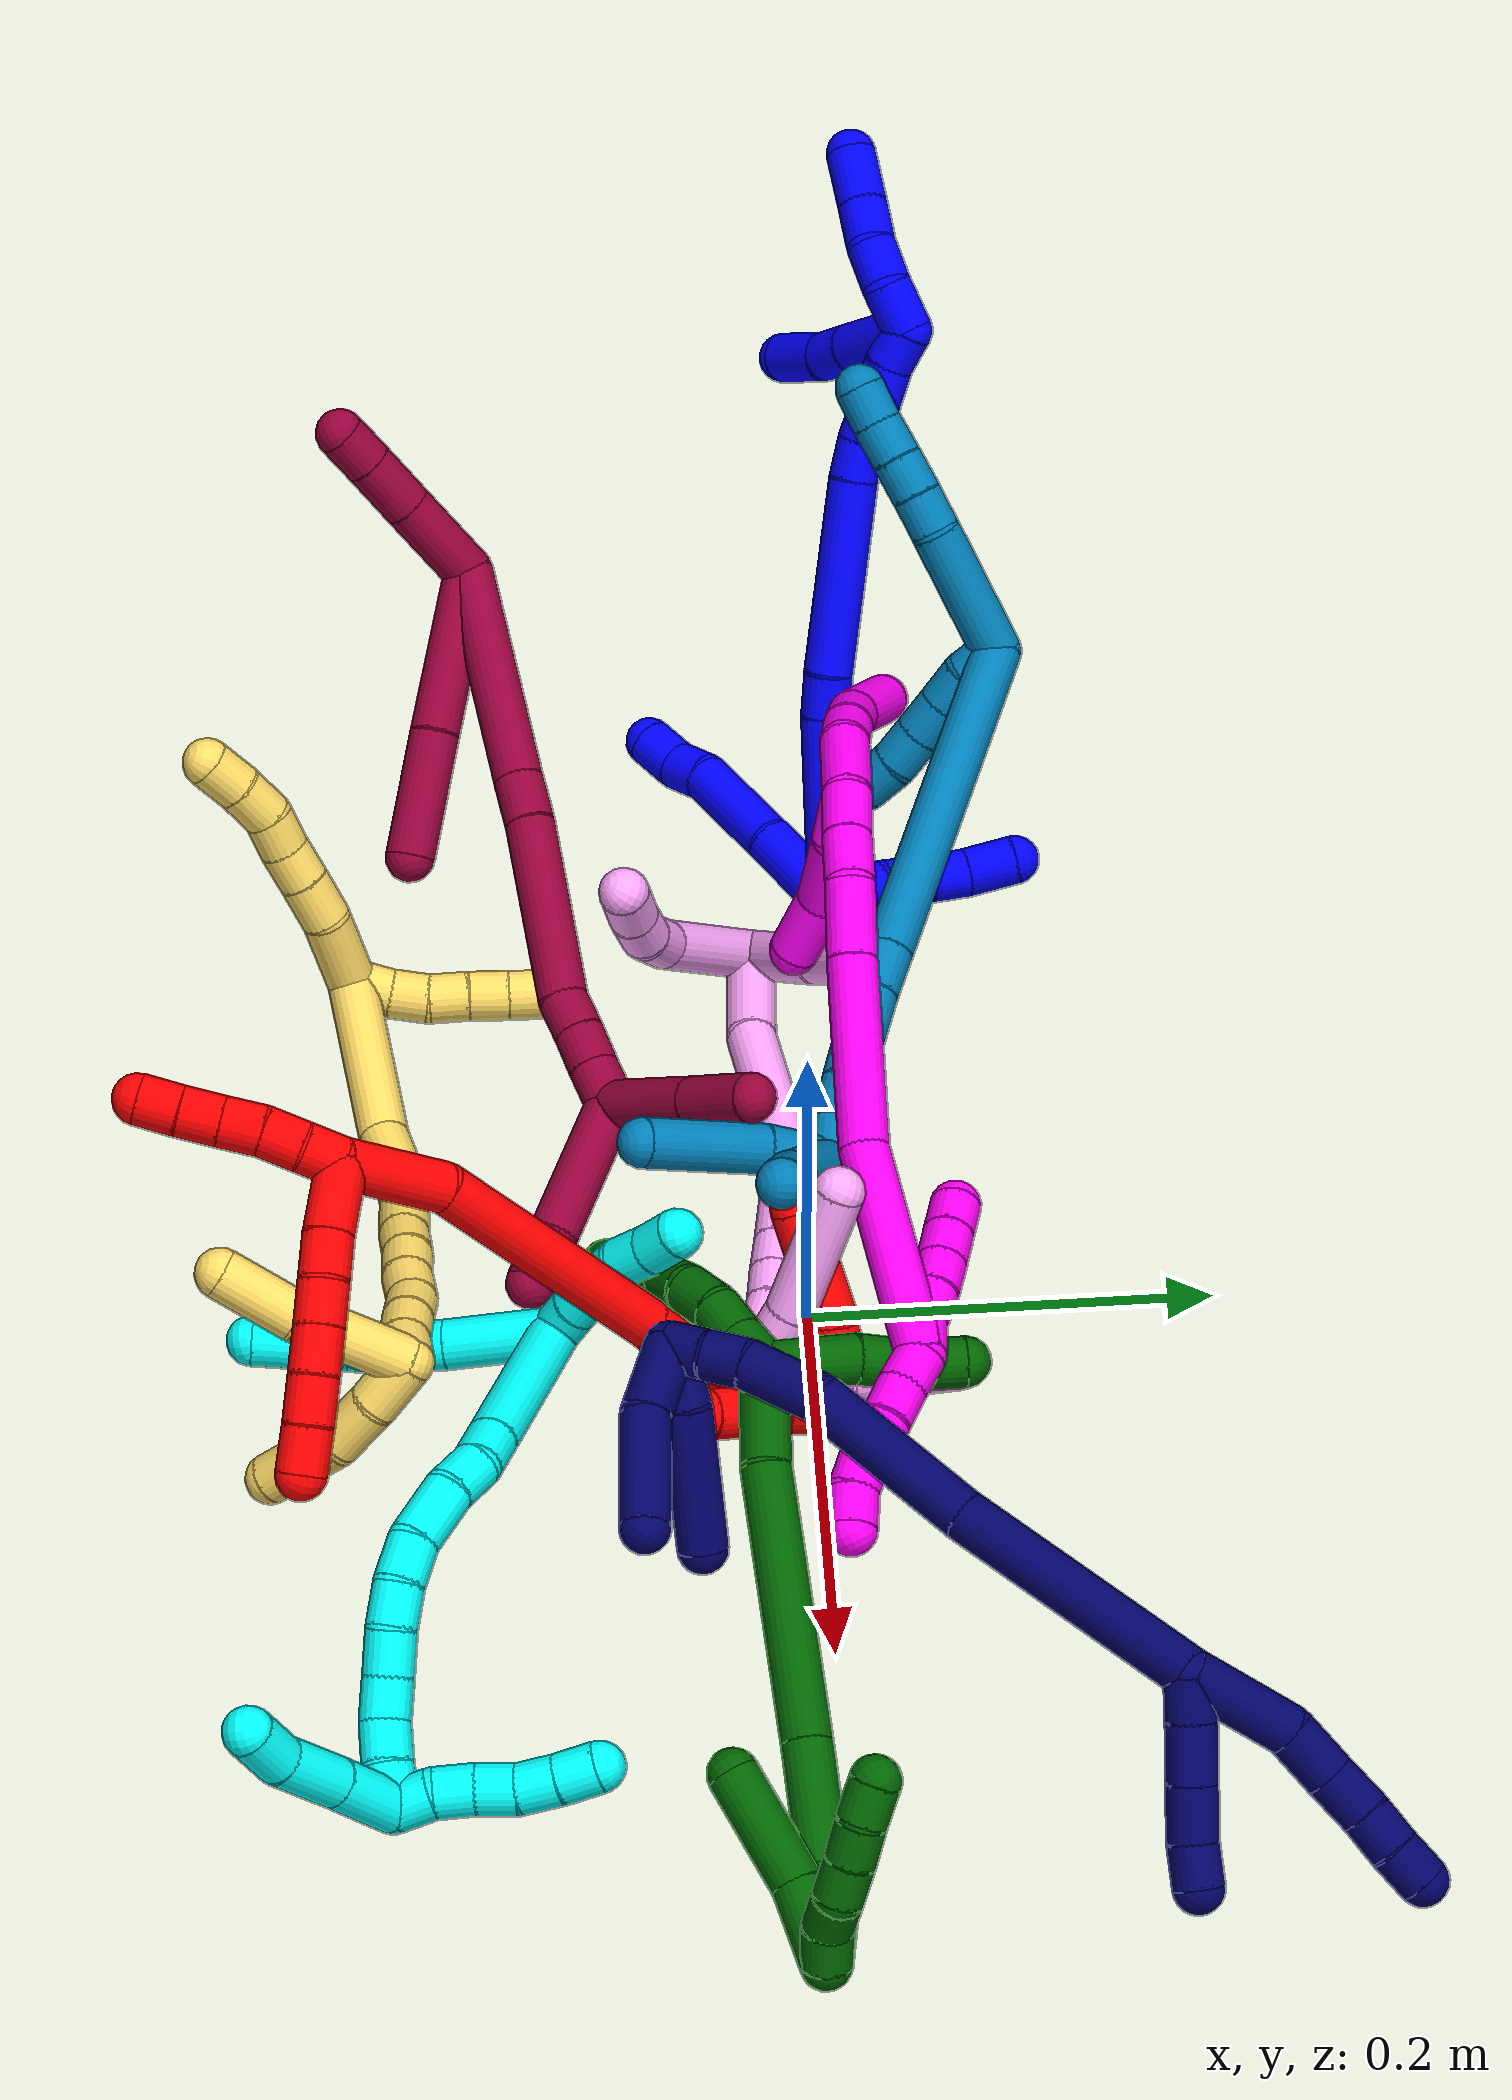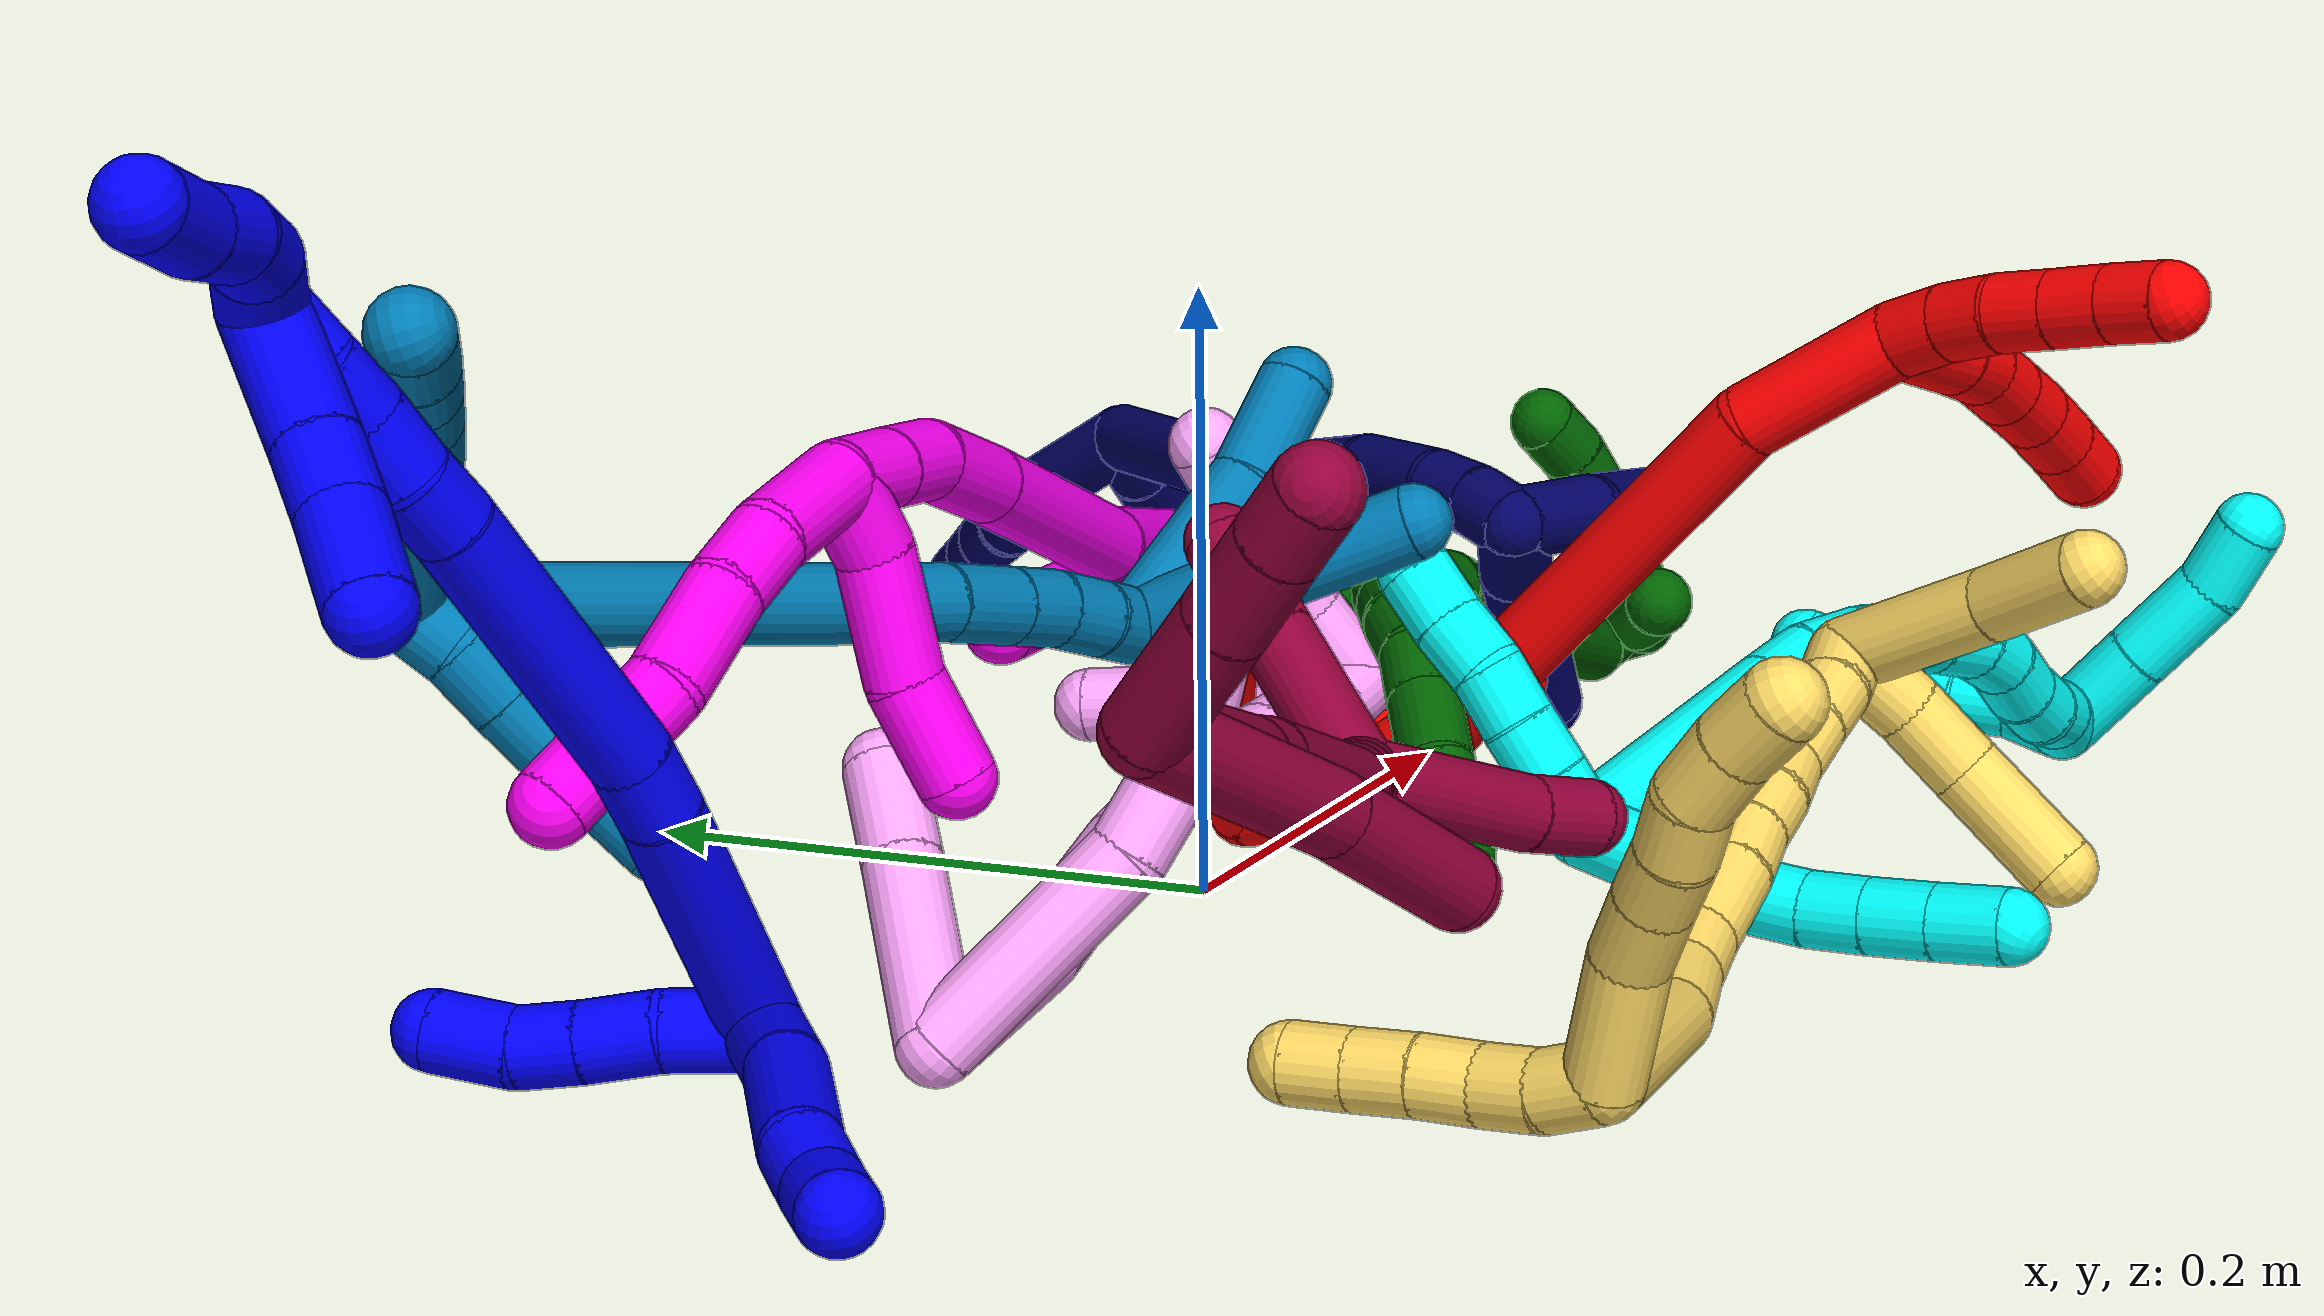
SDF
<sdf version="1.7">
 <world name="default">
  <plugin name="TubeGeneratorPlugin" filename="libtube_generator_plugin.so"/>
  <model name="photoneo_s_sensor">
   <static>1</static>
   <pose>0 0 2 1.57079 1.57079 3.14159</pose>
   <link name="link">
    <inertial><mass>0.1</mass></inertial>
    <sensor name="sensor" type="depth">
     <update_rate>30</update_rate>
     <camera>
      <horizontal_fov>1.22</horizontal_fov>
      <image><width>1920</width><height>1200</height><format>B8G8R8</format></image>
      <clip><near>0.1</near><far>4</far></clip>
      <depth_camera><output>points</output></depth_camera>
     </camera>
     <plugin name="camera_plugin" filename="libgazebo_ros_depth_camera.so">
      <baseline>0.2</baseline>
      <alwaysOn>1</alwaysOn>
      <updateRate>0.0</updateRate>
      <cameraName>camera_ir</cameraName>
      <imageTopicName>/camera/color/image_raw</imageTopicName>
      <cameraInfoTopicName>/camera/color/camera_info</cameraInfoTopicName>
      <depthImageTopicName>/camera/depth/image_raw</depthImageTopicName>
      <depthImageCameraInfoTopicName>/camera/depth/camera_info</depthImageCameraInfoTopicName>
      <pointCloudTopicName>/camera/depth/points</pointCloudTopicName>
      <frameName>fr_optical</frameName>
      <pointCloudCutoff>0.1</pointCloudCutoff>
      <pointCloudCutoffMax>2.0</pointCloudCutoffMax>
      <distortionK1>0</distortionK1>
      <distortionK2>0</distortionK2>
      <distortionK3>0</distortionK3>
      <distortionT1>0</distortionT1>
      <distortionT2>0</distortionT2>
      <CxPrime>0</CxPrime>
      <Cx>0</Cx>
      <Cy>0</Cy>
      <focalLength>0</focalLength>
      <hackBaseline>0</hackBaseline>
     </plugin>
    </sensor>
   </link>
  </model>
  <gravity>0 0 -9.8</gravity>
  <magnetic_field>6e-06 2.3e-05 -4.2e-05</magnetic_field>
  <atmosphere type="adiabatic"/>
  <physics name="default_physics" default="0" type="ode">
   <max_step_size>0.003</max_step_size>
   <real_time_factor>1</real_time_factor>
   <real_time_update_rate>1000</real_time_update_rate>
   <max_contacts>10000</max_contacts>
   <ode>
    <solver>
     <type>quick</type>
     <iters>100</iters>
     <sor>1.3</sor>
     <use_dynamic_moi_rescaling>0</use_dynamic_moi_rescaling>
    </solver>
    <constraints>
     <contact_max_correcting_vel>0</contact_max_correcting_vel>
     <contact_surface_layer>0.001</contact_surface_layer>
     <cfm>0</cfm>
     <erp>0.2</erp>
    </constraints>
   </ode>
  </physics>
  <scene><ambient>0.4 0.4 0.4 1</ambient><background>0.7 0.7 0.7 1</background><shadows>0</shadows></scene>
  <audio><device>default</device></audio>
  <spherical_coordinates>
   <surface_model>EARTH_WGS84</surface_model>
   <latitude_deg>0</latitude_deg>
   <longitude_deg>0</longitude_deg>
   <elevation>0</elevation>
   <heading_deg>0</heading_deg>
  </spherical_coordinates>
  <model name="bin">
   <static>1</static>
   <link name="bottom">
    <collision name="collision-bottom">
     <pose>0 0 -0.01 0 -0 0</pose>
     <geometry><box><size>0.8 0.6 0.02</size></box></geometry>
     <surface>
      <friction><ode><mu>100</mu><mu2>100</mu2></ode></friction>
      <contact><collide_bitmask>65535</collide_bitmask></contact>
     </surface>
    </collision>
   </link>
   <link name="west_wall">
    <collision name="collision-west_wall">
     <pose>-0.41 0 0.1 0 -0 0</pose>
     <geometry><box><size>0.02 0.6 0.2</size></box></geometry>
     <surface>
      <friction><ode><mu>100</mu><mu2>100</mu2></ode></friction>
      <contact><collide_bitmask>65535</collide_bitmask></contact>
     </surface>
    </collision>
   </link>
   <link name="east_wall">
    <collision name="collision-east_wall">
     <pose>0.41 0 0.1 0 -0 0</pose>
     <geometry><box><size>0.02 0.6 0.2</size></box></geometry>
     <surface>
      <friction><ode><mu>100</mu><mu2>100</mu2></ode></friction>
      <contact><collide_bitmask>65535</collide_bitmask></contact>
     </surface>
    </collision>
   </link>
   <link name="south_wall">
    <collision name="collision-south_wall">
     <pose>0 -0.31 0.1 0 -0 0</pose>
     <geometry><box><size>0.8 0.02 0.2</size></box></geometry>
     <surface>
      <friction><ode><mu>100</mu><mu2>100</mu2></ode></friction>
      <contact><collide_bitmask>65535</collide_bitmask></contact>
     </surface>
    </collision>
   </link>
   <link name="north_wall">
    <collision name="collision-north_wall">
     <pose>0 0.31 0.1 0 -0 0</pose>
     <geometry><box><size>0.8 0.02 0.2</size></box></geometry>
     <surface>
      <friction><ode><mu>100</mu><mu2>100</mu2></ode></friction>
      <contact><collide_bitmask>65535</collide_bitmask></contact>
     </surface>
    </collision>
   </link>
  </model>
  <model name="1">
   <static>0</static>
   <link name="1">
    <collision name="collision-cylinder-e_1_2_8">
     <pose>-0.000408 -0.021366 -0.014315 2.16109 -0.015846 -0.029688</pose>
     <geometry><cylinder><radius>0.0125</radius><length>0.051443</length></cylinder></geometry>
     <surface>
      <friction><ode><mu>1.16</mu><mu2>1.16</mu2><slip1>0</slip1><slip2>0</slip2></ode></friction>
      <contact><ode><kp>1e+06</kp><kd>1</kd><max_vel>0</max_vel><min_depth>0.001</min_depth></ode></contact>
     </surface>
    </collision>
    <visual name="visual-cylinder-e_1_2_8">
     <pose>-0.000408 -0.021366 -0.014315 2.16109 -0.015846 -0.029688</pose>
     <geometry><cylinder><radius>0.0125</radius><length>0.051443</length></cylinder></geometry>
     <material><ambient>0 0 1 1</ambient></material>
    </visual>
    <collision name="collision-cylinder-e_2_8_9">
     <pose>0.001444 -0.067713 -0.041637 2.05086 0.08005 0.131813</pose>
     <geometry><cylinder><radius>0.0125</radius><length>0.05651</length></cylinder></geometry>
     <surface>
      <friction><ode><mu>1.16</mu><mu2>1.16</mu2><slip1>0</slip1><slip2>0</slip2></ode></friction>
      <contact><ode><kp>1e+06</kp><kd>1</kd><max_vel>0</max_vel><min_depth>0.001</min_depth></ode></contact>
     </surface>
    </collision>
    <visual name="visual-cylinder-e_2_8_9">
     <pose>0.001444 -0.067713 -0.041637 2.05086 0.08005 0.131813</pose>
     <geometry><cylinder><radius>0.0125</radius><length>0.05651</length></cylinder></geometry>
     <material><ambient>0 0 1 1</ambient></material>
    </visual>
    <collision name="collision-cylinder-e_3_9_10">
     <pose>0.003052 -0.102641 -0.056897 1.79348 -0.063858 -0.079919</pose>
     <geometry><cylinder><radius>0.0125</radius><length>0.020439</length></cylinder></geometry>
     <surface>
      <friction><ode><mu>1.16</mu><mu2>1.16</mu2><slip1>0</slip1><slip2>0</slip2></ode></friction>
      <contact><ode><kp>1e+06</kp><kd>1</kd><max_vel>0</max_vel><min_depth>0.001</min_depth></ode></contact>
     </surface>
    </collision>
    <visual name="visual-cylinder-e_3_9_10">
     <pose>0.003052 -0.102641 -0.056897 1.79348 -0.063858 -0.079919</pose>
     <geometry><cylinder><radius>0.0125</radius><length>0.020439</length></cylinder></geometry>
     <material><ambient>0 0 1 1</ambient></material>
    </visual>
    <collision name="collision-cylinder-e_4_10_6">
     <pose>0.001834 -0.121907 -0.064587 2.099 -0.052356 -0.091125</pose>
     <geometry><cylinder><radius>0.0125</radius><length>0.021608</length></cylinder></geometry>
     <surface>
      <friction><ode><mu>1.16</mu><mu2>1.16</mu2><slip1>0</slip1><slip2>0</slip2></ode></friction>
      <contact><ode><kp>1e+06</kp><kd>1</kd><max_vel>0</max_vel><min_depth>0.001</min_depth></ode></contact>
     </surface>
    </collision>
    <visual name="visual-cylinder-e_4_10_6">
     <pose>0.001834 -0.121907 -0.064587 2.099 -0.052356 -0.091125</pose>
     <geometry><cylinder><radius>0.0125</radius><length>0.021608</length></cylinder></geometry>
     <material><ambient>0 0 1 1</ambient></material>
    </visual>
    <collision name="collision-cylinder-e_1_2_11">
     <pose>0.013678 0.005121 -0.001708 -1.89277 1.19489 -1.51342</pose>
     <geometry><cylinder><radius>0.0125</radius><length>0.02941</length></cylinder></geometry>
     <surface>
      <friction><ode><mu>1.16</mu><mu2>1.16</mu2><slip1>0</slip1><slip2>0</slip2></ode></friction>
      <contact><ode><kp>1e+06</kp><kd>1</kd><max_vel>0</max_vel><min_depth>0.001</min_depth></ode></contact>
     </surface>
    </collision>
    <visual name="visual-cylinder-e_1_2_11">
     <pose>0.013678 0.005121 -0.001708 -1.89277 1.19489 -1.51342</pose>
     <geometry><cylinder><radius>0.0125</radius><length>0.02941</length></cylinder></geometry>
     <material><ambient>0 0 1 1</ambient></material>
    </visual>
    <collision name="collision-cylinder-e_2_11_12">
     <pose>0.038598 0.014482 -0.002288 -1.31073 1.19874 -0.967184</pose>
     <geometry><cylinder><radius>0.0125</radius><length>0.024135</length></cylinder></geometry>
     <surface>
      <friction><ode><mu>1.16</mu><mu2>1.16</mu2><slip1>0</slip1><slip2>0</slip2></ode></friction>
      <contact><ode><kp>1e+06</kp><kd>1</kd><max_vel>0</max_vel><min_depth>0.001</min_depth></ode></contact>
     </surface>
    </collision>
    <visual name="visual-cylinder-e_2_11_12">
     <pose>0.038598 0.014482 -0.002288 -1.31073 1.19874 -0.967184</pose>
     <geometry><cylinder><radius>0.0125</radius><length>0.024135</length></cylinder></geometry>
     <material><ambient>0 0 1 1</ambient></material>
    </visual>
    <collision name="collision-cylinder-e_3_12_13">
     <pose>0.059199 0.022635 -0.000687 -1.45048 1.17213 -1.06375</pose>
     <geometry><cylinder><radius>0.0125</radius><length>0.020309</length></cylinder></geometry>
     <surface>
      <friction><ode><mu>1.16</mu><mu2>1.16</mu2><slip1>0</slip1><slip2>0</slip2></ode></friction>
      <contact><ode><kp>1e+06</kp><kd>1</kd><max_vel>0</max_vel><min_depth>0.001</min_depth></ode></contact>
     </surface>
    </collision>
    <visual name="visual-cylinder-e_3_12_13">
     <pose>0.059199 0.022635 -0.000687 -1.45048 1.17213 -1.06375</pose>
     <geometry><cylinder><radius>0.0125</radius><length>0.020309</length></cylinder></geometry>
     <material><ambient>0 0 1 1</ambient></material>
    </visual>
    <collision name="collision-cylinder-e_4_13_5">
     <pose>0.079129 0.034081 -0.001761 -1.77339 0.941922 -1.11633</pose>
     <geometry><cylinder><radius>0.0125</radius><length>0.026146</length></cylinder></geometry>
     <surface>
      <friction><ode><mu>1.16</mu><mu2>1.16</mu2><slip1>0</slip1><slip2>0</slip2></ode></friction>
      <contact><ode><kp>1e+06</kp><kd>1</kd><max_vel>0</max_vel><min_depth>0.001</min_depth></ode></contact>
     </surface>
    </collision>
    <visual name="visual-cylinder-e_4_13_5">
     <pose>0.079129 0.034081 -0.001761 -1.77339 0.941922 -1.11633</pose>
     <geometry><cylinder><radius>0.0125</radius><length>0.026146</length></cylinder></geometry>
     <material><ambient>0 0 1 1</ambient></material>
    </visual>
    <collision name="collision-cylinder-e_1_2_14">
     <pose>0.003773 0.001955 -0.048828 -3.10157 0.077057 -2.18373</pose>
     <geometry><cylinder><radius>0.0125</radius><length>0.098025</length></cylinder></geometry>
     <surface>
      <friction><ode><mu>1.16</mu><mu2>1.16</mu2><slip1>0</slip1><slip2>0</slip2></ode></friction>
      <contact><ode><kp>1e+06</kp><kd>1</kd><max_vel>0</max_vel><min_depth>0.001</min_depth></ode></contact>
     </surface>
    </collision>
    <visual name="visual-cylinder-e_1_2_14">
     <pose>0.003773 0.001955 -0.048828 -3.10157 0.077057 -2.18373</pose>
     <geometry><cylinder><radius>0.0125</radius><length>0.098025</length></cylinder></geometry>
     <material><ambient>0 0 1 1</ambient></material>
    </visual>
    <collision name="collision-cylinder-e_2_14_15">
     <pose>0.008989 0.00551 -0.108491 -2.99503 0.130995 -1.45839</pose>
     <geometry><cylinder><radius>0.0125</radius><length>0.022096</length></cylinder></geometry>
     <surface>
      <friction><ode><mu>1.16</mu><mu2>1.16</mu2><slip1>0</slip1><slip2>0</slip2></ode></friction>
      <contact><ode><kp>1e+06</kp><kd>1</kd><max_vel>0</max_vel><min_depth>0.001</min_depth></ode></contact>
     </surface>
    </collision>
    <visual name="visual-cylinder-e_2_14_15">
     <pose>0.008989 0.00551 -0.108491 -2.99503 0.130995 -1.45839</pose>
     <geometry><cylinder><radius>0.0125</radius><length>0.022096</length></cylinder></geometry>
     <material><ambient>0 0 1 1</ambient></material>
    </visual>
    <collision name="collision-cylinder-e_3_15_16">
     <pose>0.022351 0.011961 -0.16712 -3.04043 0.243203 -2.35614</pose>
     <geometry><cylinder><radius>0.0125</radius><length>0.098989</length></cylinder></geometry>
     <surface>
      <friction><ode><mu>1.16</mu><mu2>1.16</mu2><slip1>0</slip1><slip2>0</slip2></ode></friction>
      <contact><ode><kp>1e+06</kp><kd>1</kd><max_vel>0</max_vel><min_depth>0.001</min_depth></ode></contact>
     </surface>
    </collision>
    <visual name="visual-cylinder-e_3_15_16">
     <pose>0.022351 0.011961 -0.16712 -3.04043 0.243203 -2.35614</pose>
     <geometry><cylinder><radius>0.0125</radius><length>0.098989</length></cylinder></geometry>
     <material><ambient>0 0 1 1</ambient></material>
    </visual>
    <collision name="collision-cylinder-e_4_16_17">
     <pose>0.037473 0.018322 -0.224373 -2.98342 0.322648 -2.23522</pose>
     <geometry><cylinder><radius>0.0125</radius><length>0.020204</length></cylinder></geometry>
     <surface>
      <friction><ode><mu>1.16</mu><mu2>1.16</mu2><slip1>0</slip1><slip2>0</slip2></ode></friction>
      <contact><ode><kp>1e+06</kp><kd>1</kd><max_vel>0</max_vel><min_depth>0.001</min_depth></ode></contact>
     </surface>
    </collision>
    <visual name="visual-cylinder-e_4_16_17">
     <pose>0.037473 0.018322 -0.224373 -2.98342 0.322648 -2.23522</pose>
     <geometry><cylinder><radius>0.0125</radius><length>0.020204</length></cylinder></geometry>
     <material><ambient>0 0 1 1</ambient></material>
    </visual>
    <collision name="collision-cylinder-e_5_17_18">
     <pose>0.043619 0.023396 -0.243085 -2.77369 0.288506 -1.32578</pose>
     <geometry><cylinder><radius>0.0125</radius><length>0.020683</length></cylinder></geometry>
     <surface>
      <friction><ode><mu>1.16</mu><mu2>1.16</mu2><slip1>0</slip1><slip2>0</slip2></ode></friction>
      <contact><ode><kp>1e+06</kp><kd>1</kd><max_vel>0</max_vel><min_depth>0.001</min_depth></ode></contact>
     </surface>
    </collision>
    <visual name="visual-cylinder-e_5_17_18">
     <pose>0.043619 0.023396 -0.243085 -2.77369 0.288506 -1.32578</pose>
     <geometry><cylinder><radius>0.0125</radius><length>0.020683</length></cylinder></geometry>
     <material><ambient>0 0 1 1</ambient></material>
    </visual>
    <collision name="collision-cylinder-e_6_18_19">
     <pose>0.049965 0.029466 -0.261401 -2.87209 0.347291 -1.82561</pose>
     <geometry><cylinder><radius>0.0125</radius><length>0.020002</length></cylinder></geometry>
     <surface>
      <friction><ode><mu>1.16</mu><mu2>1.16</mu2><slip1>0</slip1><slip2>0</slip2></ode></friction>
      <contact><ode><kp>1e+06</kp><kd>1</kd><max_vel>0</max_vel><min_depth>0.001</min_depth></ode></contact>
     </surface>
    </collision>
    <visual name="visual-cylinder-e_6_18_19">
     <pose>0.049965 0.029466 -0.261401 -2.87209 0.347291 -1.82561</pose>
     <geometry><cylinder><radius>0.0125</radius><length>0.020002</length></cylinder></geometry>
     <material><ambient>0 0 1 1</ambient></material>
    </visual>
    <collision name="collision-cylinder-e_7_19_1">
     <pose>0.057018 0.036491 -0.278605 -2.63465 0.373474 -1.26033</pose>
     <geometry><cylinder><radius>0.0125</radius><length>0.02</length></cylinder></geometry>
     <surface>
      <friction><ode><mu>1.16</mu><mu2>1.16</mu2><slip1>0</slip1><slip2>0</slip2></ode></friction>
      <contact><ode><kp>1e+06</kp><kd>1</kd><max_vel>0</max_vel><min_depth>0.001</min_depth></ode></contact>
     </surface>
    </collision>
    <visual name="visual-cylinder-e_7_19_1">
     <pose>0.057018 0.036491 -0.278605 -2.63465 0.373474 -1.26033</pose>
     <geometry><cylinder><radius>0.0125</radius><length>0.02</length></cylinder></geometry>
     <material><ambient>0 0 1 1</ambient></material>
    </visual>
    <collision name="collision-cylinder-e_1_1_20">
     <pose>0.059117 0.036757 -0.298617 2.79755 -0.122231 -0.677279</pose>
     <geometry><cylinder><radius>0.0125</radius><length>0.025411</length></cylinder></geometry>
     <surface>
      <friction><ode><mu>1.16</mu><mu2>1.16</mu2><slip1>0</slip1><slip2>0</slip2></ode></friction>
      <contact><ode><kp>1e+06</kp><kd>1</kd><max_vel>0</max_vel><min_depth>0.001</min_depth></ode></contact>
     </surface>
    </collision>
    <visual name="visual-cylinder-e_1_1_20">
     <pose>0.059117 0.036757 -0.298617 2.79755 -0.122231 -0.677279</pose>
     <geometry><cylinder><radius>0.0125</radius><length>0.025411</length></cylinder></geometry>
     <material><ambient>0 0 1 1</ambient></material>
    </visual>
    <collision name="collision-cylinder-e_2_20_21">
     <pose>0.059169 0.026825 -0.319936 2.60035 0.144275 0.509629</pose>
     <geometry><cylinder><radius>0.0125</radius><length>0.022277</length></cylinder></geometry>
     <surface>
      <friction><ode><mu>1.16</mu><mu2>1.16</mu2><slip1>0</slip1><slip2>0</slip2></ode></friction>
      <contact><ode><kp>1e+06</kp><kd>1</kd><max_vel>0</max_vel><min_depth>0.001</min_depth></ode></contact>
     </surface>
    </collision>
    <visual name="visual-cylinder-e_2_20_21">
     <pose>0.059169 0.026825 -0.319936 2.60035 0.144275 0.509629</pose>
     <geometry><cylinder><radius>0.0125</radius><length>0.022277</length></cylinder></geometry>
     <material><ambient>0 0 1 1</ambient></material>
    </visual>
    <collision name="collision-cylinder-e_3_21_22">
     <pose>0.065178 0.014717 -0.337874 2.4935 0.392361 1.06856</pose>
     <geometry><cylinder><radius>0.0125</radius><length>0.023049</length></cylinder></geometry>
     <surface>
      <friction><ode><mu>1.16</mu><mu2>1.16</mu2><slip1>0</slip1><slip2>0</slip2></ode></friction>
      <contact><ode><kp>1e+06</kp><kd>1</kd><max_vel>0</max_vel><min_depth>0.001</min_depth></ode></contact>
     </surface>
    </collision>
    <visual name="visual-cylinder-e_3_21_22">
     <pose>0.065178 0.014717 -0.337874 2.4935 0.392361 1.06856</pose>
     <geometry><cylinder><radius>0.0125</radius><length>0.023049</length></cylinder></geometry>
     <material><ambient>0 0 1 1</ambient></material>
    </visual>
    <collision name="collision-cylinder-e_4_22_4">
     <pose>0.07382 0.001261 -0.358476 2.61586 0.293735 1.0053</pose>
     <geometry><cylinder><radius>0.0125</radius><length>0.029262</length></cylinder></geometry>
     <surface>
      <friction><ode><mu>1.16</mu><mu2>1.16</mu2><slip1>0</slip1><slip2>0</slip2></ode></friction>
      <contact><ode><kp>1e+06</kp><kd>1</kd><max_vel>0</max_vel><min_depth>0.001</min_depth></ode></contact>
     </surface>
    </collision>
    <visual name="visual-cylinder-e_4_22_4">
     <pose>0.07382 0.001261 -0.358476 2.61586 0.293735 1.0053</pose>
     <geometry><cylinder><radius>0.0125</radius><length>0.029262</length></cylinder></geometry>
     <material><ambient>0 0 1 1</ambient></material>
    </visual>
    <collision name="collision-cylinder-e_1_1_23">
     <pose>0.060071 0.019243 -0.280951 1.31065 -0.026414 -0.020303</pose>
     <geometry><cylinder><radius>0.0125</radius><length>0.045068</length></cylinder></geometry>
     <surface>
      <friction><ode><mu>1.16</mu><mu2>1.16</mu2><slip1>0</slip1><slip2>0</slip2></ode></friction>
      <contact><ode><kp>1e+06</kp><kd>1</kd><max_vel>0</max_vel><min_depth>0.001</min_depth></ode></contact>
     </surface>
    </collision>
    <visual name="visual-cylinder-e_1_1_23">
     <pose>0.060071 0.019243 -0.280951 1.31065 -0.026414 -0.020303</pose>
     <geometry><cylinder><radius>0.0125</radius><length>0.045068</length></cylinder></geometry>
     <material><ambient>0 0 1 1</ambient></material>
    </visual>
    <collision name="collision-cylinder-e_2_23_24">
     <pose>0.059483 -0.013056 -0.27216 1.29357 0.000689 0.00052</pose>
     <geometry><cylinder><radius>0.0125</radius><length>0.021897</length></cylinder></geometry>
     <surface>
      <friction><ode><mu>1.16</mu><mu2>1.16</mu2><slip1>0</slip1><slip2>0</slip2></ode></friction>
      <contact><ode><kp>1e+06</kp><kd>1</kd><max_vel>0</max_vel><min_depth>0.001</min_depth></ode></contact>
     </surface>
    </collision>
    <visual name="visual-cylinder-e_2_23_24">
     <pose>0.059483 -0.013056 -0.27216 1.29357 0.000689 0.00052</pose>
     <geometry><cylinder><radius>0.0125</radius><length>0.021897</length></cylinder></geometry>
     <material><ambient>0 0 1 1</ambient></material>
    </visual>
    <collision name="collision-cylinder-e_3_24_3">
     <pose>0.059982 -0.04002 -0.267573 1.47431 0.029754 0.027013</pose>
     <geometry><cylinder><radius>0.0125</radius><length>0.033035</length></cylinder></geometry>
     <surface>
      <friction><ode><mu>1.16</mu><mu2>1.16</mu2><slip1>0</slip1><slip2>0</slip2></ode></friction>
      <contact><ode><kp>1e+06</kp><kd>1</kd><max_vel>0</max_vel><min_depth>0.001</min_depth></ode></contact>
     </surface>
    </collision>
    <visual name="visual-cylinder-e_3_24_3">
     <pose>0.059982 -0.04002 -0.267573 1.47431 0.029754 0.027013</pose>
     <geometry><cylinder><radius>0.0125</radius><length>0.033035</length></cylinder></geometry>
     <material><ambient>0 0 1 1</ambient></material>
    </visual>
    <collision name="collision-sphere-3">
     <pose>0.060474 -0.056453 -0.265982 0 -0 0</pose>
     <geometry><sphere><radius>0.0125</radius></sphere></geometry>
     <surface>
      <friction><ode><mu>1.16</mu><mu2>1.16</mu2><slip1>0</slip1><slip2>0</slip2></ode></friction>
      <contact><ode><kp>1e+06</kp><kd>1</kd><max_vel>0</max_vel><min_depth>0.001</min_depth></ode></contact>
     </surface>
    </collision>
    <visual name="visual-sphere-3">
     <pose>0.060474 -0.056453 -0.265982 0 -0 0</pose>
     <geometry><sphere><radius>0.0125</radius></sphere></geometry>
     <material><ambient>0 0 1 1</ambient></material>
    </visual>
    <collision name="collision-sphere-24">
     <pose>0.059491 -0.023586 -0.269163 0 -0 0</pose>
     <geometry><sphere><radius>0.0125</radius></sphere></geometry>
     <surface>
      <friction><ode><mu>1.16</mu><mu2>1.16</mu2><slip1>0</slip1><slip2>0</slip2></ode></friction>
      <contact><ode><kp>1e+06</kp><kd>1</kd><max_vel>0</max_vel><min_depth>0.001</min_depth></ode></contact>
     </surface>
    </collision>
    <visual name="visual-sphere-24">
     <pose>0.059491 -0.023586 -0.269163 0 -0 0</pose>
     <geometry><sphere><radius>0.0125</radius></sphere></geometry>
     <material><ambient>0 0 1 1</ambient></material>
    </visual>
    <collision name="collision-sphere-23">
     <pose>0.059476 -0.002525 -0.275156 0 -0 0</pose>
     <geometry><sphere><radius>0.0125</radius></sphere></geometry>
     <surface>
      <friction><ode><mu>1.16</mu><mu2>1.16</mu2><slip1>0</slip1><slip2>0</slip2></ode></friction>
      <contact><ode><kp>1e+06</kp><kd>1</kd><max_vel>0</max_vel><min_depth>0.001</min_depth></ode></contact>
     </surface>
    </collision>
    <visual name="visual-sphere-23">
     <pose>0.059476 -0.002525 -0.275156 0 -0 0</pose>
     <geometry><sphere><radius>0.0125</radius></sphere></geometry>
     <material><ambient>0 0 1 1</ambient></material>
    </visual>
    <collision name="collision-sphere-4">
     <pose>0.078056 -0.005767 -0.370589 0 -0 0</pose>
     <geometry><sphere><radius>0.0125</radius></sphere></geometry>
     <surface>
      <friction><ode><mu>1.16</mu><mu2>1.16</mu2><slip1>0</slip1><slip2>0</slip2></ode></friction>
      <contact><ode><kp>1e+06</kp><kd>1</kd><max_vel>0</max_vel><min_depth>0.001</min_depth></ode></contact>
     </surface>
    </collision>
    <visual name="visual-sphere-4">
     <pose>0.078056 -0.005767 -0.370589 0 -0 0</pose>
     <geometry><sphere><radius>0.0125</radius></sphere></geometry>
     <material><ambient>0 0 1 1</ambient></material>
    </visual>
    <collision name="collision-sphere-22">
     <pose>0.069584 0.008289 -0.346363 0 -0 0</pose>
     <geometry><sphere><radius>0.0125</radius></sphere></geometry>
     <surface>
      <friction><ode><mu>1.16</mu><mu2>1.16</mu2><slip1>0</slip1><slip2>0</slip2></ode></friction>
      <contact><ode><kp>1e+06</kp><kd>1</kd><max_vel>0</max_vel><min_depth>0.001</min_depth></ode></contact>
     </surface>
    </collision>
    <visual name="visual-sphere-22">
     <pose>0.069584 0.008289 -0.346363 0 -0 0</pose>
     <geometry><sphere><radius>0.0125</radius></sphere></geometry>
     <material><ambient>0 0 1 1</ambient></material>
    </visual>
    <collision name="collision-sphere-21">
     <pose>0.060771 0.021146 -0.329384 0 -0 0</pose>
     <geometry><sphere><radius>0.0125</radius></sphere></geometry>
     <surface>
      <friction><ode><mu>1.16</mu><mu2>1.16</mu2><slip1>0</slip1><slip2>0</slip2></ode></friction>
      <contact><ode><kp>1e+06</kp><kd>1</kd><max_vel>0</max_vel><min_depth>0.001</min_depth></ode></contact>
     </surface>
    </collision>
    <visual name="visual-sphere-21">
     <pose>0.060771 0.021146 -0.329384 0 -0 0</pose>
     <geometry><sphere><radius>0.0125</radius></sphere></geometry>
     <material><ambient>0 0 1 1</ambient></material>
    </visual>
    <collision name="collision-sphere-20">
     <pose>0.057568 0.032504 -0.310489 0 -0 0</pose>
     <geometry><sphere><radius>0.0125</radius></sphere></geometry>
     <surface>
      <friction><ode><mu>1.16</mu><mu2>1.16</mu2><slip1>0</slip1><slip2>0</slip2></ode></friction>
      <contact><ode><kp>1e+06</kp><kd>1</kd><max_vel>0</max_vel><min_depth>0.001</min_depth></ode></contact>
     </surface>
    </collision>
    <visual name="visual-sphere-20">
     <pose>0.057568 0.032504 -0.310489 0 -0 0</pose>
     <geometry><sphere><radius>0.0125</radius></sphere></geometry>
     <material><ambient>0 0 1 1</ambient></material>
    </visual>
    <collision name="collision-sphere-11">
     <pose>0.027356 0.010242 -0.003417 0 -0 0</pose>
     <geometry><sphere><radius>0.0125</radius></sphere></geometry>
     <surface>
      <friction><ode><mu>1.16</mu><mu2>1.16</mu2><slip1>0</slip1><slip2>0</slip2></ode></friction>
      <contact><ode><kp>1e+06</kp><kd>1</kd><max_vel>0</max_vel><min_depth>0.001</min_depth></ode></contact>
     </surface>
    </collision>
    <visual name="visual-sphere-11">
     <pose>0.027356 0.010242 -0.003417 0 -0 0</pose>
     <geometry><sphere><radius>0.0125</radius></sphere></geometry>
     <material><ambient>0 0 1 1</ambient></material>
    </visual>
    <collision name="collision-sphere-6">
     <pose>0.001269 -0.131225 -0.070025 0 -0 0</pose>
     <geometry><sphere><radius>0.0125</radius></sphere></geometry>
     <surface>
      <friction><ode><mu>1.16</mu><mu2>1.16</mu2><slip1>0</slip1><slip2>0</slip2></ode></friction>
      <contact><ode><kp>1e+06</kp><kd>1</kd><max_vel>0</max_vel><min_depth>0.001</min_depth></ode></contact>
     </surface>
    </collision>
    <visual name="visual-sphere-6">
     <pose>0.001269 -0.131225 -0.070025 0 -0 0</pose>
     <geometry><sphere><radius>0.0125</radius></sphere></geometry>
     <material><ambient>0 0 1 1</ambient></material>
    </visual>
    <collision name="collision-sphere-10">
     <pose>0.002399 -0.112588 -0.059149 0 -0 0</pose>
     <geometry><sphere><radius>0.0125</radius></sphere></geometry>
     <surface>
      <friction><ode><mu>1.16</mu><mu2>1.16</mu2><slip1>0</slip1><slip2>0</slip2></ode></friction>
      <contact><ode><kp>1e+06</kp><kd>1</kd><max_vel>0</max_vel><min_depth>0.001</min_depth></ode></contact>
     </surface>
    </collision>
    <visual name="visual-sphere-10">
     <pose>0.002399 -0.112588 -0.059149 0 -0 0</pose>
     <geometry><sphere><radius>0.0125</radius></sphere></geometry>
     <material><ambient>0 0 1 1</ambient></material>
    </visual>
    <collision name="collision-sphere-9">
     <pose>0.003704 -0.092694 -0.054645 0 -0 0</pose>
     <geometry><sphere><radius>0.0125</radius></sphere></geometry>
     <surface>
      <friction><ode><mu>1.16</mu><mu2>1.16</mu2><slip1>0</slip1><slip2>0</slip2></ode></friction>
      <contact><ode><kp>1e+06</kp><kd>1</kd><max_vel>0</max_vel><min_depth>0.001</min_depth></ode></contact>
     </surface>
    </collision>
    <visual name="visual-sphere-9">
     <pose>0.003704 -0.092694 -0.054645 0 -0 0</pose>
     <geometry><sphere><radius>0.0125</radius></sphere></geometry>
     <material><ambient>0 0 1 1</ambient></material>
    </visual>
    <collision name="collision-sphere-2">
     <geometry><sphere><radius>0.0125</radius></sphere></geometry>
     <surface>
      <friction><ode><mu>1.16</mu><mu2>1.16</mu2><slip1>0</slip1><slip2>0</slip2></ode></friction>
      <contact><ode><kp>1e+06</kp><kd>1</kd><max_vel>0</max_vel><min_depth>0.001</min_depth></ode></contact>
     </surface>
    </collision>
    <visual name="visual-sphere-2">
     <geometry><sphere><radius>0.0125</radius></sphere></geometry>
     <material><ambient>0 0 1 1</ambient></material>
    </visual>
    <collision name="collision-sphere-19">
     <pose>0.053369 0.03197 -0.270465 0 -0 0</pose>
     <geometry><sphere><radius>0.0125</radius></sphere></geometry>
     <surface>
      <friction><ode><mu>1.16</mu><mu2>1.16</mu2><slip1>0</slip1><slip2>0</slip2></ode></friction>
      <contact><ode><kp>1e+06</kp><kd>1</kd><max_vel>0</max_vel><min_depth>0.001</min_depth></ode></contact>
     </surface>
    </collision>
    <visual name="visual-sphere-19">
     <pose>0.053369 0.03197 -0.270465 0 -0 0</pose>
     <geometry><sphere><radius>0.0125</radius></sphere></geometry>
     <material><ambient>0 0 1 1</ambient></material>
    </visual>
    <collision name="collision-sphere-8">
     <pose>-0.000815 -0.042732 -0.02863 0 -0 0</pose>
     <geometry><sphere><radius>0.0125</radius></sphere></geometry>
     <surface>
      <friction><ode><mu>1.16</mu><mu2>1.16</mu2><slip1>0</slip1><slip2>0</slip2></ode></friction>
      <contact><ode><kp>1e+06</kp><kd>1</kd><max_vel>0</max_vel><min_depth>0.001</min_depth></ode></contact>
     </surface>
    </collision>
    <visual name="visual-sphere-8">
     <pose>-0.000815 -0.042732 -0.02863 0 -0 0</pose>
     <geometry><sphere><radius>0.0125</radius></sphere></geometry>
     <material><ambient>0 0 1 1</ambient></material>
    </visual>
    <collision name="collision-sphere-12">
     <pose>0.04984 0.018721 -0.00116 0 -0 0</pose>
     <geometry><sphere><radius>0.0125</radius></sphere></geometry>
     <surface>
      <friction><ode><mu>1.16</mu><mu2>1.16</mu2><slip1>0</slip1><slip2>0</slip2></ode></friction>
      <contact><ode><kp>1e+06</kp><kd>1</kd><max_vel>0</max_vel><min_depth>0.001</min_depth></ode></contact>
     </surface>
    </collision>
    <visual name="visual-sphere-12">
     <pose>0.04984 0.018721 -0.00116 0 -0 0</pose>
     <geometry><sphere><radius>0.0125</radius></sphere></geometry>
     <material><ambient>0 0 1 1</ambient></material>
    </visual>
    <collision name="collision-sphere-13">
     <pose>0.068557 0.026548 -0.000214 0 -0 0</pose>
     <geometry><sphere><radius>0.0125</radius></sphere></geometry>
     <surface>
      <friction><ode><mu>1.16</mu><mu2>1.16</mu2><slip1>0</slip1><slip2>0</slip2></ode></friction>
      <contact><ode><kp>1e+06</kp><kd>1</kd><max_vel>0</max_vel><min_depth>0.001</min_depth></ode></contact>
     </surface>
    </collision>
    <visual name="visual-sphere-13">
     <pose>0.068557 0.026548 -0.000214 0 -0 0</pose>
     <geometry><sphere><radius>0.0125</radius></sphere></geometry>
     <material><ambient>0 0 1 1</ambient></material>
    </visual>
    <collision name="collision-sphere-5">
     <pose>0.0897 0.041613 -0.003309 0 -0 0</pose>
     <geometry><sphere><radius>0.0125</radius></sphere></geometry>
     <surface>
      <friction><ode><mu>1.16</mu><mu2>1.16</mu2><slip1>0</slip1><slip2>0</slip2></ode></friction>
      <contact><ode><kp>1e+06</kp><kd>1</kd><max_vel>0</max_vel><min_depth>0.001</min_depth></ode></contact>
     </surface>
    </collision>
    <visual name="visual-sphere-5">
     <pose>0.0897 0.041613 -0.003309 0 -0 0</pose>
     <geometry><sphere><radius>0.0125</radius></sphere></geometry>
     <material><ambient>0 0 1 1</ambient></material>
    </visual>
    <collision name="collision-sphere-14">
     <pose>0.007546 0.003911 -0.097655 0 -0 0</pose>
     <geometry><sphere><radius>0.0125</radius></sphere></geometry>
     <surface>
      <friction><ode><mu>1.16</mu><mu2>1.16</mu2><slip1>0</slip1><slip2>0</slip2></ode></friction>
      <contact><ode><kp>1e+06</kp><kd>1</kd><max_vel>0</max_vel><min_depth>0.001</min_depth></ode></contact>
     </surface>
    </collision>
    <visual name="visual-sphere-14">
     <pose>0.007546 0.003911 -0.097655 0 -0 0</pose>
     <geometry><sphere><radius>0.0125</radius></sphere></geometry>
     <material><ambient>0 0 1 1</ambient></material>
    </visual>
    <collision name="collision-sphere-15">
     <pose>0.010432 0.00711 -0.119327 0 -0 0</pose>
     <geometry><sphere><radius>0.0125</radius></sphere></geometry>
     <surface>
      <friction><ode><mu>1.16</mu><mu2>1.16</mu2><slip1>0</slip1><slip2>0</slip2></ode></friction>
      <contact><ode><kp>1e+06</kp><kd>1</kd><max_vel>0</max_vel><min_depth>0.001</min_depth></ode></contact>
     </surface>
    </collision>
    <visual name="visual-sphere-15">
     <pose>0.010432 0.00711 -0.119327 0 -0 0</pose>
     <geometry><sphere><radius>0.0125</radius></sphere></geometry>
     <material><ambient>0 0 1 1</ambient></material>
    </visual>
    <collision name="collision-sphere-16">
     <pose>0.03427 0.016813 -0.214912 0 -0 0</pose>
     <geometry><sphere><radius>0.0125</radius></sphere></geometry>
     <surface>
      <friction><ode><mu>1.16</mu><mu2>1.16</mu2><slip1>0</slip1><slip2>0</slip2></ode></friction>
      <contact><ode><kp>1e+06</kp><kd>1</kd><max_vel>0</max_vel><min_depth>0.001</min_depth></ode></contact>
     </surface>
    </collision>
    <visual name="visual-sphere-16">
     <pose>0.03427 0.016813 -0.214912 0 -0 0</pose>
     <geometry><sphere><radius>0.0125</radius></sphere></geometry>
     <material><ambient>0 0 1 1</ambient></material>
    </visual>
    <collision name="collision-sphere-17">
     <pose>0.040676 0.019831 -0.233834 0 -0 0</pose>
     <geometry><sphere><radius>0.0125</radius></sphere></geometry>
     <surface>
      <friction><ode><mu>1.16</mu><mu2>1.16</mu2><slip1>0</slip1><slip2>0</slip2></ode></friction>
      <contact><ode><kp>1e+06</kp><kd>1</kd><max_vel>0</max_vel><min_depth>0.001</min_depth></ode></contact>
     </surface>
    </collision>
    <visual name="visual-sphere-17">
     <pose>0.040676 0.019831 -0.233834 0 -0 0</pose>
     <geometry><sphere><radius>0.0125</radius></sphere></geometry>
     <material><ambient>0 0 1 1</ambient></material>
    </visual>
    <collision name="collision-sphere-18">
     <pose>0.046561 0.026962 -0.252336 0 -0 0</pose>
     <geometry><sphere><radius>0.0125</radius></sphere></geometry>
     <surface>
      <friction><ode><mu>1.16</mu><mu2>1.16</mu2><slip1>0</slip1><slip2>0</slip2></ode></friction>
      <contact><ode><kp>1e+06</kp><kd>1</kd><max_vel>0</max_vel><min_depth>0.001</min_depth></ode></contact>
     </surface>
    </collision>
    <visual name="visual-sphere-18">
     <pose>0.046561 0.026962 -0.252336 0 -0 0</pose>
     <geometry><sphere><radius>0.0125</radius></sphere></geometry>
     <material><ambient>0 0 1 1</ambient></material>
    </visual>
    <collision name="collision-sphere-1">
     <pose>0.060666 0.041011 -0.286745 0 -0 0</pose>
     <geometry><sphere><radius>0.0125</radius></sphere></geometry>
     <surface>
      <friction><ode><mu>1.16</mu><mu2>1.16</mu2><slip1>0</slip1><slip2>0</slip2></ode></friction>
      <contact><ode><kp>1e+06</kp><kd>1</kd><max_vel>0</max_vel><min_depth>0.001</min_depth></ode></contact>
     </surface>
    </collision>
    <visual name="visual-sphere-1">
     <pose>0.060666 0.041011 -0.286745 0 -0 0</pose>
     <geometry><sphere><radius>0.0125</radius></sphere></geometry>
     <material><ambient>0 0 1 1</ambient></material>
    </visual>
    <inertial>
     <pose>0.031762 -0.003959 -0.147141 0 -0 0</pose>
     <mass>0.75</mass>
     <inertia>
      <ixx>-0.000167</ixx>
      <ixy>0</ixy>
      <ixz>0</ixz>
      <iyy>-4.6e-05</iyy>
      <iyz>0</iyz>
      <izz>-4.2e-05</izz>
     </inertia>
    </inertial>
   </link>
   <pose>-0.248793 0.030344 0.018891 2.60312 0.304531 2.18212</pose>
  </model>
  <model name="2">
   <static>0</static>
   <link name="2">
    <collision name="collision-cylinder-e_1_2_8">
     <pose>0.002097 -0.018207 0.000993 1.51633 0.114484 0.108425</pose>
     <geometry><cylinder><radius>0.0125</radius><length>0.036709</length></cylinder></geometry>
     <surface>
      <friction><ode><mu>1.16</mu><mu2>1.16</mu2><slip1>0</slip1><slip2>0</slip2></ode></friction>
      <contact><ode><kp>1e+06</kp><kd>1</kd><max_vel>0</max_vel><min_depth>0.001</min_depth></ode></contact>
     </surface>
    </collision>
    <visual name="visual-cylinder-e_1_2_8">
     <pose>0.002097 -0.018207 0.000993 1.51633 0.114484 0.108425</pose>
     <geometry><cylinder><radius>0.0125</radius><length>0.036709</length></cylinder></geometry>
     <material><ambient>1 0 0 1</ambient></material>
    </visual>
    <collision name="collision-cylinder-e_2_8_9">
     <pose>0.005669 -0.04754 0.001675 1.59868 0.131846 0.135563</pose>
     <geometry><cylinder><radius>0.0125</radius><length>0.022454</length></cylinder></geometry>
     <surface>
      <friction><ode><mu>1.16</mu><mu2>1.16</mu2><slip1>0</slip1><slip2>0</slip2></ode></friction>
      <contact><ode><kp>1e+06</kp><kd>1</kd><max_vel>0</max_vel><min_depth>0.001</min_depth></ode></contact>
     </surface>
    </collision>
    <visual name="visual-cylinder-e_2_8_9">
     <pose>0.005669 -0.04754 0.001675 1.59868 0.131846 0.135563</pose>
     <geometry><cylinder><radius>0.0125</radius><length>0.022454</length></cylinder></geometry>
     <material><ambient>1 0 0 1</ambient></material>
    </visual>
    <collision name="collision-cylinder-e_3_9_10">
     <pose>0.006763 -0.069457 0.00051 1.64986 -0.035287 -0.038192</pose>
     <geometry><cylinder><radius>0.0125</radius><length>0.021665</length></cylinder></geometry>
     <surface>
      <friction><ode><mu>1.16</mu><mu2>1.16</mu2><slip1>0</slip1><slip2>0</slip2></ode></friction>
      <contact><ode><kp>1e+06</kp><kd>1</kd><max_vel>0</max_vel><min_depth>0.001</min_depth></ode></contact>
     </surface>
    </collision>
    <visual name="visual-cylinder-e_3_9_10">
     <pose>0.006763 -0.069457 0.00051 1.64986 -0.035287 -0.038192</pose>
     <geometry><cylinder><radius>0.0125</radius><length>0.021665</length></cylinder></geometry>
     <material><ambient>1 0 0 1</ambient></material>
    </visual>
    <collision name="collision-cylinder-e_4_10_11">
     <pose>0.00583 -0.091737 -0.0012 1.64499 -0.047827 -0.051513</pose>
     <geometry><cylinder><radius>0.0125</radius><length>0.023067</length></cylinder></geometry>
     <surface>
      <friction><ode><mu>1.16</mu><mu2>1.16</mu2><slip1>0</slip1><slip2>0</slip2></ode></friction>
      <contact><ode><kp>1e+06</kp><kd>1</kd><max_vel>0</max_vel><min_depth>0.001</min_depth></ode></contact>
     </surface>
    </collision>
    <visual name="visual-cylinder-e_4_10_11">
     <pose>0.00583 -0.091737 -0.0012 1.64499 -0.047827 -0.051513</pose>
     <geometry><cylinder><radius>0.0125</radius><length>0.023067</length></cylinder></geometry>
     <material><ambient>1 0 0 1</ambient></material>
    </visual>
    <collision name="collision-cylinder-e_5_11_12">
     <pose>0.003953 -0.114764 -0.003109 1.66203 -0.113909 -0.12478</pose>
     <geometry><cylinder><radius>0.0125</radius><length>0.023325</length></cylinder></geometry>
     <surface>
      <friction><ode><mu>1.16</mu><mu2>1.16</mu2><slip1>0</slip1><slip2>0</slip2></ode></friction>
      <contact><ode><kp>1e+06</kp><kd>1</kd><max_vel>0</max_vel><min_depth>0.001</min_depth></ode></contact>
     </surface>
    </collision>
    <visual name="visual-cylinder-e_5_11_12">
     <pose>0.003953 -0.114764 -0.003109 1.66203 -0.113909 -0.12478</pose>
     <geometry><cylinder><radius>0.0125</radius><length>0.023325</length></cylinder></geometry>
     <material><ambient>1 0 0 1</ambient></material>
    </visual>
    <collision name="collision-cylinder-e_6_12_6">
     <pose>0.000531 -0.137458 -0.005115 1.65577 -0.185105 -0.201436</pose>
     <geometry><cylinder><radius>0.0125</radius><length>0.022781</length></cylinder></geometry>
     <surface>
      <friction><ode><mu>1.16</mu><mu2>1.16</mu2><slip1>0</slip1><slip2>0</slip2></ode></friction>
      <contact><ode><kp>1e+06</kp><kd>1</kd><max_vel>0</max_vel><min_depth>0.001</min_depth></ode></contact>
     </surface>
    </collision>
    <visual name="visual-cylinder-e_6_12_6">
     <pose>0.000531 -0.137458 -0.005115 1.65577 -0.185105 -0.201436</pose>
     <geometry><cylinder><radius>0.0125</radius><length>0.022781</length></cylinder></geometry>
     <material><ambient>1 0 0 1</ambient></material>
    </visual>
    <collision name="collision-cylinder-e_1_2_13">
     <pose>-0.001292 0.001814 0.009749 -0.183991 -0.129541 0.011968</pose>
     <geometry><cylinder><radius>0.0125</radius><length>0.02</length></cylinder></geometry>
     <surface>
      <friction><ode><mu>1.16</mu><mu2>1.16</mu2><slip1>0</slip1><slip2>0</slip2></ode></friction>
      <contact><ode><kp>1e+06</kp><kd>1</kd><max_vel>0</max_vel><min_depth>0.001</min_depth></ode></contact>
     </surface>
    </collision>
    <visual name="visual-cylinder-e_1_2_13">
     <pose>-0.001292 0.001814 0.009749 -0.183991 -0.129541 0.011968</pose>
     <geometry><cylinder><radius>0.0125</radius><length>0.02</length></cylinder></geometry>
     <material><ambient>1 0 0 1</ambient></material>
    </visual>
    <collision name="collision-cylinder-e_2_13_14">
     <pose>-0.005154 0.005744 0.028927 -0.220694 -0.259934 0.028961</pose>
     <geometry><cylinder><radius>0.0125</radius><length>0.02</length></cylinder></geometry>
     <surface>
      <friction><ode><mu>1.16</mu><mu2>1.16</mu2><slip1>0</slip1><slip2>0</slip2></ode></friction>
      <contact><ode><kp>1e+06</kp><kd>1</kd><max_vel>0</max_vel><min_depth>0.001</min_depth></ode></contact>
     </surface>
    </collision>
    <visual name="visual-cylinder-e_2_13_14">
     <pose>-0.005154 0.005744 0.028927 -0.220694 -0.259934 0.028961</pose>
     <geometry><cylinder><radius>0.0125</radius><length>0.02</length></cylinder></geometry>
     <material><ambient>1 0 0 1</ambient></material>
    </visual>
    <collision name="collision-cylinder-e_3_14_15">
     <pose>-0.010788 0.008519 0.047853 -0.069356 -0.311392 0.010891</pose>
     <geometry><cylinder><radius>0.0125</radius><length>0.02</length></cylinder></geometry>
     <surface>
      <friction><ode><mu>1.16</mu><mu2>1.16</mu2><slip1>0</slip1><slip2>0</slip2></ode></friction>
      <contact><ode><kp>1e+06</kp><kd>1</kd><max_vel>0</max_vel><min_depth>0.001</min_depth></ode></contact>
     </surface>
    </collision>
    <visual name="visual-cylinder-e_3_14_15">
     <pose>-0.010788 0.008519 0.047853 -0.069356 -0.311392 0.010891</pose>
     <geometry><cylinder><radius>0.0125</radius><length>0.02</length></cylinder></geometry>
     <material><ambient>1 0 0 1</ambient></material>
    </visual>
    <collision name="collision-cylinder-e_4_15_16">
     <pose>-0.016826 0.010005 0.066861 -0.08668 -0.302037 0.013199</pose>
     <geometry><cylinder><radius>0.0125</radius><length>0.02</length></cylinder></geometry>
     <surface>
      <friction><ode><mu>1.16</mu><mu2>1.16</mu2><slip1>0</slip1><slip2>0</slip2></ode></friction>
      <contact><ode><kp>1e+06</kp><kd>1</kd><max_vel>0</max_vel><min_depth>0.001</min_depth></ode></contact>
     </surface>
    </collision>
    <visual name="visual-cylinder-e_4_15_16">
     <pose>-0.016826 0.010005 0.066861 -0.08668 -0.302037 0.013199</pose>
     <geometry><cylinder><radius>0.0125</radius><length>0.02</length></cylinder></geometry>
     <material><ambient>1 0 0 1</ambient></material>
    </visual>
    <collision name="collision-cylinder-e_5_16_5">
     <pose>-0.023166 0.012108 0.085702 -0.135955 -0.343209 0.023597</pose>
     <geometry><cylinder><radius>0.0125</radius><length>0.02</length></cylinder></geometry>
     <surface>
      <friction><ode><mu>1.16</mu><mu2>1.16</mu2><slip1>0</slip1><slip2>0</slip2></ode></friction>
      <contact><ode><kp>1e+06</kp><kd>1</kd><max_vel>0</max_vel><min_depth>0.001</min_depth></ode></contact>
     </surface>
    </collision>
    <visual name="visual-cylinder-e_5_16_5">
     <pose>-0.023166 0.012108 0.085702 -0.135955 -0.343209 0.023597</pose>
     <geometry><cylinder><radius>0.0125</radius><length>0.02</length></cylinder></geometry>
     <material><ambient>1 0 0 1</ambient></material>
    </visual>
    <collision name="collision-cylinder-e_1_2_17">
     <pose>-0.004607 0.001115 -0.027323 -3.10081 -0.166917 2.66331</pose>
     <geometry><cylinder><radius>0.0125</radius><length>0.055462</length></cylinder></geometry>
     <surface>
      <friction><ode><mu>1.16</mu><mu2>1.16</mu2><slip1>0</slip1><slip2>0</slip2></ode></friction>
      <contact><ode><kp>1e+06</kp><kd>1</kd><max_vel>0</max_vel><min_depth>0.001</min_depth></ode></contact>
     </surface>
    </collision>
    <visual name="visual-cylinder-e_1_2_17">
     <pose>-0.004607 0.001115 -0.027323 -3.10081 -0.166917 2.66331</pose>
     <geometry><cylinder><radius>0.0125</radius><length>0.055462</length></cylinder></geometry>
     <material><ambient>1 0 0 1</ambient></material>
    </visual>
    <collision name="collision-cylinder-e_2_17_18">
     <pose>-0.029648 -0.013686 -0.117711 2.89439 -0.304392 -1.78001</pose>
     <geometry><cylinder><radius>0.0125</radius><length>0.136354</length></cylinder></geometry>
     <surface>
      <friction><ode><mu>1.16</mu><mu2>1.16</mu2><slip1>0</slip1><slip2>0</slip2></ode></friction>
      <contact><ode><kp>1e+06</kp><kd>1</kd><max_vel>0</max_vel><min_depth>0.001</min_depth></ode></contact>
     </surface>
    </collision>
    <visual name="visual-cylinder-e_2_17_18">
     <pose>-0.029648 -0.013686 -0.117711 2.89439 -0.304392 -1.78001</pose>
     <geometry><cylinder><radius>0.0125</radius><length>0.136354</length></cylinder></geometry>
     <material><ambient>1 0 0 1</ambient></material>
    </visual>
    <collision name="collision-cylinder-e_3_18_19">
     <pose>-0.053013 -0.033507 -0.191428 2.7901 -0.252844 -1.24243</pose>
     <geometry><cylinder><radius>0.0125</radius><length>0.023434</length></cylinder></geometry>
     <surface>
      <friction><ode><mu>1.16</mu><mu2>1.16</mu2><slip1>0</slip1><slip2>0</slip2></ode></friction>
      <contact><ode><kp>1e+06</kp><kd>1</kd><max_vel>0</max_vel><min_depth>0.001</min_depth></ode></contact>
     </surface>
    </collision>
    <visual name="visual-cylinder-e_3_18_19">
     <pose>-0.053013 -0.033507 -0.191428 2.7901 -0.252844 -1.24243</pose>
     <geometry><cylinder><radius>0.0125</radius><length>0.023434</length></cylinder></geometry>
     <material><ambient>1 0 0 1</ambient></material>
    </visual>
    <collision name="collision-cylinder-e_4_19_20">
     <pose>-0.057 -0.038507 -0.212719 3.03916 -0.098398 -1.53056</pose>
     <geometry><cylinder><radius>0.0125</radius><length>0.021496</length></cylinder></geometry>
     <surface>
      <friction><ode><mu>1.16</mu><mu2>1.16</mu2><slip1>0</slip1><slip2>0</slip2></ode></friction>
      <contact><ode><kp>1e+06</kp><kd>1</kd><max_vel>0</max_vel><min_depth>0.001</min_depth></ode></contact>
     </surface>
    </collision>
    <visual name="visual-cylinder-e_4_19_20">
     <pose>-0.057 -0.038507 -0.212719 3.03916 -0.098398 -1.53056</pose>
     <geometry><cylinder><radius>0.0125</radius><length>0.021496</length></cylinder></geometry>
     <material><ambient>1 0 0 1</ambient></material>
    </visual>
    <collision name="collision-cylinder-e_5_20_21">
     <pose>-0.058469 -0.040732 -0.234026 3.03588 -0.038465 -0.697408</pose>
     <geometry><cylinder><radius>0.0125</radius><length>0.02147</length></cylinder></geometry>
     <surface>
      <friction><ode><mu>1.16</mu><mu2>1.16</mu2><slip1>0</slip1><slip2>0</slip2></ode></friction>
      <contact><ode><kp>1e+06</kp><kd>1</kd><max_vel>0</max_vel><min_depth>0.001</min_depth></ode></contact>
     </surface>
    </collision>
    <visual name="visual-cylinder-e_5_20_21">
     <pose>-0.058469 -0.040732 -0.234026 3.03588 -0.038465 -0.697408</pose>
     <geometry><cylinder><radius>0.0125</radius><length>0.02147</length></cylinder></geometry>
     <material><ambient>1 0 0 1</ambient></material>
    </visual>
    <collision name="collision-cylinder-e_6_21_22">
     <pose>-0.059715 -0.043024 -0.25532 3.03293 -0.077855 -1.24295</pose>
     <geometry><cylinder><radius>0.0125</radius><length>0.021444</length></cylinder></geometry>
     <surface>
      <friction><ode><mu>1.16</mu><mu2>1.16</mu2><slip1>0</slip1><slip2>0</slip2></ode></friction>
      <contact><ode><kp>1e+06</kp><kd>1</kd><max_vel>0</max_vel><min_depth>0.001</min_depth></ode></contact>
     </surface>
    </collision>
    <visual name="visual-cylinder-e_6_21_22">
     <pose>-0.059715 -0.043024 -0.25532 3.03293 -0.077855 -1.24295</pose>
     <geometry><cylinder><radius>0.0125</radius><length>0.021444</length></cylinder></geometry>
     <material><ambient>1 0 0 1</ambient></material>
    </visual>
    <collision name="collision-cylinder-e_7_22_1">
     <pose>-0.0583 -0.044545 -0.275858 3.10507 0.223004 2.81825</pose>
     <geometry><cylinder><radius>0.0125</radius><length>0.020339</length></cylinder></geometry>
     <surface>
      <friction><ode><mu>1.16</mu><mu2>1.16</mu2><slip1>0</slip1><slip2>0</slip2></ode></friction>
      <contact><ode><kp>1e+06</kp><kd>1</kd><max_vel>0</max_vel><min_depth>0.001</min_depth></ode></contact>
     </surface>
    </collision>
    <visual name="visual-cylinder-e_7_22_1">
     <pose>-0.0583 -0.044545 -0.275858 3.10507 0.223004 2.81825</pose>
     <geometry><cylinder><radius>0.0125</radius><length>0.020339</length></cylinder></geometry>
     <material><ambient>1 0 0 1</ambient></material>
    </visual>
    <collision name="collision-cylinder-e_1_1_23">
     <pose>-0.053161 -0.048618 -0.276944 0.398029 0.293172 0.059538</pose>
     <geometry><cylinder><radius>0.0125</radius><length>0.02</length></cylinder></geometry>
     <surface>
      <friction><ode><mu>1.16</mu><mu2>1.16</mu2><slip1>0</slip1><slip2>0</slip2></ode></friction>
      <contact><ode><kp>1e+06</kp><kd>1</kd><max_vel>0</max_vel><min_depth>0.001</min_depth></ode></contact>
     </surface>
    </collision>
    <visual name="visual-cylinder-e_1_1_23">
     <pose>-0.053161 -0.048618 -0.276944 0.398029 0.293172 0.059538</pose>
     <geometry><cylinder><radius>0.0125</radius><length>0.02</length></cylinder></geometry>
     <material><ambient>1 0 0 1</ambient></material>
    </visual>
    <collision name="collision-cylinder-e_2_23_24">
     <pose>-0.046902 -0.055022 -0.259097 0.290197 0.343655 0.050706</pose>
     <geometry><cylinder><radius>0.0125</radius><length>0.02</length></cylinder></geometry>
     <surface>
      <friction><ode><mu>1.16</mu><mu2>1.16</mu2><slip1>0</slip1><slip2>0</slip2></ode></friction>
      <contact><ode><kp>1e+06</kp><kd>1</kd><max_vel>0</max_vel><min_depth>0.001</min_depth></ode></contact>
     </surface>
    </collision>
    <visual name="visual-cylinder-e_2_23_24">
     <pose>-0.046902 -0.055022 -0.259097 0.290197 0.343655 0.050706</pose>
     <geometry><cylinder><radius>0.0125</radius><length>0.02</length></cylinder></geometry>
     <material><ambient>1 0 0 1</ambient></material>
    </visual>
    <collision name="collision-cylinder-e_3_24_25">
     <pose>-0.041162 -0.060624 -0.240806 0.303944 0.239305 0.036822</pose>
     <geometry><cylinder><radius>0.0125</radius><length>0.02</length></cylinder></geometry>
     <surface>
      <friction><ode><mu>1.16</mu><mu2>1.16</mu2><slip1>0</slip1><slip2>0</slip2></ode></friction>
      <contact><ode><kp>1e+06</kp><kd>1</kd><max_vel>0</max_vel><min_depth>0.001</min_depth></ode></contact>
     </surface>
    </collision>
    <visual name="visual-cylinder-e_3_24_25">
     <pose>-0.041162 -0.060624 -0.240806 0.303944 0.239305 0.036822</pose>
     <geometry><cylinder><radius>0.0125</radius><length>0.02</length></cylinder></geometry>
     <material><ambient>1 0 0 1</ambient></material>
    </visual>
    <collision name="collision-cylinder-e_4_25_26">
     <pose>-0.03721 -0.066571 -0.222142 0.312898 0.158885 0.025114</pose>
     <geometry><cylinder><radius>0.0125</radius><length>0.02</length></cylinder></geometry>
     <surface>
      <friction><ode><mu>1.16</mu><mu2>1.16</mu2><slip1>0</slip1><slip2>0</slip2></ode></friction>
      <contact><ode><kp>1e+06</kp><kd>1</kd><max_vel>0</max_vel><min_depth>0.001</min_depth></ode></contact>
     </surface>
    </collision>
    <visual name="visual-cylinder-e_4_25_26">
     <pose>-0.03721 -0.066571 -0.222142 0.312898 0.158885 0.025114</pose>
     <geometry><cylinder><radius>0.0125</radius><length>0.02</length></cylinder></geometry>
     <material><ambient>1 0 0 1</ambient></material>
    </visual>
    <collision name="collision-cylinder-e_5_26_4">
     <pose>-0.034086 -0.071851 -0.203124 0.228703 0.154811 0.017816</pose>
     <geometry><cylinder><radius>0.0125</radius><length>0.02</length></cylinder></geometry>
     <surface>
      <friction><ode><mu>1.16</mu><mu2>1.16</mu2><slip1>0</slip1><slip2>0</slip2></ode></friction>
      <contact><ode><kp>1e+06</kp><kd>1</kd><max_vel>0</max_vel><min_depth>0.001</min_depth></ode></contact>
     </surface>
    </collision>
    <visual name="visual-cylinder-e_5_26_4">
     <pose>-0.034086 -0.071851 -0.203124 0.228703 0.154811 0.017816</pose>
     <geometry><cylinder><radius>0.0125</radius><length>0.02</length></cylinder></geometry>
     <material><ambient>1 0 0 1</ambient></material>
    </visual>
    <collision name="collision-cylinder-e_1_1_27">
     <pose>-0.048769 -0.027362 -0.278581 -1.18196 0.366716 -0.24758</pose>
     <geometry><cylinder><radius>0.0125</radius><length>0.040621</length></cylinder></geometry>
     <surface>
      <friction><ode><mu>1.16</mu><mu2>1.16</mu2><slip1>0</slip1><slip2>0</slip2></ode></friction>
      <contact><ode><kp>1e+06</kp><kd>1</kd><max_vel>0</max_vel><min_depth>0.001</min_depth></ode></contact>
     </surface>
    </collision>
    <visual name="visual-cylinder-e_1_1_27">
     <pose>-0.048769 -0.027362 -0.278581 -1.18196 0.366716 -0.24758</pose>
     <geometry><cylinder><radius>0.0125</radius><length>0.040621</length></cylinder></geometry>
     <material><ambient>1 0 0 1</ambient></material>
    </visual>
    <collision name="collision-cylinder-e_2_27_3">
     <pose>-0.034479 0.013594 -0.254533 -0.946669 0.238262 -0.122458</pose>
     <geometry><cylinder><radius>0.0125</radius><length>0.059379</length></cylinder></geometry>
     <surface>
      <friction><ode><mu>1.16</mu><mu2>1.16</mu2><slip1>0</slip1><slip2>0</slip2></ode></friction>
      <contact><ode><kp>1e+06</kp><kd>1</kd><max_vel>0</max_vel><min_depth>0.001</min_depth></ode></contact>
     </surface>
    </collision>
    <visual name="visual-cylinder-e_2_27_3">
     <pose>-0.034479 0.013594 -0.254533 -0.946669 0.238262 -0.122458</pose>
     <geometry><cylinder><radius>0.0125</radius><length>0.059379</length></cylinder></geometry>
     <material><ambient>1 0 0 1</ambient></material>
    </visual>
    <collision name="collision-sphere-3">
     <pose>-0.027472 0.037006 -0.237673 0 -0 0</pose>
     <geometry><sphere><radius>0.0125</radius></sphere></geometry>
     <surface>
      <friction><ode><mu>1.16</mu><mu2>1.16</mu2><slip1>0</slip1><slip2>0</slip2></ode></friction>
      <contact><ode><kp>1e+06</kp><kd>1</kd><max_vel>0</max_vel><min_depth>0.001</min_depth></ode></contact>
     </surface>
    </collision>
    <visual name="visual-sphere-3">
     <pose>-0.027472 0.037006 -0.237673 0 -0 0</pose>
     <geometry><sphere><radius>0.0125</radius></sphere></geometry>
     <material><ambient>1 0 0 1</ambient></material>
    </visual>
    <collision name="collision-sphere-27">
     <pose>-0.041486 -0.009817 -0.271393 0 -0 0</pose>
     <geometry><sphere><radius>0.0125</radius></sphere></geometry>
     <surface>
      <friction><ode><mu>1.16</mu><mu2>1.16</mu2><slip1>0</slip1><slip2>0</slip2></ode></friction>
      <contact><ode><kp>1e+06</kp><kd>1</kd><max_vel>0</max_vel><min_depth>0.001</min_depth></ode></contact>
     </surface>
    </collision>
    <visual name="visual-sphere-27">
     <pose>-0.041486 -0.009817 -0.271393 0 -0 0</pose>
     <geometry><sphere><radius>0.0125</radius></sphere></geometry>
     <material><ambient>1 0 0 1</ambient></material>
    </visual>
    <collision name="collision-sphere-4">
     <pose>-0.032544 -0.074091 -0.193501 0 -0 0</pose>
     <geometry><sphere><radius>0.0125</radius></sphere></geometry>
     <surface>
      <friction><ode><mu>1.16</mu><mu2>1.16</mu2><slip1>0</slip1><slip2>0</slip2></ode></friction>
      <contact><ode><kp>1e+06</kp><kd>1</kd><max_vel>0</max_vel><min_depth>0.001</min_depth></ode></contact>
     </surface>
    </collision>
    <visual name="visual-sphere-4">
     <pose>-0.032544 -0.074091 -0.193501 0 -0 0</pose>
     <geometry><sphere><radius>0.0125</radius></sphere></geometry>
     <material><ambient>1 0 0 1</ambient></material>
    </visual>
    <collision name="collision-sphere-26">
     <pose>-0.035628 -0.069611 -0.212747 0 -0 0</pose>
     <geometry><sphere><radius>0.0125</radius></sphere></geometry>
     <surface>
      <friction><ode><mu>1.16</mu><mu2>1.16</mu2><slip1>0</slip1><slip2>0</slip2></ode></friction>
      <contact><ode><kp>1e+06</kp><kd>1</kd><max_vel>0</max_vel><min_depth>0.001</min_depth></ode></contact>
     </surface>
    </collision>
    <visual name="visual-sphere-26">
     <pose>-0.035628 -0.069611 -0.212747 0 -0 0</pose>
     <geometry><sphere><radius>0.0125</radius></sphere></geometry>
     <material><ambient>1 0 0 1</ambient></material>
    </visual>
    <collision name="collision-sphere-25">
     <pose>-0.038792 -0.063532 -0.231536 0 -0 0</pose>
     <geometry><sphere><radius>0.0125</radius></sphere></geometry>
     <surface>
      <friction><ode><mu>1.16</mu><mu2>1.16</mu2><slip1>0</slip1><slip2>0</slip2></ode></friction>
      <contact><ode><kp>1e+06</kp><kd>1</kd><max_vel>0</max_vel><min_depth>0.001</min_depth></ode></contact>
     </surface>
    </collision>
    <visual name="visual-sphere-25">
     <pose>-0.038792 -0.063532 -0.231536 0 -0 0</pose>
     <geometry><sphere><radius>0.0125</radius></sphere></geometry>
     <material><ambient>1 0 0 1</ambient></material>
    </visual>
    <collision name="collision-sphere-24">
     <pose>-0.043533 -0.057717 -0.250076 0 -0 0</pose>
     <geometry><sphere><radius>0.0125</radius></sphere></geometry>
     <surface>
      <friction><ode><mu>1.16</mu><mu2>1.16</mu2><slip1>0</slip1><slip2>0</slip2></ode></friction>
      <contact><ode><kp>1e+06</kp><kd>1</kd><max_vel>0</max_vel><min_depth>0.001</min_depth></ode></contact>
     </surface>
    </collision>
    <visual name="visual-sphere-24">
     <pose>-0.043533 -0.057717 -0.250076 0 -0 0</pose>
     <geometry><sphere><radius>0.0125</radius></sphere></geometry>
     <material><ambient>1 0 0 1</ambient></material>
    </visual>
    <collision name="collision-sphere-23">
     <pose>-0.050271 -0.052328 -0.268119 0 -0 0</pose>
     <geometry><sphere><radius>0.0125</radius></sphere></geometry>
     <surface>
      <friction><ode><mu>1.16</mu><mu2>1.16</mu2><slip1>0</slip1><slip2>0</slip2></ode></friction>
      <contact><ode><kp>1e+06</kp><kd>1</kd><max_vel>0</max_vel><min_depth>0.001</min_depth></ode></contact>
     </surface>
    </collision>
    <visual name="visual-sphere-23">
     <pose>-0.050271 -0.052328 -0.268119 0 -0 0</pose>
     <geometry><sphere><radius>0.0125</radius></sphere></geometry>
     <material><ambient>1 0 0 1</ambient></material>
    </visual>
    <collision name="collision-sphere-1">
     <pose>-0.056051 -0.044907 -0.285769 0 -0 0</pose>
     <geometry><sphere><radius>0.0125</radius></sphere></geometry>
     <surface>
      <friction><ode><mu>1.16</mu><mu2>1.16</mu2><slip1>0</slip1><slip2>0</slip2></ode></friction>
      <contact><ode><kp>1e+06</kp><kd>1</kd><max_vel>0</max_vel><min_depth>0.001</min_depth></ode></contact>
     </surface>
    </collision>
    <visual name="visual-sphere-1">
     <pose>-0.056051 -0.044907 -0.285769 0 -0 0</pose>
     <geometry><sphere><radius>0.0125</radius></sphere></geometry>
     <material><ambient>1 0 0 1</ambient></material>
    </visual>
    <collision name="collision-sphere-22">
     <pose>-0.060549 -0.044183 -0.265946 0 -0 0</pose>
     <geometry><sphere><radius>0.0125</radius></sphere></geometry>
     <surface>
      <friction><ode><mu>1.16</mu><mu2>1.16</mu2><slip1>0</slip1><slip2>0</slip2></ode></friction>
      <contact><ode><kp>1e+06</kp><kd>1</kd><max_vel>0</max_vel><min_depth>0.001</min_depth></ode></contact>
     </surface>
    </collision>
    <visual name="visual-sphere-22">
     <pose>-0.060549 -0.044183 -0.265946 0 -0 0</pose>
     <geometry><sphere><radius>0.0125</radius></sphere></geometry>
     <material><ambient>1 0 0 1</ambient></material>
    </visual>
    <collision name="collision-sphere-21">
     <pose>-0.058881 -0.041864 -0.244693 0 -0 0</pose>
     <geometry><sphere><radius>0.0125</radius></sphere></geometry>
     <surface>
      <friction><ode><mu>1.16</mu><mu2>1.16</mu2><slip1>0</slip1><slip2>0</slip2></ode></friction>
      <contact><ode><kp>1e+06</kp><kd>1</kd><max_vel>0</max_vel><min_depth>0.001</min_depth></ode></contact>
     </surface>
    </collision>
    <visual name="visual-sphere-21">
     <pose>-0.058881 -0.041864 -0.244693 0 -0 0</pose>
     <geometry><sphere><radius>0.0125</radius></sphere></geometry>
     <material><ambient>1 0 0 1</ambient></material>
    </visual>
    <collision name="collision-sphere-12">
     <pose>0.002627 -0.126303 -0.004165 0 -0 0</pose>
     <geometry><sphere><radius>0.0125</radius></sphere></geometry>
     <surface>
      <friction><ode><mu>1.16</mu><mu2>1.16</mu2><slip1>0</slip1><slip2>0</slip2></ode></friction>
      <contact><ode><kp>1e+06</kp><kd>1</kd><max_vel>0</max_vel><min_depth>0.001</min_depth></ode></contact>
     </surface>
    </collision>
    <visual name="visual-sphere-12">
     <pose>0.002627 -0.126303 -0.004165 0 -0 0</pose>
     <geometry><sphere><radius>0.0125</radius></sphere></geometry>
     <material><ambient>1 0 0 1</ambient></material>
    </visual>
    <collision name="collision-sphere-11">
     <pose>0.005278 -0.103226 -0.002054 0 -0 0</pose>
     <geometry><sphere><radius>0.0125</radius></sphere></geometry>
     <surface>
      <friction><ode><mu>1.16</mu><mu2>1.16</mu2><slip1>0</slip1><slip2>0</slip2></ode></friction>
      <contact><ode><kp>1e+06</kp><kd>1</kd><max_vel>0</max_vel><min_depth>0.001</min_depth></ode></contact>
     </surface>
    </collision>
    <visual name="visual-sphere-11">
     <pose>0.005278 -0.103226 -0.002054 0 -0 0</pose>
     <geometry><sphere><radius>0.0125</radius></sphere></geometry>
     <material><ambient>1 0 0 1</ambient></material>
    </visual>
    <collision name="collision-sphere-10">
     <pose>0.006381 -0.080249 -0.000346 0 -0 0</pose>
     <geometry><sphere><radius>0.0125</radius></sphere></geometry>
     <surface>
      <friction><ode><mu>1.16</mu><mu2>1.16</mu2><slip1>0</slip1><slip2>0</slip2></ode></friction>
      <contact><ode><kp>1e+06</kp><kd>1</kd><max_vel>0</max_vel><min_depth>0.001</min_depth></ode></contact>
     </surface>
    </collision>
    <visual name="visual-sphere-10">
     <pose>0.006381 -0.080249 -0.000346 0 -0 0</pose>
     <geometry><sphere><radius>0.0125</radius></sphere></geometry>
     <material><ambient>1 0 0 1</ambient></material>
    </visual>
    <collision name="collision-sphere-9">
     <pose>0.007145 -0.058665 0.001365 0 -0 0</pose>
     <geometry><sphere><radius>0.0125</radius></sphere></geometry>
     <surface>
      <friction><ode><mu>1.16</mu><mu2>1.16</mu2><slip1>0</slip1><slip2>0</slip2></ode></friction>
      <contact><ode><kp>1e+06</kp><kd>1</kd><max_vel>0</max_vel><min_depth>0.001</min_depth></ode></contact>
     </surface>
    </collision>
    <visual name="visual-sphere-9">
     <pose>0.007145 -0.058665 0.001365 0 -0 0</pose>
     <geometry><sphere><radius>0.0125</radius></sphere></geometry>
     <material><ambient>1 0 0 1</ambient></material>
    </visual>
    <collision name="collision-sphere-2">
     <geometry><sphere><radius>0.0125</radius></sphere></geometry>
     <surface>
      <friction><ode><mu>1.16</mu><mu2>1.16</mu2><slip1>0</slip1><slip2>0</slip2></ode></friction>
      <contact><ode><kp>1e+06</kp><kd>1</kd><max_vel>0</max_vel><min_depth>0.001</min_depth></ode></contact>
     </surface>
    </collision>
    <visual name="visual-sphere-2">
     <geometry><sphere><radius>0.0125</radius></sphere></geometry>
     <material><ambient>1 0 0 1</ambient></material>
    </visual>
    <collision name="collision-sphere-19">
     <pose>-0.055944 -0.037413 -0.202079 0 -0 0</pose>
     <geometry><sphere><radius>0.0125</radius></sphere></geometry>
     <surface>
      <friction><ode><mu>1.16</mu><mu2>1.16</mu2><slip1>0</slip1><slip2>0</slip2></ode></friction>
      <contact><ode><kp>1e+06</kp><kd>1</kd><max_vel>0</max_vel><min_depth>0.001</min_depth></ode></contact>
     </surface>
    </collision>
    <visual name="visual-sphere-19">
     <pose>-0.055944 -0.037413 -0.202079 0 -0 0</pose>
     <geometry><sphere><radius>0.0125</radius></sphere></geometry>
     <material><ambient>1 0 0 1</ambient></material>
    </visual>
    <collision name="collision-sphere-8">
     <pose>0.004193 -0.036415 0.001985 0 -0 0</pose>
     <geometry><sphere><radius>0.0125</radius></sphere></geometry>
     <surface>
      <friction><ode><mu>1.16</mu><mu2>1.16</mu2><slip1>0</slip1><slip2>0</slip2></ode></friction>
      <contact><ode><kp>1e+06</kp><kd>1</kd><max_vel>0</max_vel><min_depth>0.001</min_depth></ode></contact>
     </surface>
    </collision>
    <visual name="visual-sphere-8">
     <pose>0.004193 -0.036415 0.001985 0 -0 0</pose>
     <geometry><sphere><radius>0.0125</radius></sphere></geometry>
     <material><ambient>1 0 0 1</ambient></material>
    </visual>
    <collision name="collision-sphere-6">
     <pose>-0.001566 -0.148614 -0.006065 0 -0 0</pose>
     <geometry><sphere><radius>0.0125</radius></sphere></geometry>
     <surface>
      <friction><ode><mu>1.16</mu><mu2>1.16</mu2><slip1>0</slip1><slip2>0</slip2></ode></friction>
      <contact><ode><kp>1e+06</kp><kd>1</kd><max_vel>0</max_vel><min_depth>0.001</min_depth></ode></contact>
     </surface>
    </collision>
    <visual name="visual-sphere-6">
     <pose>-0.001566 -0.148614 -0.006065 0 -0 0</pose>
     <geometry><sphere><radius>0.0125</radius></sphere></geometry>
     <material><ambient>1 0 0 1</ambient></material>
    </visual>
    <collision name="collision-sphere-13">
     <pose>-0.002584 0.003628 0.019498 0 -0 0</pose>
     <geometry><sphere><radius>0.0125</radius></sphere></geometry>
     <surface>
      <friction><ode><mu>1.16</mu><mu2>1.16</mu2><slip1>0</slip1><slip2>0</slip2></ode></friction>
      <contact><ode><kp>1e+06</kp><kd>1</kd><max_vel>0</max_vel><min_depth>0.001</min_depth></ode></contact>
     </surface>
    </collision>
    <visual name="visual-sphere-13">
     <pose>-0.002584 0.003628 0.019498 0 -0 0</pose>
     <geometry><sphere><radius>0.0125</radius></sphere></geometry>
     <material><ambient>1 0 0 1</ambient></material>
    </visual>
    <collision name="collision-sphere-14">
     <pose>-0.007724 0.007859 0.038357 0 -0 0</pose>
     <geometry><sphere><radius>0.0125</radius></sphere></geometry>
     <surface>
      <friction><ode><mu>1.16</mu><mu2>1.16</mu2><slip1>0</slip1><slip2>0</slip2></ode></friction>
      <contact><ode><kp>1e+06</kp><kd>1</kd><max_vel>0</max_vel><min_depth>0.001</min_depth></ode></contact>
     </surface>
    </collision>
    <visual name="visual-sphere-14">
     <pose>-0.007724 0.007859 0.038357 0 -0 0</pose>
     <geometry><sphere><radius>0.0125</radius></sphere></geometry>
     <material><ambient>1 0 0 1</ambient></material>
    </visual>
    <collision name="collision-sphere-15">
     <pose>-0.013852 0.009179 0.057349 0 -0 0</pose>
     <geometry><sphere><radius>0.0125</radius></sphere></geometry>
     <surface>
      <friction><ode><mu>1.16</mu><mu2>1.16</mu2><slip1>0</slip1><slip2>0</slip2></ode></friction>
      <contact><ode><kp>1e+06</kp><kd>1</kd><max_vel>0</max_vel><min_depth>0.001</min_depth></ode></contact>
     </surface>
    </collision>
    <visual name="visual-sphere-15">
     <pose>-0.013852 0.009179 0.057349 0 -0 0</pose>
     <geometry><sphere><radius>0.0125</radius></sphere></geometry>
     <material><ambient>1 0 0 1</ambient></material>
    </visual>
    <collision name="collision-sphere-16">
     <pose>-0.019801 0.010832 0.076372 0 -0 0</pose>
     <geometry><sphere><radius>0.0125</radius></sphere></geometry>
     <surface>
      <friction><ode><mu>1.16</mu><mu2>1.16</mu2><slip1>0</slip1><slip2>0</slip2></ode></friction>
      <contact><ode><kp>1e+06</kp><kd>1</kd><max_vel>0</max_vel><min_depth>0.001</min_depth></ode></contact>
     </surface>
    </collision>
    <visual name="visual-sphere-16">
     <pose>-0.019801 0.010832 0.076372 0 -0 0</pose>
     <geometry><sphere><radius>0.0125</radius></sphere></geometry>
     <material><ambient>1 0 0 1</ambient></material>
    </visual>
    <collision name="collision-sphere-5">
     <pose>-0.026531 0.013385 0.095032 0 -0 0</pose>
     <geometry><sphere><radius>0.0125</radius></sphere></geometry>
     <surface>
      <friction><ode><mu>1.16</mu><mu2>1.16</mu2><slip1>0</slip1><slip2>0</slip2></ode></friction>
      <contact><ode><kp>1e+06</kp><kd>1</kd><max_vel>0</max_vel><min_depth>0.001</min_depth></ode></contact>
     </surface>
    </collision>
    <visual name="visual-sphere-5">
     <pose>-0.026531 0.013385 0.095032 0 -0 0</pose>
     <geometry><sphere><radius>0.0125</radius></sphere></geometry>
     <material><ambient>1 0 0 1</ambient></material>
    </visual>
    <collision name="collision-sphere-17">
     <pose>-0.009215 0.00223 -0.054645 0 -0 0</pose>
     <geometry><sphere><radius>0.0125</radius></sphere></geometry>
     <surface>
      <friction><ode><mu>1.16</mu><mu2>1.16</mu2><slip1>0</slip1><slip2>0</slip2></ode></friction>
      <contact><ode><kp>1e+06</kp><kd>1</kd><max_vel>0</max_vel><min_depth>0.001</min_depth></ode></contact>
     </surface>
    </collision>
    <visual name="visual-sphere-17">
     <pose>-0.009215 0.00223 -0.054645 0 -0 0</pose>
     <geometry><sphere><radius>0.0125</radius></sphere></geometry>
     <material><ambient>1 0 0 1</ambient></material>
    </visual>
    <collision name="collision-sphere-18">
     <pose>-0.050082 -0.029601 -0.180777 0 -0 0</pose>
     <geometry><sphere><radius>0.0125</radius></sphere></geometry>
     <surface>
      <friction><ode><mu>1.16</mu><mu2>1.16</mu2><slip1>0</slip1><slip2>0</slip2></ode></friction>
      <contact><ode><kp>1e+06</kp><kd>1</kd><max_vel>0</max_vel><min_depth>0.001</min_depth></ode></contact>
     </surface>
    </collision>
    <visual name="visual-sphere-18">
     <pose>-0.050082 -0.029601 -0.180777 0 -0 0</pose>
     <geometry><sphere><radius>0.0125</radius></sphere></geometry>
     <material><ambient>1 0 0 1</ambient></material>
    </visual>
    <collision name="collision-sphere-20">
     <pose>-0.058056 -0.039601 -0.223359 0 -0 0</pose>
     <geometry><sphere><radius>0.0125</radius></sphere></geometry>
     <surface>
      <friction><ode><mu>1.16</mu><mu2>1.16</mu2><slip1>0</slip1><slip2>0</slip2></ode></friction>
      <contact><ode><kp>1e+06</kp><kd>1</kd><max_vel>0</max_vel><min_depth>0.001</min_depth></ode></contact>
     </surface>
    </collision>
    <visual name="visual-sphere-20">
     <pose>-0.058056 -0.039601 -0.223359 0 -0 0</pose>
     <geometry><sphere><radius>0.0125</radius></sphere></geometry>
     <material><ambient>1 0 0 1</ambient></material>
    </visual>
    <inertial>
     <pose>-0.025762 -0.030506 -0.118076 0 -0 0</pose>
     <mass>0.75</mass>
     <inertia>
      <ixx>-0.000208</ixx>
      <ixy>0</ixy>
      <ixz>0</ixz>
      <iyy>-0.000112</iyy>
      <iyz>0</iyz>
      <izz>0.000102</izz>
     </inertia>
    </inertial>
   </link>
   <pose>0.039148 -0.22088 0.191645 0.787739 -0.957575 0.653515</pose>
  </model>
  <model name="3">
   <static>0</static>
   <link name="3">
    <collision name="collision-cylinder-e_1_2_8">
     <pose>0.002585 0.004782 0.027011 -0.175232 0.093973 -0.008261</pose>
     <geometry><cylinder><radius>0.0125</radius><length>0.055106</length></cylinder></geometry>
     <surface>
      <friction><ode><mu>1.16</mu><mu2>1.16</mu2><slip1>0</slip1><slip2>0</slip2></ode></friction>
      <contact><ode><kp>1e+06</kp><kd>1</kd><max_vel>0</max_vel><min_depth>0.001</min_depth></ode></contact>
     </surface>
    </collision>
    <visual name="visual-cylinder-e_1_2_8">
     <pose>0.002585 0.004782 0.027011 -0.175232 0.093973 -0.008261</pose>
     <geometry><cylinder><radius>0.0125</radius><length>0.055106</length></cylinder></geometry>
     <material><ambient>0.003922 1 0.996078 1</ambient></material>
    </visual>
    <collision name="collision-cylinder-e_2_8_9">
     <pose>0.007182 0.013739 0.066417 -0.32485 0.152571 -0.025049</pose>
     <geometry><cylinder><radius>0.0125</radius><length>0.026464</length></cylinder></geometry>
     <surface>
      <friction><ode><mu>1.16</mu><mu2>1.16</mu2><slip1>0</slip1><slip2>0</slip2></ode></friction>
      <contact><ode><kp>1e+06</kp><kd>1</kd><max_vel>0</max_vel><min_depth>0.001</min_depth></ode></contact>
     </surface>
    </collision>
    <visual name="visual-cylinder-e_2_8_9">
     <pose>0.007182 0.013739 0.066417 -0.32485 0.152571 -0.025049</pose>
     <geometry><cylinder><radius>0.0125</radius><length>0.026464</length></cylinder></geometry>
     <material><ambient>0.003922 1 0.996078 1</ambient></material>
    </visual>
    <collision name="collision-cylinder-e_3_9_10">
     <pose>0.01038 0.02252 0.088375 -0.448943 0.111352 -0.025449</pose>
     <geometry><cylinder><radius>0.0125</radius><length>0.021363</length></cylinder></geometry>
     <surface>
      <friction><ode><mu>1.16</mu><mu2>1.16</mu2><slip1>0</slip1><slip2>0</slip2></ode></friction>
      <contact><ode><kp>1e+06</kp><kd>1</kd><max_vel>0</max_vel><min_depth>0.001</min_depth></ode></contact>
     </surface>
    </collision>
    <visual name="visual-cylinder-e_3_9_10">
     <pose>0.01038 0.02252 0.088375 -0.448943 0.111352 -0.025449</pose>
     <geometry><cylinder><radius>0.0125</radius><length>0.021363</length></cylinder></geometry>
     <material><ambient>0.003922 1 0.996078 1</ambient></material>
    </visual>
    <collision name="collision-cylinder-e_4_10_11">
     <pose>0.01291 0.032308 0.108021 -0.474625 0.117934 -0.028556</pose>
     <geometry><cylinder><radius>0.0125</radius><length>0.022829</length></cylinder></geometry>
     <surface>
      <friction><ode><mu>1.16</mu><mu2>1.16</mu2><slip1>0</slip1><slip2>0</slip2></ode></friction>
      <contact><ode><kp>1e+06</kp><kd>1</kd><max_vel>0</max_vel><min_depth>0.001</min_depth></ode></contact>
     </surface>
    </collision>
    <visual name="visual-cylinder-e_4_10_11">
     <pose>0.01291 0.032308 0.108021 -0.474625 0.117934 -0.028556</pose>
     <geometry><cylinder><radius>0.0125</radius><length>0.022829</length></cylinder></geometry>
     <material><ambient>0.003922 1 0.996078 1</ambient></material>
    </visual>
    <collision name="collision-cylinder-e_5_11_6">
     <pose>0.015657 0.043206 0.128695 -0.495042 0.116119 -0.029375</pose>
     <geometry><cylinder><radius>0.0125</radius><length>0.024238</length></cylinder></geometry>
     <surface>
      <friction><ode><mu>1.16</mu><mu2>1.16</mu2><slip1>0</slip1><slip2>0</slip2></ode></friction>
      <contact><ode><kp>1e+06</kp><kd>1</kd><max_vel>0</max_vel><min_depth>0.001</min_depth></ode></contact>
     </surface>
    </collision>
    <visual name="visual-cylinder-e_5_11_6">
     <pose>0.015657 0.043206 0.128695 -0.495042 0.116119 -0.029375</pose>
     <geometry><cylinder><radius>0.0125</radius><length>0.024238</length></cylinder></geometry>
     <material><ambient>0.003922 1 0.996078 1</ambient></material>
    </visual>
    <collision name="collision-cylinder-e_1_2_12">
     <pose>-0.001732 0.005733 -0.008009 -2.52034 -0.174079 0.530821</pose>
     <geometry><cylinder><radius>0.0125</radius><length>0.02</length></cylinder></geometry>
     <surface>
      <friction><ode><mu>1.16</mu><mu2>1.16</mu2><slip1>0</slip1><slip2>0</slip2></ode></friction>
      <contact><ode><kp>1e+06</kp><kd>1</kd><max_vel>0</max_vel><min_depth>0.001</min_depth></ode></contact>
     </surface>
    </collision>
    <visual name="visual-cylinder-e_1_2_12">
     <pose>-0.001732 0.005733 -0.008009 -2.52034 -0.174079 0.530821</pose>
     <geometry><cylinder><radius>0.0125</radius><length>0.02</length></cylinder></geometry>
     <material><ambient>0.003922 1 0.996078 1</ambient></material>
    </visual>
    <collision name="collision-cylinder-e_2_12_13">
     <pose>-0.005142 0.016802 -0.024306 -2.56952 -0.168555 0.55942</pose>
     <geometry><cylinder><radius>0.0125</radius><length>0.02</length></cylinder></geometry>
     <surface>
      <friction><ode><mu>1.16</mu><mu2>1.16</mu2><slip1>0</slip1><slip2>0</slip2></ode></friction>
      <contact><ode><kp>1e+06</kp><kd>1</kd><max_vel>0</max_vel><min_depth>0.001</min_depth></ode></contact>
     </surface>
    </collision>
    <visual name="visual-cylinder-e_2_12_13">
     <pose>-0.005142 0.016802 -0.024306 -2.56952 -0.168555 0.55942</pose>
     <geometry><cylinder><radius>0.0125</radius><length>0.02</length></cylinder></geometry>
     <material><ambient>0.003922 1 0.996078 1</ambient></material>
    </visual>
    <collision name="collision-cylinder-e_3_13_14">
     <pose>-0.007652 0.027414 -0.041049 -2.58377 -0.08336 0.289222</pose>
     <geometry><cylinder><radius>0.0125</radius><length>0.02</length></cylinder></geometry>
     <surface>
      <friction><ode><mu>1.16</mu><mu2>1.16</mu2><slip1>0</slip1><slip2>0</slip2></ode></friction>
      <contact><ode><kp>1e+06</kp><kd>1</kd><max_vel>0</max_vel><min_depth>0.001</min_depth></ode></contact>
     </surface>
    </collision>
    <visual name="visual-cylinder-e_3_13_14">
     <pose>-0.007652 0.027414 -0.041049 -2.58377 -0.08336 0.289222</pose>
     <geometry><cylinder><radius>0.0125</radius><length>0.02</length></cylinder></geometry>
     <material><ambient>0.003922 1 0.996078 1</ambient></material>
    </visual>
    <collision name="collision-cylinder-e_4_14_15">
     <pose>-0.008446 0.035704 -0.059039 -2.83537 0.003881 -0.025151</pose>
     <geometry><cylinder><radius>0.0125</radius><length>0.02</length></cylinder></geometry>
     <surface>
      <friction><ode><mu>1.16</mu><mu2>1.16</mu2><slip1>0</slip1><slip2>0</slip2></ode></friction>
      <contact><ode><kp>1e+06</kp><kd>1</kd><max_vel>0</max_vel><min_depth>0.001</min_depth></ode></contact>
     </surface>
    </collision>
    <visual name="visual-cylinder-e_4_14_15">
     <pose>-0.008446 0.035704 -0.059039 -2.83537 0.003881 -0.025151</pose>
     <geometry><cylinder><radius>0.0125</radius><length>0.02</length></cylinder></geometry>
     <material><ambient>0.003922 1 0.996078 1</ambient></material>
    </visual>
    <collision name="collision-cylinder-e_5_15_5">
     <pose>-0.008313 0.0428 -0.077702 -2.72111 0.009359 -0.04385</pose>
     <geometry><cylinder><radius>0.0125</radius><length>0.02</length></cylinder></geometry>
     <surface>
      <friction><ode><mu>1.16</mu><mu2>1.16</mu2><slip1>0</slip1><slip2>0</slip2></ode></friction>
      <contact><ode><kp>1e+06</kp><kd>1</kd><max_vel>0</max_vel><min_depth>0.001</min_depth></ode></contact>
     </surface>
    </collision>
    <visual name="visual-cylinder-e_5_15_5">
     <pose>-0.008313 0.0428 -0.077702 -2.72111 0.009359 -0.04385</pose>
     <geometry><cylinder><radius>0.0125</radius><length>0.02</length></cylinder></geometry>
     <material><ambient>0.003922 1 0.996078 1</ambient></material>
    </visual>
    <collision name="collision-cylinder-e_1_2_16">
     <pose>0.044908 0.016902 0.000395 -1.5474 1.21073 -1.18893</pose>
     <geometry><cylinder><radius>0.0125</radius><length>0.09597</length></cylinder></geometry>
     <surface>
      <friction><ode><mu>1.16</mu><mu2>1.16</mu2><slip1>0</slip1><slip2>0</slip2></ode></friction>
      <contact><ode><kp>1e+06</kp><kd>1</kd><max_vel>0</max_vel><min_depth>0.001</min_depth></ode></contact>
     </surface>
    </collision>
    <visual name="visual-cylinder-e_1_2_16">
     <pose>0.044908 0.016902 0.000395 -1.5474 1.21073 -1.18893</pose>
     <geometry><cylinder><radius>0.0125</radius><length>0.09597</length></cylinder></geometry>
     <material><ambient>0.003922 1 0.996078 1</ambient></material>
    </visual>
    <collision name="collision-cylinder-e_2_16_17">
     <pose>0.100173 0.037572 0.001021 -1.50981 1.22131 -1.1646</pose>
     <geometry><cylinder><radius>0.0125</radius><length>0.022046</length></cylinder></geometry>
     <surface>
      <friction><ode><mu>1.16</mu><mu2>1.16</mu2><slip1>0</slip1><slip2>0</slip2></ode></friction>
      <contact><ode><kp>1e+06</kp><kd>1</kd><max_vel>0</max_vel><min_depth>0.001</min_depth></ode></contact>
     </surface>
    </collision>
    <visual name="visual-cylinder-e_2_16_17">
     <pose>0.100173 0.037572 0.001021 -1.50981 1.22131 -1.1646</pose>
     <geometry><cylinder><radius>0.0125</radius><length>0.022046</length></cylinder></geometry>
     <material><ambient>0.003922 1 0.996078 1</ambient></material>
    </visual>
    <collision name="collision-cylinder-e_3_17_18">
     <pose>0.120111 0.04494 0.005021 -0.762364 1.07248 -0.467679</pose>
     <geometry><cylinder><radius>0.0125</radius><length>0.021816</length></cylinder></geometry>
     <surface>
      <friction><ode><mu>1.16</mu><mu2>1.16</mu2><slip1>0</slip1><slip2>0</slip2></ode></friction>
      <contact><ode><kp>1e+06</kp><kd>1</kd><max_vel>0</max_vel><min_depth>0.001</min_depth></ode></contact>
     </surface>
    </collision>
    <visual name="visual-cylinder-e_3_17_18">
     <pose>0.120111 0.04494 0.005021 -0.762364 1.07248 -0.467679</pose>
     <geometry><cylinder><radius>0.0125</radius><length>0.021816</length></cylinder></geometry>
     <material><ambient>0.003922 1 0.996078 1</ambient></material>
    </visual>
    <collision name="collision-cylinder-e_4_18_19">
     <pose>0.144453 0.050051 0.014476 -0.259803 1.19163 -0.176686</pose>
     <geometry><cylinder><radius>0.0125</radius><length>0.031778</length></cylinder></geometry>
     <surface>
      <friction><ode><mu>1.16</mu><mu2>1.16</mu2><slip1>0</slip1><slip2>0</slip2></ode></friction>
      <contact><ode><kp>1e+06</kp><kd>1</kd><max_vel>0</max_vel><min_depth>0.001</min_depth></ode></contact>
     </surface>
    </collision>
    <visual name="visual-cylinder-e_4_18_19">
     <pose>0.144453 0.050051 0.014476 -0.259803 1.19163 -0.176686</pose>
     <geometry><cylinder><radius>0.0125</radius><length>0.031778</length></cylinder></geometry>
     <material><ambient>0.003922 1 0.996078 1</ambient></material>
    </visual>
    <collision name="collision-cylinder-e_5_19_20">
     <pose>0.169866 0.049575 0.02291 0.625727 1.26242 0.464389</pose>
     <geometry><cylinder><radius>0.0125</radius><length>0.022361</length></cylinder></geometry>
     <surface>
      <friction><ode><mu>1.16</mu><mu2>1.16</mu2><slip1>0</slip1><slip2>0</slip2></ode></friction>
      <contact><ode><kp>1e+06</kp><kd>1</kd><max_vel>0</max_vel><min_depth>0.001</min_depth></ode></contact>
     </surface>
    </collision>
    <visual name="visual-cylinder-e_5_19_20">
     <pose>0.169866 0.049575 0.02291 0.625727 1.26242 0.464389</pose>
     <geometry><cylinder><radius>0.0125</radius><length>0.022361</length></cylinder></geometry>
     <material><ambient>0.003922 1 0.996078 1</ambient></material>
    </visual>
    <collision name="collision-cylinder-e_6_20_21">
     <pose>0.189898 0.043289 0.027978 1.07637 1.0908 0.695066</pose>
     <geometry><cylinder><radius>0.0125</radius><length>0.021148</length></cylinder></geometry>
     <surface>
      <friction><ode><mu>1.16</mu><mu2>1.16</mu2><slip1>0</slip1><slip2>0</slip2></ode></friction>
      <contact><ode><kp>1e+06</kp><kd>1</kd><max_vel>0</max_vel><min_depth>0.001</min_depth></ode></contact>
     </surface>
    </collision>
    <visual name="visual-cylinder-e_6_20_21">
     <pose>0.189898 0.043289 0.027978 1.07637 1.0908 0.695066</pose>
     <geometry><cylinder><radius>0.0125</radius><length>0.021148</length></cylinder></geometry>
     <material><ambient>0.003922 1 0.996078 1</ambient></material>
    </visual>
    <collision name="collision-cylinder-e_7_21_22">
     <pose>0.208046 0.032331 0.032714 1.22233 0.891135 0.645836</pose>
     <geometry><cylinder><radius>0.0125</radius><length>0.022549</length></cylinder></geometry>
     <surface>
      <friction><ode><mu>1.16</mu><mu2>1.16</mu2><slip1>0</slip1><slip2>0</slip2></ode></friction>
      <contact><ode><kp>1e+06</kp><kd>1</kd><max_vel>0</max_vel><min_depth>0.001</min_depth></ode></contact>
     </surface>
    </collision>
    <visual name="visual-cylinder-e_7_21_22">
     <pose>0.208046 0.032331 0.032714 1.22233 0.891135 0.645836</pose>
     <geometry><cylinder><radius>0.0125</radius><length>0.022549</length></cylinder></geometry>
     <material><ambient>0.003922 1 0.996078 1</ambient></material>
    </visual>
    <collision name="collision-cylinder-e_8_22_23">
     <pose>0.226013 0.020409 0.036825 1.25974 1.02979 0.782336</pose>
     <geometry><cylinder><radius>0.0125</radius><length>0.021461</length></cylinder></geometry>
     <surface>
      <friction><ode><mu>1.16</mu><mu2>1.16</mu2><slip1>0</slip1><slip2>0</slip2></ode></friction>
      <contact><ode><kp>1e+06</kp><kd>1</kd><max_vel>0</max_vel><min_depth>0.001</min_depth></ode></contact>
     </surface>
    </collision>
    <visual name="visual-cylinder-e_8_22_23">
     <pose>0.226013 0.020409 0.036825 1.25974 1.02979 0.782336</pose>
     <geometry><cylinder><radius>0.0125</radius><length>0.021461</length></cylinder></geometry>
     <material><ambient>0.003922 1 0.996078 1</ambient></material>
    </visual>
    <collision name="collision-cylinder-e_9_23_24">
     <pose>0.244773 0.011428 0.037698 1.78734 1.19171 1.40136</pose>
     <geometry><cylinder><radius>0.0125</radius><length>0.020586</length></cylinder></geometry>
     <surface>
      <friction><ode><mu>1.16</mu><mu2>1.16</mu2><slip1>0</slip1><slip2>0</slip2></ode></friction>
      <contact><ode><kp>1e+06</kp><kd>1</kd><max_vel>0</max_vel><min_depth>0.001</min_depth></ode></contact>
     </surface>
    </collision>
    <visual name="visual-cylinder-e_9_23_24">
     <pose>0.244773 0.011428 0.037698 1.78734 1.19171 1.40136</pose>
     <geometry><cylinder><radius>0.0125</radius><length>0.020586</length></cylinder></geometry>
     <material><ambient>0.003922 1 0.996078 1</ambient></material>
    </visual>
    <collision name="collision-cylinder-e_10_24_1">
     <pose>0.263083 0.002652 0.035992 1.74469 1.04011 1.19709</pose>
     <geometry><cylinder><radius>0.0125</radius><length>0.020286</length></cylinder></geometry>
     <surface>
      <friction><ode><mu>1.16</mu><mu2>1.16</mu2><slip1>0</slip1><slip2>0</slip2></ode></friction>
      <contact><ode><kp>1e+06</kp><kd>1</kd><max_vel>0</max_vel><min_depth>0.001</min_depth></ode></contact>
     </surface>
    </collision>
    <visual name="visual-cylinder-e_10_24_1">
     <pose>0.263083 0.002652 0.035992 1.74469 1.04011 1.19709</pose>
     <geometry><cylinder><radius>0.0125</radius><length>0.020286</length></cylinder></geometry>
     <material><ambient>0.003922 1 0.996078 1</ambient></material>
    </visual>
    <collision name="collision-cylinder-e_1_1_25">
     <pose>0.275735 0.015214 0.040762 -1.26 0.207907 -0.151845</pose>
     <geometry><cylinder><radius>0.0125</radius><length>0.037824</length></cylinder></geometry>
     <surface>
      <friction><ode><mu>1.16</mu><mu2>1.16</mu2><slip1>0</slip1><slip2>0</slip2></ode></friction>
      <contact><ode><kp>1e+06</kp><kd>1</kd><max_vel>0</max_vel><min_depth>0.001</min_depth></ode></contact>
     </surface>
    </collision>
    <visual name="visual-cylinder-e_1_1_25">
     <pose>0.275735 0.015214 0.040762 -1.26 0.207907 -0.151845</pose>
     <geometry><cylinder><radius>0.0125</radius><length>0.037824</length></cylinder></geometry>
     <material><ambient>0.003922 1 0.996078 1</ambient></material>
    </visual>
    <collision name="collision-cylinder-e_2_25_26">
     <pose>0.283891 0.049419 0.051717 -1.26179 0.239509 -0.175349</pose>
     <geometry><cylinder><radius>0.0125</radius><length>0.035848</length></cylinder></geometry>
     <surface>
      <friction><ode><mu>1.16</mu><mu2>1.16</mu2><slip1>0</slip1><slip2>0</slip2></ode></friction>
      <contact><ode><kp>1e+06</kp><kd>1</kd><max_vel>0</max_vel><min_depth>0.001</min_depth></ode></contact>
     </surface>
    </collision>
    <visual name="visual-cylinder-e_2_25_26">
     <pose>0.283891 0.049419 0.051717 -1.26179 0.239509 -0.175349</pose>
     <geometry><cylinder><radius>0.0125</radius><length>0.035848</length></cylinder></geometry>
     <material><ambient>0.003922 1 0.996078 1</ambient></material>
    </visual>
    <collision name="collision-cylinder-e_3_26_4">
     <pose>0.289164 0.079081 0.058157 -1.48344 0.077682 -0.071181</pose>
     <geometry><cylinder><radius>0.0125</radius><length>0.026328</length></cylinder></geometry>
     <surface>
      <friction><ode><mu>1.16</mu><mu2>1.16</mu2><slip1>0</slip1><slip2>0</slip2></ode></friction>
      <contact><ode><kp>1e+06</kp><kd>1</kd><max_vel>0</max_vel><min_depth>0.001</min_depth></ode></contact>
     </surface>
    </collision>
    <visual name="visual-cylinder-e_3_26_4">
     <pose>0.289164 0.079081 0.058157 -1.48344 0.077682 -0.071181</pose>
     <geometry><cylinder><radius>0.0125</radius><length>0.026328</length></cylinder></geometry>
     <material><ambient>0.003922 1 0.996078 1</ambient></material>
    </visual>
    <collision name="collision-cylinder-e_1_1_27">
     <pose>0.268774 -0.003015 0.025602 3.07744 -0.310747 -2.73745</pose>
     <geometry><cylinder><radius>0.0125</radius><length>0.02</length></cylinder></geometry>
     <surface>
      <friction><ode><mu>1.16</mu><mu2>1.16</mu2><slip1>0</slip1><slip2>0</slip2></ode></friction>
      <contact><ode><kp>1e+06</kp><kd>1</kd><max_vel>0</max_vel><min_depth>0.001</min_depth></ode></contact>
     </surface>
    </collision>
    <visual name="visual-cylinder-e_1_1_27">
     <pose>0.268774 -0.003015 0.025602 3.07744 -0.310747 -2.73745</pose>
     <geometry><cylinder><radius>0.0125</radius><length>0.02</length></cylinder></geometry>
     <material><ambient>0.003922 1 0.996078 1</ambient></material>
    </visual>
    <collision name="collision-cylinder-e_2_27_28">
     <pose>0.263505 -0.007133 0.007001 2.77368 -0.222918 -1.0831</pose>
     <geometry><cylinder><radius>0.0125</radius><length>0.02</length></cylinder></geometry>
     <surface>
      <friction><ode><mu>1.16</mu><mu2>1.16</mu2><slip1>0</slip1><slip2>0</slip2></ode></friction>
      <contact><ode><kp>1e+06</kp><kd>1</kd><max_vel>0</max_vel><min_depth>0.001</min_depth></ode></contact>
     </surface>
    </collision>
    <visual name="visual-cylinder-e_2_27_28">
     <pose>0.263505 -0.007133 0.007001 2.77368 -0.222918 -1.0831</pose>
     <geometry><cylinder><radius>0.0125</radius><length>0.02</length></cylinder></geometry>
     <material><ambient>0.003922 1 0.996078 1</ambient></material>
    </visual>
    <collision name="collision-cylinder-e_3_28_29">
     <pose>0.260452 -0.013952 -0.011497 2.80283 -0.084358 -0.483886</pose>
     <geometry><cylinder><radius>0.0125</radius><length>0.02</length></cylinder></geometry>
     <surface>
      <friction><ode><mu>1.16</mu><mu2>1.16</mu2><slip1>0</slip1><slip2>0</slip2></ode></friction>
      <contact><ode><kp>1e+06</kp><kd>1</kd><max_vel>0</max_vel><min_depth>0.001</min_depth></ode></contact>
     </surface>
    </collision>
    <visual name="visual-cylinder-e_3_28_29">
     <pose>0.260452 -0.013952 -0.011497 2.80283 -0.084358 -0.483886</pose>
     <geometry><cylinder><radius>0.0125</radius><length>0.02</length></cylinder></geometry>
     <material><ambient>0.003922 1 0.996078 1</ambient></material>
    </visual>
    <collision name="collision-cylinder-e_4_29_30">
     <pose>0.257459 -0.018454 -0.030589 3.01939 -0.216674 -2.11684</pose>
     <geometry><cylinder><radius>0.0125</radius><length>0.02</length></cylinder></geometry>
     <surface>
      <friction><ode><mu>1.16</mu><mu2>1.16</mu2><slip1>0</slip1><slip2>0</slip2></ode></friction>
      <contact><ode><kp>1e+06</kp><kd>1</kd><max_vel>0</max_vel><min_depth>0.001</min_depth></ode></contact>
     </surface>
    </collision>
    <visual name="visual-cylinder-e_4_29_30">
     <pose>0.257459 -0.018454 -0.030589 3.01939 -0.216674 -2.11684</pose>
     <geometry><cylinder><radius>0.0125</radius><length>0.02</length></cylinder></geometry>
     <material><ambient>0.003922 1 0.996078 1</ambient></material>
    </visual>
    <collision name="collision-cylinder-e_5_30_3">
     <pose>0.252524 -0.02054 -0.049845 3.04821 -0.282296 -2.50621</pose>
     <geometry><cylinder><radius>0.0125</radius><length>0.02</length></cylinder></geometry>
     <surface>
      <friction><ode><mu>1.16</mu><mu2>1.16</mu2><slip1>0</slip1><slip2>0</slip2></ode></friction>
      <contact><ode><kp>1e+06</kp><kd>1</kd><max_vel>0</max_vel><min_depth>0.001</min_depth></ode></contact>
     </surface>
    </collision>
    <visual name="visual-cylinder-e_5_30_3">
     <pose>0.252524 -0.02054 -0.049845 3.04821 -0.282296 -2.50621</pose>
     <geometry><cylinder><radius>0.0125</radius><length>0.02</length></cylinder></geometry>
     <material><ambient>0.003922 1 0.996078 1</ambient></material>
    </visual>
    <collision name="collision-sphere-3">
     <pose>0.249738 -0.021435 -0.059407 0 -0 0</pose>
     <geometry><sphere><radius>0.0125</radius></sphere></geometry>
     <surface>
      <friction><ode><mu>1.16</mu><mu2>1.16</mu2><slip1>0</slip1><slip2>0</slip2></ode></friction>
      <contact><ode><kp>1e+06</kp><kd>1</kd><max_vel>0</max_vel><min_depth>0.001</min_depth></ode></contact>
     </surface>
    </collision>
    <visual name="visual-sphere-3">
     <pose>0.249738 -0.021435 -0.059407 0 -0 0</pose>
     <geometry><sphere><radius>0.0125</radius></sphere></geometry>
     <material><ambient>0.003922 1 0.996078 1</ambient></material>
    </visual>
    <collision name="collision-sphere-30">
     <pose>0.255309 -0.019644 -0.040282 0 -0 0</pose>
     <geometry><sphere><radius>0.0125</radius></sphere></geometry>
     <surface>
      <friction><ode><mu>1.16</mu><mu2>1.16</mu2><slip1>0</slip1><slip2>0</slip2></ode></friction>
      <contact><ode><kp>1e+06</kp><kd>1</kd><max_vel>0</max_vel><min_depth>0.001</min_depth></ode></contact>
     </surface>
    </collision>
    <visual name="visual-sphere-30">
     <pose>0.255309 -0.019644 -0.040282 0 -0 0</pose>
     <geometry><sphere><radius>0.0125</radius></sphere></geometry>
     <material><ambient>0.003922 1 0.996078 1</ambient></material>
    </visual>
    <collision name="collision-sphere-29">
     <pose>0.259609 -0.017263 -0.020896 0 -0 0</pose>
     <geometry><sphere><radius>0.0125</radius></sphere></geometry>
     <surface>
      <friction><ode><mu>1.16</mu><mu2>1.16</mu2><slip1>0</slip1><slip2>0</slip2></ode></friction>
      <contact><ode><kp>1e+06</kp><kd>1</kd><max_vel>0</max_vel><min_depth>0.001</min_depth></ode></contact>
     </surface>
    </collision>
    <visual name="visual-sphere-29">
     <pose>0.259609 -0.017263 -0.020896 0 -0 0</pose>
     <geometry><sphere><radius>0.0125</radius></sphere></geometry>
     <material><ambient>0.003922 1 0.996078 1</ambient></material>
    </visual>
    <collision name="collision-sphere-28">
     <pose>0.261294 -0.010641 -0.002099 0 -0 0</pose>
     <geometry><sphere><radius>0.0125</radius></sphere></geometry>
     <surface>
      <friction><ode><mu>1.16</mu><mu2>1.16</mu2><slip1>0</slip1><slip2>0</slip2></ode></friction>
      <contact><ode><kp>1e+06</kp><kd>1</kd><max_vel>0</max_vel><min_depth>0.001</min_depth></ode></contact>
     </surface>
    </collision>
    <visual name="visual-sphere-28">
     <pose>0.261294 -0.010641 -0.002099 0 -0 0</pose>
     <geometry><sphere><radius>0.0125</radius></sphere></geometry>
     <material><ambient>0.003922 1 0.996078 1</ambient></material>
    </visual>
    <collision name="collision-sphere-27">
     <pose>0.265716 -0.003625 0.016101 0 -0 0</pose>
     <geometry><sphere><radius>0.0125</radius></sphere></geometry>
     <surface>
      <friction><ode><mu>1.16</mu><mu2>1.16</mu2><slip1>0</slip1><slip2>0</slip2></ode></friction>
      <contact><ode><kp>1e+06</kp><kd>1</kd><max_vel>0</max_vel><min_depth>0.001</min_depth></ode></contact>
     </surface>
    </collision>
    <visual name="visual-sphere-27">
     <pose>0.265716 -0.003625 0.016101 0 -0 0</pose>
     <geometry><sphere><radius>0.0125</radius></sphere></geometry>
     <material><ambient>0.003922 1 0.996078 1</ambient></material>
    </visual>
    <collision name="collision-sphere-4">
     <pose>0.290186 0.092156 0.059302 0 -0 0</pose>
     <geometry><sphere><radius>0.0125</radius></sphere></geometry>
     <surface>
      <friction><ode><mu>1.16</mu><mu2>1.16</mu2><slip1>0</slip1><slip2>0</slip2></ode></friction>
      <contact><ode><kp>1e+06</kp><kd>1</kd><max_vel>0</max_vel><min_depth>0.001</min_depth></ode></contact>
     </surface>
    </collision>
    <visual name="visual-sphere-4">
     <pose>0.290186 0.092156 0.059302 0 -0 0</pose>
     <geometry><sphere><radius>0.0125</radius></sphere></geometry>
     <material><ambient>0.003922 1 0.996078 1</ambient></material>
    </visual>
    <collision name="collision-sphere-26">
     <pose>0.288143 0.066007 0.057012 0 -0 0</pose>
     <geometry><sphere><radius>0.0125</radius></sphere></geometry>
     <surface>
      <friction><ode><mu>1.16</mu><mu2>1.16</mu2><slip1>0</slip1><slip2>0</slip2></ode></friction>
      <contact><ode><kp>1e+06</kp><kd>1</kd><max_vel>0</max_vel><min_depth>0.001</min_depth></ode></contact>
     </surface>
    </collision>
    <visual name="visual-sphere-26">
     <pose>0.288143 0.066007 0.057012 0 -0 0</pose>
     <geometry><sphere><radius>0.0125</radius></sphere></geometry>
     <material><ambient>0.003922 1 0.996078 1</ambient></material>
    </visual>
    <collision name="collision-sphere-25">
     <pose>0.279639 0.032832 0.046421 0 -0 0</pose>
     <geometry><sphere><radius>0.0125</radius></sphere></geometry>
     <surface>
      <friction><ode><mu>1.16</mu><mu2>1.16</mu2><slip1>0</slip1><slip2>0</slip2></ode></friction>
      <contact><ode><kp>1e+06</kp><kd>1</kd><max_vel>0</max_vel><min_depth>0.001</min_depth></ode></contact>
     </surface>
    </collision>
    <visual name="visual-sphere-25">
     <pose>0.279639 0.032832 0.046421 0 -0 0</pose>
     <geometry><sphere><radius>0.0125</radius></sphere></geometry>
     <material><ambient>0.003922 1 0.996078 1</ambient></material>
    </visual>
    <collision name="collision-sphere-1">
     <pose>0.271831 -0.002404 0.035103 0 -0 0</pose>
     <geometry><sphere><radius>0.0125</radius></sphere></geometry>
     <surface>
      <friction><ode><mu>1.16</mu><mu2>1.16</mu2><slip1>0</slip1><slip2>0</slip2></ode></friction>
      <contact><ode><kp>1e+06</kp><kd>1</kd><max_vel>0</max_vel><min_depth>0.001</min_depth></ode></contact>
     </surface>
    </collision>
    <visual name="visual-sphere-1">
     <pose>0.271831 -0.002404 0.035103 0 -0 0</pose>
     <geometry><sphere><radius>0.0125</radius></sphere></geometry>
     <material><ambient>0.003922 1 0.996078 1</ambient></material>
    </visual>
    <collision name="collision-sphere-24">
     <pose>0.254335 0.007708 0.03688 0 -0 0</pose>
     <geometry><sphere><radius>0.0125</radius></sphere></geometry>
     <surface>
      <friction><ode><mu>1.16</mu><mu2>1.16</mu2><slip1>0</slip1><slip2>0</slip2></ode></friction>
      <contact><ode><kp>1e+06</kp><kd>1</kd><max_vel>0</max_vel><min_depth>0.001</min_depth></ode></contact>
     </surface>
    </collision>
    <visual name="visual-sphere-24">
     <pose>0.254335 0.007708 0.03688 0 -0 0</pose>
     <geometry><sphere><radius>0.0125</radius></sphere></geometry>
     <material><ambient>0.003922 1 0.996078 1</ambient></material>
    </visual>
    <collision name="collision-sphere-23">
     <pose>0.235211 0.015148 0.038517 0 -0 0</pose>
     <geometry><sphere><radius>0.0125</radius></sphere></geometry>
     <surface>
      <friction><ode><mu>1.16</mu><mu2>1.16</mu2><slip1>0</slip1><slip2>0</slip2></ode></friction>
      <contact><ode><kp>1e+06</kp><kd>1</kd><max_vel>0</max_vel><min_depth>0.001</min_depth></ode></contact>
     </surface>
    </collision>
    <visual name="visual-sphere-23">
     <pose>0.235211 0.015148 0.038517 0 -0 0</pose>
     <geometry><sphere><radius>0.0125</radius></sphere></geometry>
     <material><ambient>0.003922 1 0.996078 1</ambient></material>
    </visual>
    <collision name="collision-sphere-22">
     <pose>0.216815 0.02567 0.035134 0 -0 0</pose>
     <geometry><sphere><radius>0.0125</radius></sphere></geometry>
     <surface>
      <friction><ode><mu>1.16</mu><mu2>1.16</mu2><slip1>0</slip1><slip2>0</slip2></ode></friction>
      <contact><ode><kp>1e+06</kp><kd>1</kd><max_vel>0</max_vel><min_depth>0.001</min_depth></ode></contact>
     </surface>
    </collision>
    <visual name="visual-sphere-22">
     <pose>0.216815 0.02567 0.035134 0 -0 0</pose>
     <geometry><sphere><radius>0.0125</radius></sphere></geometry>
     <material><ambient>0.003922 1 0.996078 1</ambient></material>
    </visual>
    <collision name="collision-sphere-21">
     <pose>0.199277 0.038991 0.030295 0 -0 0</pose>
     <geometry><sphere><radius>0.0125</radius></sphere></geometry>
     <surface>
      <friction><ode><mu>1.16</mu><mu2>1.16</mu2><slip1>0</slip1><slip2>0</slip2></ode></friction>
      <contact><ode><kp>1e+06</kp><kd>1</kd><max_vel>0</max_vel><min_depth>0.001</min_depth></ode></contact>
     </surface>
    </collision>
    <visual name="visual-sphere-21">
     <pose>0.199277 0.038991 0.030295 0 -0 0</pose>
     <geometry><sphere><radius>0.0125</radius></sphere></geometry>
     <material><ambient>0.003922 1 0.996078 1</ambient></material>
    </visual>
    <collision name="collision-sphere-6">
     <pose>0.017061 0.048925 0.139287 0 -0 0</pose>
     <geometry><sphere><radius>0.0125</radius></sphere></geometry>
     <surface>
      <friction><ode><mu>1.16</mu><mu2>1.16</mu2><slip1>0</slip1><slip2>0</slip2></ode></friction>
      <contact><ode><kp>1e+06</kp><kd>1</kd><max_vel>0</max_vel><min_depth>0.001</min_depth></ode></contact>
     </surface>
    </collision>
    <visual name="visual-sphere-6">
     <pose>0.017061 0.048925 0.139287 0 -0 0</pose>
     <geometry><sphere><radius>0.0125</radius></sphere></geometry>
     <material><ambient>0.003922 1 0.996078 1</ambient></material>
    </visual>
    <collision name="collision-sphere-11">
     <pose>0.014253 0.037488 0.118103 0 -0 0</pose>
     <geometry><sphere><radius>0.0125</radius></sphere></geometry>
     <surface>
      <friction><ode><mu>1.16</mu><mu2>1.16</mu2><slip1>0</slip1><slip2>0</slip2></ode></friction>
      <contact><ode><kp>1e+06</kp><kd>1</kd><max_vel>0</max_vel><min_depth>0.001</min_depth></ode></contact>
     </surface>
    </collision>
    <visual name="visual-sphere-11">
     <pose>0.014253 0.037488 0.118103 0 -0 0</pose>
     <geometry><sphere><radius>0.0125</radius></sphere></geometry>
     <material><ambient>0.003922 1 0.996078 1</ambient></material>
    </visual>
    <collision name="collision-sphere-10">
     <pose>0.011567 0.027127 0.097938 0 -0 0</pose>
     <geometry><sphere><radius>0.0125</radius></sphere></geometry>
     <surface>
      <friction><ode><mu>1.16</mu><mu2>1.16</mu2><slip1>0</slip1><slip2>0</slip2></ode></friction>
      <contact><ode><kp>1e+06</kp><kd>1</kd><max_vel>0</max_vel><min_depth>0.001</min_depth></ode></contact>
     </surface>
    </collision>
    <visual name="visual-sphere-10">
     <pose>0.011567 0.027127 0.097938 0 -0 0</pose>
     <geometry><sphere><radius>0.0125</radius></sphere></geometry>
     <material><ambient>0.003922 1 0.996078 1</ambient></material>
    </visual>
    <collision name="collision-sphere-9">
     <pose>0.009193 0.017913 0.078812 0 -0 0</pose>
     <geometry><sphere><radius>0.0125</radius></sphere></geometry>
     <surface>
      <friction><ode><mu>1.16</mu><mu2>1.16</mu2><slip1>0</slip1><slip2>0</slip2></ode></friction>
      <contact><ode><kp>1e+06</kp><kd>1</kd><max_vel>0</max_vel><min_depth>0.001</min_depth></ode></contact>
     </surface>
    </collision>
    <visual name="visual-sphere-9">
     <pose>0.009193 0.017913 0.078812 0 -0 0</pose>
     <geometry><sphere><radius>0.0125</radius></sphere></geometry>
     <material><ambient>0.003922 1 0.996078 1</ambient></material>
    </visual>
    <collision name="collision-sphere-2">
     <geometry><sphere><radius>0.0125</radius></sphere></geometry>
     <surface>
      <friction><ode><mu>1.16</mu><mu2>1.16</mu2><slip1>0</slip1><slip2>0</slip2></ode></friction>
      <contact><ode><kp>1e+06</kp><kd>1</kd><max_vel>0</max_vel><min_depth>0.001</min_depth></ode></contact>
     </surface>
    </collision>
    <visual name="visual-sphere-2">
     <geometry><sphere><radius>0.0125</radius></sphere></geometry>
     <material><ambient>0.003922 1 0.996078 1</ambient></material>
    </visual>
    <collision name="collision-sphere-19">
     <pose>0.159213 0.051562 0.02016 0 -0 0</pose>
     <geometry><sphere><radius>0.0125</radius></sphere></geometry>
     <surface>
      <friction><ode><mu>1.16</mu><mu2>1.16</mu2><slip1>0</slip1><slip2>0</slip2></ode></friction>
      <contact><ode><kp>1e+06</kp><kd>1</kd><max_vel>0</max_vel><min_depth>0.001</min_depth></ode></contact>
     </surface>
    </collision>
    <visual name="visual-sphere-19">
     <pose>0.159213 0.051562 0.02016 0 -0 0</pose>
     <geometry><sphere><radius>0.0125</radius></sphere></geometry>
     <material><ambient>0.003922 1 0.996078 1</ambient></material>
    </visual>
    <collision name="collision-sphere-8">
     <pose>0.005171 0.009565 0.054023 0 -0 0</pose>
     <geometry><sphere><radius>0.0125</radius></sphere></geometry>
     <surface>
      <friction><ode><mu>1.16</mu><mu2>1.16</mu2><slip1>0</slip1><slip2>0</slip2></ode></friction>
      <contact><ode><kp>1e+06</kp><kd>1</kd><max_vel>0</max_vel><min_depth>0.001</min_depth></ode></contact>
     </surface>
    </collision>
    <visual name="visual-sphere-8">
     <pose>0.005171 0.009565 0.054023 0 -0 0</pose>
     <geometry><sphere><radius>0.0125</radius></sphere></geometry>
     <material><ambient>0.003922 1 0.996078 1</ambient></material>
    </visual>
    <collision name="collision-sphere-12">
     <pose>-0.003464 0.011465 -0.016017 0 -0 0</pose>
     <geometry><sphere><radius>0.0125</radius></sphere></geometry>
     <surface>
      <friction><ode><mu>1.16</mu><mu2>1.16</mu2><slip1>0</slip1><slip2>0</slip2></ode></friction>
      <contact><ode><kp>1e+06</kp><kd>1</kd><max_vel>0</max_vel><min_depth>0.001</min_depth></ode></contact>
     </surface>
    </collision>
    <visual name="visual-sphere-12">
     <pose>-0.003464 0.011465 -0.016017 0 -0 0</pose>
     <geometry><sphere><radius>0.0125</radius></sphere></geometry>
     <material><ambient>0.003922 1 0.996078 1</ambient></material>
    </visual>
    <collision name="collision-sphere-13">
     <pose>-0.006819 0.022139 -0.032595 0 -0 0</pose>
     <geometry><sphere><radius>0.0125</radius></sphere></geometry>
     <surface>
      <friction><ode><mu>1.16</mu><mu2>1.16</mu2><slip1>0</slip1><slip2>0</slip2></ode></friction>
      <contact><ode><kp>1e+06</kp><kd>1</kd><max_vel>0</max_vel><min_depth>0.001</min_depth></ode></contact>
     </surface>
    </collision>
    <visual name="visual-sphere-13">
     <pose>-0.006819 0.022139 -0.032595 0 -0 0</pose>
     <geometry><sphere><radius>0.0125</radius></sphere></geometry>
     <material><ambient>0.003922 1 0.996078 1</ambient></material>
    </visual>
    <collision name="collision-sphere-14">
     <pose>-0.008484 0.032689 -0.049504 0 -0 0</pose>
     <geometry><sphere><radius>0.0125</radius></sphere></geometry>
     <surface>
      <friction><ode><mu>1.16</mu><mu2>1.16</mu2><slip1>0</slip1><slip2>0</slip2></ode></friction>
      <contact><ode><kp>1e+06</kp><kd>1</kd><max_vel>0</max_vel><min_depth>0.001</min_depth></ode></contact>
     </surface>
    </collision>
    <visual name="visual-sphere-14">
     <pose>-0.008484 0.032689 -0.049504 0 -0 0</pose>
     <geometry><sphere><radius>0.0125</radius></sphere></geometry>
     <material><ambient>0.003922 1 0.996078 1</ambient></material>
    </visual>
    <collision name="collision-sphere-15">
     <pose>-0.008407 0.038718 -0.068573 0 -0 0</pose>
     <geometry><sphere><radius>0.0125</radius></sphere></geometry>
     <surface>
      <friction><ode><mu>1.16</mu><mu2>1.16</mu2><slip1>0</slip1><slip2>0</slip2></ode></friction>
      <contact><ode><kp>1e+06</kp><kd>1</kd><max_vel>0</max_vel><min_depth>0.001</min_depth></ode></contact>
     </surface>
    </collision>
    <visual name="visual-sphere-15">
     <pose>-0.008407 0.038718 -0.068573 0 -0 0</pose>
     <geometry><sphere><radius>0.0125</radius></sphere></geometry>
     <material><ambient>0.003922 1 0.996078 1</ambient></material>
    </visual>
    <collision name="collision-sphere-5">
     <pose>-0.00822 0.046882 -0.08683 0 -0 0</pose>
     <geometry><sphere><radius>0.0125</radius></sphere></geometry>
     <surface>
      <friction><ode><mu>1.16</mu><mu2>1.16</mu2><slip1>0</slip1><slip2>0</slip2></ode></friction>
      <contact><ode><kp>1e+06</kp><kd>1</kd><max_vel>0</max_vel><min_depth>0.001</min_depth></ode></contact>
     </surface>
    </collision>
    <visual name="visual-sphere-5">
     <pose>-0.00822 0.046882 -0.08683 0 -0 0</pose>
     <geometry><sphere><radius>0.0125</radius></sphere></geometry>
     <material><ambient>0.003922 1 0.996078 1</ambient></material>
    </visual>
    <collision name="collision-sphere-16">
     <pose>0.089816 0.033804 0.000791 0 -0 0</pose>
     <geometry><sphere><radius>0.0125</radius></sphere></geometry>
     <surface>
      <friction><ode><mu>1.16</mu><mu2>1.16</mu2><slip1>0</slip1><slip2>0</slip2></ode></friction>
      <contact><ode><kp>1e+06</kp><kd>1</kd><max_vel>0</max_vel><min_depth>0.001</min_depth></ode></contact>
     </surface>
    </collision>
    <visual name="visual-sphere-16">
     <pose>0.089816 0.033804 0.000791 0 -0 0</pose>
     <geometry><sphere><radius>0.0125</radius></sphere></geometry>
     <material><ambient>0.003922 1 0.996078 1</ambient></material>
    </visual>
    <collision name="collision-sphere-17">
     <pose>0.110529 0.041339 0.001251 0 -0 0</pose>
     <geometry><sphere><radius>0.0125</radius></sphere></geometry>
     <surface>
      <friction><ode><mu>1.16</mu><mu2>1.16</mu2><slip1>0</slip1><slip2>0</slip2></ode></friction>
      <contact><ode><kp>1e+06</kp><kd>1</kd><max_vel>0</max_vel><min_depth>0.001</min_depth></ode></contact>
     </surface>
    </collision>
    <visual name="visual-sphere-17">
     <pose>0.110529 0.041339 0.001251 0 -0 0</pose>
     <geometry><sphere><radius>0.0125</radius></sphere></geometry>
     <material><ambient>0.003922 1 0.996078 1</ambient></material>
    </visual>
    <collision name="collision-sphere-18">
     <pose>0.129692 0.04854 0.008792 0 -0 0</pose>
     <geometry><sphere><radius>0.0125</radius></sphere></geometry>
     <surface>
      <friction><ode><mu>1.16</mu><mu2>1.16</mu2><slip1>0</slip1><slip2>0</slip2></ode></friction>
      <contact><ode><kp>1e+06</kp><kd>1</kd><max_vel>0</max_vel><min_depth>0.001</min_depth></ode></contact>
     </surface>
    </collision>
    <visual name="visual-sphere-18">
     <pose>0.129692 0.04854 0.008792 0 -0 0</pose>
     <geometry><sphere><radius>0.0125</radius></sphere></geometry>
     <material><ambient>0.003922 1 0.996078 1</ambient></material>
    </visual>
    <collision name="collision-sphere-20">
     <pose>0.180519 0.047587 0.025661 0 -0 0</pose>
     <geometry><sphere><radius>0.0125</radius></sphere></geometry>
     <surface>
      <friction><ode><mu>1.16</mu><mu2>1.16</mu2><slip1>0</slip1><slip2>0</slip2></ode></friction>
      <contact><ode><kp>1e+06</kp><kd>1</kd><max_vel>0</max_vel><min_depth>0.001</min_depth></ode></contact>
     </surface>
    </collision>
    <visual name="visual-sphere-20">
     <pose>0.180519 0.047587 0.025661 0 -0 0</pose>
     <geometry><sphere><radius>0.0125</radius></sphere></geometry>
     <material><ambient>0.003922 1 0.996078 1</ambient></material>
    </visual>
    <inertial>
     <pose>0.128449 0.022841 0.020034 0 -0 0</pose>
     <mass>0.75</mass>
     <inertia>
      <ixx>5.2e-05</ixx>
      <ixy>0</ixy>
      <ixz>0</ixz>
      <iyy>9.1e-05</iyy>
      <iyz>0</iyz>
      <izz>-0.000135</izz>
     </inertia>
    </inertial>
   </link>
   <pose>0.021409 -0.124039 0.028114 1.99879 -0.000512 -0.215233</pose>
  </model>
  <model name="4">
   <static>0</static>
   <link name="4">
    <collision name="collision-cylinder-e_1_2_8">
     <pose>0.015557 0.003464 0.035913 -0.096155 0.407102 -0.019862</pose>
     <geometry><cylinder><radius>0.0125</radius><length>0.078581</length></cylinder></geometry>
     <surface>
      <friction><ode><mu>1.16</mu><mu2>1.16</mu2><slip1>0</slip1><slip2>0</slip2></ode></friction>
      <contact><ode><kp>1e+06</kp><kd>1</kd><max_vel>0</max_vel><min_depth>0.001</min_depth></ode></contact>
     </surface>
    </collision>
    <visual name="visual-cylinder-e_1_2_8">
     <pose>0.015557 0.003464 0.035913 -0.096155 0.407102 -0.019862</pose>
     <geometry><cylinder><radius>0.0125</radius><length>0.078581</length></cylinder></geometry>
     <material><ambient>1 0.65098 0.996078 1</ambient></material>
    </visual>
    <collision name="collision-cylinder-e_2_8_9">
     <pose>0.036786 0.01127 0.082731 -0.378896 0.450136 -0.087744</pose>
     <geometry><cylinder><radius>0.0125</radius><length>0.026074</length></cylinder></geometry>
     <surface>
      <friction><ode><mu>1.16</mu><mu2>1.16</mu2><slip1>0</slip1><slip2>0</slip2></ode></friction>
      <contact><ode><kp>1e+06</kp><kd>1</kd><max_vel>0</max_vel><min_depth>0.001</min_depth></ode></contact>
     </surface>
    </collision>
    <visual name="visual-cylinder-e_2_8_9">
     <pose>0.036786 0.01127 0.082731 -0.378896 0.450136 -0.087744</pose>
     <geometry><cylinder><radius>0.0125</radius><length>0.026074</length></cylinder></geometry>
     <material><ambient>1 0.65098 0.996078 1</ambient></material>
    </visual>
    <collision name="collision-cylinder-e_3_9_10">
     <pose>0.044397 0.021308 0.102794 -0.556454 0.177885 -0.050934</pose>
     <geometry><cylinder><radius>0.0125</radius><length>0.021915</length></cylinder></geometry>
     <surface>
      <friction><ode><mu>1.16</mu><mu2>1.16</mu2><slip1>0</slip1><slip2>0</slip2></ode></friction>
      <contact><ode><kp>1e+06</kp><kd>1</kd><max_vel>0</max_vel><min_depth>0.001</min_depth></ode></contact>
     </surface>
    </collision>
    <visual name="visual-cylinder-e_3_9_10">
     <pose>0.044397 0.021308 0.102794 -0.556454 0.177885 -0.050934</pose>
     <geometry><cylinder><radius>0.0125</radius><length>0.021915</length></cylinder></geometry>
     <material><ambient>1 0.65098 0.996078 1</ambient></material>
    </visual>
    <collision name="collision-cylinder-e_4_10_6">
     <pose>0.048281 0.033888 0.12123 -0.638332 0.166758 -0.055221</pose>
     <geometry><cylinder><radius>0.0125</radius><length>0.023431</length></cylinder></geometry>
     <surface>
      <friction><ode><mu>1.16</mu><mu2>1.16</mu2><slip1>0</slip1><slip2>0</slip2></ode></friction>
      <contact><ode><kp>1e+06</kp><kd>1</kd><max_vel>0</max_vel><min_depth>0.001</min_depth></ode></contact>
     </surface>
    </collision>
    <visual name="visual-cylinder-e_4_10_6">
     <pose>0.048281 0.033888 0.12123 -0.638332 0.166758 -0.055221</pose>
     <geometry><cylinder><radius>0.0125</radius><length>0.023431</length></cylinder></geometry>
     <material><ambient>1 0.65098 0.996078 1</ambient></material>
    </visual>
    <collision name="collision-cylinder-e_1_2_11">
     <pose>0.022093 0.024066 0.003744 -1.41645 0.736729 -0.638531</pose>
     <geometry><cylinder><radius>0.0125</radius><length>0.065765</length></cylinder></geometry>
     <surface>
      <friction><ode><mu>1.16</mu><mu2>1.16</mu2><slip1>0</slip1><slip2>0</slip2></ode></friction>
      <contact><ode><kp>1e+06</kp><kd>1</kd><max_vel>0</max_vel><min_depth>0.001</min_depth></ode></contact>
     </surface>
    </collision>
    <visual name="visual-cylinder-e_1_2_11">
     <pose>0.022093 0.024066 0.003744 -1.41645 0.736729 -0.638531</pose>
     <geometry><cylinder><radius>0.0125</radius><length>0.065765</length></cylinder></geometry>
     <material><ambient>1 0.65098 0.996078 1</ambient></material>
    </visual>
    <collision name="collision-cylinder-e_2_11_5">
     <pose>0.055071 0.061155 0.009702 -1.40244 0.68918 -0.588512</pose>
     <geometry><cylinder><radius>0.0125</radius><length>0.034235</length></cylinder></geometry>
     <surface>
      <friction><ode><mu>1.16</mu><mu2>1.16</mu2><slip1>0</slip1><slip2>0</slip2></ode></friction>
      <contact><ode><kp>1e+06</kp><kd>1</kd><max_vel>0</max_vel><min_depth>0.001</min_depth></ode></contact>
     </surface>
    </collision>
    <visual name="visual-cylinder-e_2_11_5">
     <pose>0.055071 0.061155 0.009702 -1.40244 0.68918 -0.588512</pose>
     <geometry><cylinder><radius>0.0125</radius><length>0.034235</length></cylinder></geometry>
     <material><ambient>1 0.65098 0.996078 1</ambient></material>
    </visual>
    <collision name="collision-cylinder-e_1_2_12">
     <pose>0.031466 0.000447 0.007155 -0.062407 1.34678 -0.049793</pose>
     <geometry><cylinder><radius>0.0125</radius><length>0.064546</length></cylinder></geometry>
     <surface>
      <friction><ode><mu>1.16</mu><mu2>1.16</mu2><slip1>0</slip1><slip2>0</slip2></ode></friction>
      <contact><ode><kp>1e+06</kp><kd>1</kd><max_vel>0</max_vel><min_depth>0.001</min_depth></ode></contact>
     </surface>
    </collision>
    <visual name="visual-cylinder-e_1_2_12">
     <pose>0.031466 0.000447 0.007155 -0.062407 1.34678 -0.049793</pose>
     <geometry><cylinder><radius>0.0125</radius><length>0.064546</length></cylinder></geometry>
     <material><ambient>1 0.65098 0.996078 1</ambient></material>
    </visual>
    <collision name="collision-cylinder-e_2_12_13">
     <pose>0.106324 0.00547 0.015455 -1.32574 1.46252 -1.22206</pose>
     <geometry><cylinder><radius>0.0125</radius><length>0.087293</length></cylinder></geometry>
     <surface>
      <friction><ode><mu>1.16</mu><mu2>1.16</mu2><slip1>0</slip1><slip2>0</slip2></ode></friction>
      <contact><ode><kp>1e+06</kp><kd>1</kd><max_vel>0</max_vel><min_depth>0.001</min_depth></ode></contact>
     </surface>
    </collision>
    <visual name="visual-cylinder-e_2_12_13">
     <pose>0.106324 0.00547 0.015455 -1.32574 1.46252 -1.22206</pose>
     <geometry><cylinder><radius>0.0125</radius><length>0.087293</length></cylinder></geometry>
     <material><ambient>1 0.65098 0.996078 1</ambient></material>
    </visual>
    <collision name="collision-cylinder-e_3_13_14">
     <pose>0.169966 0.011805 0.024193 -0.22776 1.20337 -0.156741</pose>
     <geometry><cylinder><radius>0.0125</radius><length>0.043398</length></cylinder></geometry>
     <surface>
      <friction><ode><mu>1.16</mu><mu2>1.16</mu2><slip1>0</slip1><slip2>0</slip2></ode></friction>
      <contact><ode><kp>1e+06</kp><kd>1</kd><max_vel>0</max_vel><min_depth>0.001</min_depth></ode></contact>
     </surface>
    </collision>
    <visual name="visual-cylinder-e_3_13_14">
     <pose>0.169966 0.011805 0.024193 -0.22776 1.20337 -0.156741</pose>
     <geometry><cylinder><radius>0.0125</radius><length>0.043398</length></cylinder></geometry>
     <material><ambient>1 0.65098 0.996078 1</ambient></material>
    </visual>
    <collision name="collision-cylinder-e_4_14_15">
     <pose>0.202046 0.01187 0.034413 0.573125 1.3124 0.446262</pose>
     <geometry><cylinder><radius>0.0125</radius><length>0.024471</length></cylinder></geometry>
     <surface>
      <friction><ode><mu>1.16</mu><mu2>1.16</mu2><slip1>0</slip1><slip2>0</slip2></ode></friction>
      <contact><ode><kp>1e+06</kp><kd>1</kd><max_vel>0</max_vel><min_depth>0.001</min_depth></ode></contact>
     </surface>
    </collision>
    <visual name="visual-cylinder-e_4_14_15">
     <pose>0.202046 0.01187 0.034413 0.573125 1.3124 0.446262</pose>
     <geometry><cylinder><radius>0.0125</radius><length>0.024471</length></cylinder></geometry>
     <material><ambient>1 0.65098 0.996078 1</ambient></material>
    </visual>
    <collision name="collision-cylinder-e_5_15_16">
     <pose>0.223598 0.008852 0.039498 0.49361 1.29119 0.375103</pose>
     <geometry><cylinder><radius>0.0125</radius><length>0.020231</length></cylinder></geometry>
     <surface>
      <friction><ode><mu>1.16</mu><mu2>1.16</mu2><slip1>0</slip1><slip2>0</slip2></ode></friction>
      <contact><ode><kp>1e+06</kp><kd>1</kd><max_vel>0</max_vel><min_depth>0.001</min_depth></ode></contact>
     </surface>
    </collision>
    <visual name="visual-cylinder-e_5_15_16">
     <pose>0.223598 0.008852 0.039498 0.49361 1.29119 0.375103</pose>
     <geometry><cylinder><radius>0.0125</radius><length>0.020231</length></cylinder></geometry>
     <material><ambient>1 0.65098 0.996078 1</ambient></material>
    </visual>
    <collision name="collision-cylinder-e_6_16_17">
     <pose>0.243011 0.006755 0.044332 0.315236 1.31849 0.245084</pose>
     <geometry><cylinder><radius>0.0125</radius><length>0.020015</length></cylinder></geometry>
     <surface>
      <friction><ode><mu>1.16</mu><mu2>1.16</mu2><slip1>0</slip1><slip2>0</slip2></ode></friction>
      <contact><ode><kp>1e+06</kp><kd>1</kd><max_vel>0</max_vel><min_depth>0.001</min_depth></ode></contact>
     </surface>
    </collision>
    <visual name="visual-cylinder-e_6_16_17">
     <pose>0.243011 0.006755 0.044332 0.315236 1.31849 0.245084</pose>
     <geometry><cylinder><radius>0.0125</radius><length>0.020015</length></cylinder></geometry>
     <material><ambient>1 0.65098 0.996078 1</ambient></material>
    </visual>
    <collision name="collision-cylinder-e_7_17_18">
     <pose>0.261913 0.00338 0.049608 0.730765 1.1706 0.496633</pose>
     <geometry><cylinder><radius>0.0125</radius><length>0.020003</length></cylinder></geometry>
     <surface>
      <friction><ode><mu>1.16</mu><mu2>1.16</mu2><slip1>0</slip1><slip2>0</slip2></ode></friction>
      <contact><ode><kp>1e+06</kp><kd>1</kd><max_vel>0</max_vel><min_depth>0.001</min_depth></ode></contact>
     </surface>
    </collision>
    <visual name="visual-cylinder-e_7_17_18">
     <pose>0.261913 0.00338 0.049608 0.730765 1.1706 0.496633</pose>
     <geometry><cylinder><radius>0.0125</radius><length>0.020003</length></cylinder></geometry>
     <material><ambient>1 0.65098 0.996078 1</ambient></material>
    </visual>
    <collision name="collision-cylinder-e_8_18_1">
     <pose>0.280631 0.000974 0.055674 -0.061586 1.249 -0.044393</pose>
     <geometry><cylinder><radius>0.0125</radius><length>0.020043</length></cylinder></geometry>
     <surface>
      <friction><ode><mu>1.16</mu><mu2>1.16</mu2><slip1>0</slip1><slip2>0</slip2></ode></friction>
      <contact><ode><kp>1e+06</kp><kd>1</kd><max_vel>0</max_vel><min_depth>0.001</min_depth></ode></contact>
     </surface>
    </collision>
    <visual name="visual-cylinder-e_8_18_1">
     <pose>0.280631 0.000974 0.055674 -0.061586 1.249 -0.044393</pose>
     <geometry><cylinder><radius>0.0125</radius><length>0.020043</length></cylinder></geometry>
     <material><ambient>1 0.65098 0.996078 1</ambient></material>
    </visual>
    <collision name="collision-cylinder-e_1_1_19">
     <pose>0.293875 0.011407 0.039164 -2.66176 0.166933 -0.659045</pose>
     <geometry><cylinder><radius>0.0125</radius><length>0.04498</length></cylinder></geometry>
     <surface>
      <friction><ode><mu>1.16</mu><mu2>1.16</mu2><slip1>0</slip1><slip2>0</slip2></ode></friction>
      <contact><ode><kp>1e+06</kp><kd>1</kd><max_vel>0</max_vel><min_depth>0.001</min_depth></ode></contact>
     </surface>
    </collision>
    <visual name="visual-cylinder-e_1_1_19">
     <pose>0.293875 0.011407 0.039164 -2.66176 0.166933 -0.659045</pose>
     <geometry><cylinder><radius>0.0125</radius><length>0.04498</length></cylinder></geometry>
     <material><ambient>1 0.65098 0.996078 1</ambient></material>
    </visual>
    <collision name="collision-cylinder-e_2_19_4">
     <pose>0.296182 0.037833 -0.002705 -2.51146 -0.052008 0.159271</pose>
     <geometry><cylinder><radius>0.0125</radius><length>0.05502</length></cylinder></geometry>
     <surface>
      <friction><ode><mu>1.16</mu><mu2>1.16</mu2><slip1>0</slip1><slip2>0</slip2></ode></friction>
      <contact><ode><kp>1e+06</kp><kd>1</kd><max_vel>0</max_vel><min_depth>0.001</min_depth></ode></contact>
     </surface>
    </collision>
    <visual name="visual-cylinder-e_2_19_4">
     <pose>0.296182 0.037833 -0.002705 -2.51146 -0.052008 0.159271</pose>
     <geometry><cylinder><radius>0.0125</radius><length>0.05502</length></cylinder></geometry>
     <material><ambient>1 0.65098 0.996078 1</ambient></material>
    </visual>
    <collision name="collision-cylinder-e_1_1_20">
     <pose>0.285994 0.016255 0.061156 -1.4183 -0.265111 0.227831</pose>
     <geometry><cylinder><radius>0.0125</radius><length>0.031632</length></cylinder></geometry>
     <surface>
      <friction><ode><mu>1.16</mu><mu2>1.16</mu2><slip1>0</slip1><slip2>0</slip2></ode></friction>
      <contact><ode><kp>1e+06</kp><kd>1</kd><max_vel>0</max_vel><min_depth>0.001</min_depth></ode></contact>
     </surface>
    </collision>
    <visual name="visual-cylinder-e_1_1_20">
     <pose>0.285994 0.016255 0.061156 -1.4183 -0.265111 0.227831</pose>
     <geometry><cylinder><radius>0.0125</radius><length>0.031632</length></cylinder></geometry>
     <material><ambient>1 0.65098 0.996078 1</ambient></material>
    </visual>
    <collision name="collision-cylinder-e_2_20_3">
     <pose>0.271176 0.06243 0.07286 -1.27758 -0.317579 0.236745</pose>
     <geometry><cylinder><radius>0.0125</radius><length>0.068368</length></cylinder></geometry>
     <surface>
      <friction><ode><mu>1.16</mu><mu2>1.16</mu2><slip1>0</slip1><slip2>0</slip2></ode></friction>
      <contact><ode><kp>1e+06</kp><kd>1</kd><max_vel>0</max_vel><min_depth>0.001</min_depth></ode></contact>
     </surface>
    </collision>
    <visual name="visual-cylinder-e_2_20_3">
     <pose>0.271176 0.06243 0.07286 -1.27758 -0.317579 0.236745</pose>
     <geometry><cylinder><radius>0.0125</radius><length>0.068368</length></cylinder></geometry>
     <material><ambient>1 0.65098 0.996078 1</ambient></material>
    </visual>
    <collision name="collision-sphere-3">
     <pose>0.260501 0.093519 0.082247 0 -0 0</pose>
     <geometry><sphere><radius>0.0125</radius></sphere></geometry>
     <surface>
      <friction><ode><mu>1.16</mu><mu2>1.16</mu2><slip1>0</slip1><slip2>0</slip2></ode></friction>
      <contact><ode><kp>1e+06</kp><kd>1</kd><max_vel>0</max_vel><min_depth>0.001</min_depth></ode></contact>
     </surface>
    </collision>
    <visual name="visual-sphere-3">
     <pose>0.260501 0.093519 0.082247 0 -0 0</pose>
     <geometry><sphere><radius>0.0125</radius></sphere></geometry>
     <material><ambient>1 0.65098 0.996078 1</ambient></material>
    </visual>
    <collision name="collision-sphere-20">
     <pose>0.28185 0.031342 0.063474 0 -0 0</pose>
     <geometry><sphere><radius>0.0125</radius></sphere></geometry>
     <surface>
      <friction><ode><mu>1.16</mu><mu2>1.16</mu2><slip1>0</slip1><slip2>0</slip2></ode></friction>
      <contact><ode><kp>1e+06</kp><kd>1</kd><max_vel>0</max_vel><min_depth>0.001</min_depth></ode></contact>
     </surface>
    </collision>
    <visual name="visual-sphere-20">
     <pose>0.28185 0.031342 0.063474 0 -0 0</pose>
     <geometry><sphere><radius>0.0125</radius></sphere></geometry>
     <material><ambient>1 0.65098 0.996078 1</ambient></material>
    </visual>
    <collision name="collision-sphere-4">
     <pose>0.294752 0.054021 -0.024902 0 -0 0</pose>
     <geometry><sphere><radius>0.0125</radius></sphere></geometry>
     <surface>
      <friction><ode><mu>1.16</mu><mu2>1.16</mu2><slip1>0</slip1><slip2>0</slip2></ode></friction>
      <contact><ode><kp>1e+06</kp><kd>1</kd><max_vel>0</max_vel><min_depth>0.001</min_depth></ode></contact>
     </surface>
    </collision>
    <visual name="visual-sphere-4">
     <pose>0.294752 0.054021 -0.024902 0 -0 0</pose>
     <geometry><sphere><radius>0.0125</radius></sphere></geometry>
     <material><ambient>1 0.65098 0.996078 1</ambient></material>
    </visual>
    <collision name="collision-sphere-11">
     <pose>0.044185 0.048131 0.007488 0 -0 0</pose>
     <geometry><sphere><radius>0.0125</radius></sphere></geometry>
     <surface>
      <friction><ode><mu>1.16</mu><mu2>1.16</mu2><slip1>0</slip1><slip2>0</slip2></ode></friction>
      <contact><ode><kp>1e+06</kp><kd>1</kd><max_vel>0</max_vel><min_depth>0.001</min_depth></ode></contact>
     </surface>
    </collision>
    <visual name="visual-sphere-11">
     <pose>0.044185 0.048131 0.007488 0 -0 0</pose>
     <geometry><sphere><radius>0.0125</radius></sphere></geometry>
     <material><ambient>1 0.65098 0.996078 1</ambient></material>
    </visual>
    <collision name="collision-sphere-6">
     <pose>0.050225 0.040771 0.130507 0 -0 0</pose>
     <geometry><sphere><radius>0.0125</radius></sphere></geometry>
     <surface>
      <friction><ode><mu>1.16</mu><mu2>1.16</mu2><slip1>0</slip1><slip2>0</slip2></ode></friction>
      <contact><ode><kp>1e+06</kp><kd>1</kd><max_vel>0</max_vel><min_depth>0.001</min_depth></ode></contact>
     </surface>
    </collision>
    <visual name="visual-sphere-6">
     <pose>0.050225 0.040771 0.130507 0 -0 0</pose>
     <geometry><sphere><radius>0.0125</radius></sphere></geometry>
     <material><ambient>1 0.65098 0.996078 1</ambient></material>
    </visual>
    <collision name="collision-sphere-10">
     <pose>0.046336 0.027004 0.111952 0 -0 0</pose>
     <geometry><sphere><radius>0.0125</radius></sphere></geometry>
     <surface>
      <friction><ode><mu>1.16</mu><mu2>1.16</mu2><slip1>0</slip1><slip2>0</slip2></ode></friction>
      <contact><ode><kp>1e+06</kp><kd>1</kd><max_vel>0</max_vel><min_depth>0.001</min_depth></ode></contact>
     </surface>
    </collision>
    <visual name="visual-sphere-10">
     <pose>0.046336 0.027004 0.111952 0 -0 0</pose>
     <geometry><sphere><radius>0.0125</radius></sphere></geometry>
     <material><ambient>1 0.65098 0.996078 1</ambient></material>
    </visual>
    <collision name="collision-sphere-9">
     <pose>0.042458 0.015612 0.093637 0 -0 0</pose>
     <geometry><sphere><radius>0.0125</radius></sphere></geometry>
     <surface>
      <friction><ode><mu>1.16</mu><mu2>1.16</mu2><slip1>0</slip1><slip2>0</slip2></ode></friction>
      <contact><ode><kp>1e+06</kp><kd>1</kd><max_vel>0</max_vel><min_depth>0.001</min_depth></ode></contact>
     </surface>
    </collision>
    <visual name="visual-sphere-9">
     <pose>0.042458 0.015612 0.093637 0 -0 0</pose>
     <geometry><sphere><radius>0.0125</radius></sphere></geometry>
     <material><ambient>1 0.65098 0.996078 1</ambient></material>
    </visual>
    <collision name="collision-sphere-2">
     <geometry><sphere><radius>0.0125</radius></sphere></geometry>
     <surface>
      <friction><ode><mu>1.16</mu><mu2>1.16</mu2><slip1>0</slip1><slip2>0</slip2></ode></friction>
      <contact><ode><kp>1e+06</kp><kd>1</kd><max_vel>0</max_vel><min_depth>0.001</min_depth></ode></contact>
     </surface>
    </collision>
    <visual name="visual-sphere-2">
     <geometry><sphere><radius>0.0125</radius></sphere></geometry>
     <material><ambient>1 0.65098 0.996078 1</ambient></material>
    </visual>
    <collision name="collision-sphere-19">
     <pose>0.297612 0.021644 0.019491 0 -0 0</pose>
     <geometry><sphere><radius>0.0125</radius></sphere></geometry>
     <surface>
      <friction><ode><mu>1.16</mu><mu2>1.16</mu2><slip1>0</slip1><slip2>0</slip2></ode></friction>
      <contact><ode><kp>1e+06</kp><kd>1</kd><max_vel>0</max_vel><min_depth>0.001</min_depth></ode></contact>
     </surface>
    </collision>
    <visual name="visual-sphere-19">
     <pose>0.297612 0.021644 0.019491 0 -0 0</pose>
     <geometry><sphere><radius>0.0125</radius></sphere></geometry>
     <material><ambient>1 0.65098 0.996078 1</ambient></material>
    </visual>
    <collision name="collision-sphere-8">
     <pose>0.031114 0.006928 0.071825 0 -0 0</pose>
     <geometry><sphere><radius>0.0125</radius></sphere></geometry>
     <surface>
      <friction><ode><mu>1.16</mu><mu2>1.16</mu2><slip1>0</slip1><slip2>0</slip2></ode></friction>
      <contact><ode><kp>1e+06</kp><kd>1</kd><max_vel>0</max_vel><min_depth>0.001</min_depth></ode></contact>
     </surface>
    </collision>
    <visual name="visual-sphere-8">
     <pose>0.031114 0.006928 0.071825 0 -0 0</pose>
     <geometry><sphere><radius>0.0125</radius></sphere></geometry>
     <material><ambient>1 0.65098 0.996078 1</ambient></material>
    </visual>
    <collision name="collision-sphere-5">
     <pose>0.065956 0.074179 0.011916 0 -0 0</pose>
     <geometry><sphere><radius>0.0125</radius></sphere></geometry>
     <surface>
      <friction><ode><mu>1.16</mu><mu2>1.16</mu2><slip1>0</slip1><slip2>0</slip2></ode></friction>
      <contact><ode><kp>1e+06</kp><kd>1</kd><max_vel>0</max_vel><min_depth>0.001</min_depth></ode></contact>
     </surface>
    </collision>
    <visual name="visual-sphere-5">
     <pose>0.065956 0.074179 0.011916 0 -0 0</pose>
     <geometry><sphere><radius>0.0125</radius></sphere></geometry>
     <material><ambient>1 0.65098 0.996078 1</ambient></material>
    </visual>
    <collision name="collision-sphere-12">
     <pose>0.062933 0.000894 0.014311 0 -0 0</pose>
     <geometry><sphere><radius>0.0125</radius></sphere></geometry>
     <surface>
      <friction><ode><mu>1.16</mu><mu2>1.16</mu2><slip1>0</slip1><slip2>0</slip2></ode></friction>
      <contact><ode><kp>1e+06</kp><kd>1</kd><max_vel>0</max_vel><min_depth>0.001</min_depth></ode></contact>
     </surface>
    </collision>
    <visual name="visual-sphere-12">
     <pose>0.062933 0.000894 0.014311 0 -0 0</pose>
     <geometry><sphere><radius>0.0125</radius></sphere></geometry>
     <material><ambient>1 0.65098 0.996078 1</ambient></material>
    </visual>
    <collision name="collision-sphere-13">
     <pose>0.149715 0.010045 0.016599 0 -0 0</pose>
     <geometry><sphere><radius>0.0125</radius></sphere></geometry>
     <surface>
      <friction><ode><mu>1.16</mu><mu2>1.16</mu2><slip1>0</slip1><slip2>0</slip2></ode></friction>
      <contact><ode><kp>1e+06</kp><kd>1</kd><max_vel>0</max_vel><min_depth>0.001</min_depth></ode></contact>
     </surface>
    </collision>
    <visual name="visual-sphere-13">
     <pose>0.149715 0.010045 0.016599 0 -0 0</pose>
     <geometry><sphere><radius>0.0125</radius></sphere></geometry>
     <material><ambient>1 0.65098 0.996078 1</ambient></material>
    </visual>
    <collision name="collision-sphere-14">
     <pose>0.190217 0.013566 0.031786 0 -0 0</pose>
     <geometry><sphere><radius>0.0125</radius></sphere></geometry>
     <surface>
      <friction><ode><mu>1.16</mu><mu2>1.16</mu2><slip1>0</slip1><slip2>0</slip2></ode></friction>
      <contact><ode><kp>1e+06</kp><kd>1</kd><max_vel>0</max_vel><min_depth>0.001</min_depth></ode></contact>
     </surface>
    </collision>
    <visual name="visual-sphere-14">
     <pose>0.190217 0.013566 0.031786 0 -0 0</pose>
     <geometry><sphere><radius>0.0125</radius></sphere></geometry>
     <material><ambient>1 0.65098 0.996078 1</ambient></material>
    </visual>
    <collision name="collision-sphere-15">
     <pose>0.213875 0.010175 0.03704 0 -0 0</pose>
     <geometry><sphere><radius>0.0125</radius></sphere></geometry>
     <surface>
      <friction><ode><mu>1.16</mu><mu2>1.16</mu2><slip1>0</slip1><slip2>0</slip2></ode></friction>
      <contact><ode><kp>1e+06</kp><kd>1</kd><max_vel>0</max_vel><min_depth>0.001</min_depth></ode></contact>
     </surface>
    </collision>
    <visual name="visual-sphere-15">
     <pose>0.213875 0.010175 0.03704 0 -0 0</pose>
     <geometry><sphere><radius>0.0125</radius></sphere></geometry>
     <material><ambient>1 0.65098 0.996078 1</ambient></material>
    </visual>
    <collision name="collision-sphere-16">
     <pose>0.233321 0.007529 0.041957 0 -0 0</pose>
     <geometry><sphere><radius>0.0125</radius></sphere></geometry>
     <surface>
      <friction><ode><mu>1.16</mu><mu2>1.16</mu2><slip1>0</slip1><slip2>0</slip2></ode></friction>
      <contact><ode><kp>1e+06</kp><kd>1</kd><max_vel>0</max_vel><min_depth>0.001</min_depth></ode></contact>
     </surface>
    </collision>
    <visual name="visual-sphere-16">
     <pose>0.233321 0.007529 0.041957 0 -0 0</pose>
     <geometry><sphere><radius>0.0125</radius></sphere></geometry>
     <material><ambient>1 0.65098 0.996078 1</ambient></material>
    </visual>
    <collision name="collision-sphere-17">
     <pose>0.252702 0.00598 0.046707 0 -0 0</pose>
     <geometry><sphere><radius>0.0125</radius></sphere></geometry>
     <surface>
      <friction><ode><mu>1.16</mu><mu2>1.16</mu2><slip1>0</slip1><slip2>0</slip2></ode></friction>
      <contact><ode><kp>1e+06</kp><kd>1</kd><max_vel>0</max_vel><min_depth>0.001</min_depth></ode></contact>
     </surface>
    </collision>
    <visual name="visual-sphere-17">
     <pose>0.252702 0.00598 0.046707 0 -0 0</pose>
     <geometry><sphere><radius>0.0125</radius></sphere></geometry>
     <material><ambient>1 0.65098 0.996078 1</ambient></material>
    </visual>
    <collision name="collision-sphere-18">
     <pose>0.271124 0.000779 0.05251 0 -0 0</pose>
     <geometry><sphere><radius>0.0125</radius></sphere></geometry>
     <surface>
      <friction><ode><mu>1.16</mu><mu2>1.16</mu2><slip1>0</slip1><slip2>0</slip2></ode></friction>
      <contact><ode><kp>1e+06</kp><kd>1</kd><max_vel>0</max_vel><min_depth>0.001</min_depth></ode></contact>
     </surface>
    </collision>
    <visual name="visual-sphere-18">
     <pose>0.271124 0.000779 0.05251 0 -0 0</pose>
     <geometry><sphere><radius>0.0125</radius></sphere></geometry>
     <material><ambient>1 0.65098 0.996078 1</ambient></material>
    </visual>
    <collision name="collision-sphere-1">
     <pose>0.290138 0.001169 0.058837 0 -0 0</pose>
     <geometry><sphere><radius>0.0125</radius></sphere></geometry>
     <surface>
      <friction><ode><mu>1.16</mu><mu2>1.16</mu2><slip1>0</slip1><slip2>0</slip2></ode></friction>
      <contact><ode><kp>1e+06</kp><kd>1</kd><max_vel>0</max_vel><min_depth>0.001</min_depth></ode></contact>
     </surface>
    </collision>
    <visual name="visual-sphere-1">
     <pose>0.290138 0.001169 0.058837 0 -0 0</pose>
     <geometry><sphere><radius>0.0125</radius></sphere></geometry>
     <material><ambient>1 0.65098 0.996078 1</ambient></material>
    </visual>
    <inertial>
     <pose>0.144812 0.019455 0.035569 0 -0 0</pose>
     <mass>0.75</mass>
     <inertia>
      <ixx>0.000144</ixx>
      <ixy>0</ixy>
      <ixz>0</ixz>
      <iyy>0.00016</iyy>
      <iyz>0</iyz>
      <izz>-0.000197</izz>
     </inertia>
    </inertial>
   </link>
   <pose>-0.223232 -0.01276 0.011869 0.84562 -0.02147 0.097192</pose>
  </model>
  <model name="5">
   <static>0</static>
   <link name="5">
    <collision name="collision-cylinder-e_1_2_8">
     <pose>-0.005633 0.013192 0.015683 -0.699343 -0.268239 0.098327</pose>
     <geometry><cylinder><radius>0.0125</radius><length>0.042507</length></cylinder></geometry>
     <surface>
      <friction><ode><mu>1.16</mu><mu2>1.16</mu2><slip1>0</slip1><slip2>0</slip2></ode></friction>
      <contact><ode><kp>1e+06</kp><kd>1</kd><max_vel>0</max_vel><min_depth>0.001</min_depth></ode></contact>
     </surface>
    </collision>
    <visual name="visual-cylinder-e_1_2_8">
     <pose>-0.005633 0.013192 0.015683 -0.699343 -0.268239 0.098327</pose>
     <geometry><cylinder><radius>0.0125</radius><length>0.042507</length></cylinder></geometry>
     <material><ambient>1 0.858824 0.4 1</ambient></material>
    </visual>
    <collision name="collision-cylinder-e_2_8_9">
     <pose>-0.016146 0.031751 0.04115 -0.501754 -0.412263 0.107073</pose>
     <geometry><cylinder><radius>0.0125</radius><length>0.02436</length></cylinder></geometry>
     <surface>
      <friction><ode><mu>1.16</mu><mu2>1.16</mu2><slip1>0</slip1><slip2>0</slip2></ode></friction>
      <contact><ode><kp>1e+06</kp><kd>1</kd><max_vel>0</max_vel><min_depth>0.001</min_depth></ode></contact>
     </surface>
    </collision>
    <visual name="visual-cylinder-e_2_8_9">
     <pose>-0.016146 0.031751 0.04115 -0.501754 -0.412263 0.107073</pose>
     <geometry><cylinder><radius>0.0125</radius><length>0.02436</length></cylinder></geometry>
     <material><ambient>1 0.858824 0.4 1</ambient></material>
    </visual>
    <collision name="collision-cylinder-e_3_9_10">
     <pose>-0.025346 0.041151 0.059014 -0.462946 -0.446173 0.10684</pose>
     <geometry><cylinder><radius>0.0125</radius><length>0.02002</length></cylinder></geometry>
     <surface>
      <friction><ode><mu>1.16</mu><mu2>1.16</mu2><slip1>0</slip1><slip2>0</slip2></ode></friction>
      <contact><ode><kp>1e+06</kp><kd>1</kd><max_vel>0</max_vel><min_depth>0.001</min_depth></ode></contact>
     </surface>
    </collision>
    <visual name="visual-cylinder-e_3_9_10">
     <pose>-0.025346 0.041151 0.059014 -0.462946 -0.446173 0.10684</pose>
     <geometry><cylinder><radius>0.0125</radius><length>0.02002</length></cylinder></geometry>
     <material><ambient>1 0.858824 0.4 1</ambient></material>
    </visual>
    <collision name="collision-cylinder-e_4_10_11">
     <pose>-0.033416 0.050376 0.074848 -0.58998 -0.382151 0.117417</pose>
     <geometry><cylinder><radius>0.0125</radius><length>0.020115</length></cylinder></geometry>
     <surface>
      <friction><ode><mu>1.16</mu><mu2>1.16</mu2><slip1>0</slip1><slip2>0</slip2></ode></friction>
      <contact><ode><kp>1e+06</kp><kd>1</kd><max_vel>0</max_vel><min_depth>0.001</min_depth></ode></contact>
     </surface>
    </collision>
    <visual name="visual-cylinder-e_4_10_11">
     <pose>-0.033416 0.050376 0.074848 -0.58998 -0.382151 0.117417</pose>
     <geometry><cylinder><radius>0.0125</radius><length>0.020115</length></cylinder></geometry>
     <material><ambient>1 0.858824 0.4 1</ambient></material>
    </visual>
    <collision name="collision-cylinder-e_5_11_12">
     <pose>-0.039759 0.058694 0.092836 -0.296464 -0.237668 0.035654</pose>
     <geometry><cylinder><radius>0.0125</radius><length>0.022021</length></cylinder></geometry>
     <surface>
      <friction><ode><mu>1.16</mu><mu2>1.16</mu2><slip1>0</slip1><slip2>0</slip2></ode></friction>
      <contact><ode><kp>1e+06</kp><kd>1</kd><max_vel>0</max_vel><min_depth>0.001</min_depth></ode></contact>
     </surface>
    </collision>
    <visual name="visual-cylinder-e_5_11_12">
     <pose>-0.039759 0.058694 0.092836 -0.296464 -0.237668 0.035654</pose>
     <geometry><cylinder><radius>0.0125</radius><length>0.022021</length></cylinder></geometry>
     <material><ambient>1 0.858824 0.4 1</ambient></material>
    </visual>
    <collision name="collision-cylinder-e_6_12_6">
     <pose>-0.044986 0.063604 0.113065 -0.176614 -0.253898 0.0226</pose>
     <geometry><cylinder><radius>0.0125</radius><length>0.020977</length></cylinder></geometry>
     <surface>
      <friction><ode><mu>1.16</mu><mu2>1.16</mu2><slip1>0</slip1><slip2>0</slip2></ode></friction>
      <contact><ode><kp>1e+06</kp><kd>1</kd><max_vel>0</max_vel><min_depth>0.001</min_depth></ode></contact>
     </surface>
    </collision>
    <visual name="visual-cylinder-e_6_12_6">
     <pose>-0.044986 0.063604 0.113065 -0.176614 -0.253898 0.0226</pose>
     <geometry><cylinder><radius>0.0125</radius><length>0.020977</length></cylinder></geometry>
     <material><ambient>1 0.858824 0.4 1</ambient></material>
    </visual>
    <collision name="collision-cylinder-e_1_2_13">
     <pose>0.001615 0.002825 -0.009456 -2.85132 0.16221 -1.01503</pose>
     <geometry><cylinder><radius>0.0125</radius><length>0.02</length></cylinder></geometry>
     <surface>
      <friction><ode><mu>1.16</mu><mu2>1.16</mu2><slip1>0</slip1><slip2>0</slip2></ode></friction>
      <contact><ode><kp>1e+06</kp><kd>1</kd><max_vel>0</max_vel><min_depth>0.001</min_depth></ode></contact>
     </surface>
    </collision>
    <visual name="visual-cylinder-e_1_2_13">
     <pose>0.001615 0.002825 -0.009456 -2.85132 0.16221 -1.01503</pose>
     <geometry><cylinder><radius>0.0125</radius><length>0.02</length></cylinder></geometry>
     <material><ambient>1 0.858824 0.4 1</ambient></material>
    </visual>
    <collision name="collision-cylinder-e_2_13_14">
     <pose>0.004975 0.010604 -0.027421 -2.6143 0.175404 -0.629803</pose>
     <geometry><cylinder><radius>0.0125</radius><length>0.02</length></cylinder></geometry>
     <surface>
      <friction><ode><mu>1.16</mu><mu2>1.16</mu2><slip1>0</slip1><slip2>0</slip2></ode></friction>
      <contact><ode><kp>1e+06</kp><kd>1</kd><max_vel>0</max_vel><min_depth>0.001</min_depth></ode></contact>
     </surface>
    </collision>
    <visual name="visual-cylinder-e_2_13_14">
     <pose>0.004975 0.010604 -0.027421 -2.6143 0.175404 -0.629803</pose>
     <geometry><cylinder><radius>0.0125</radius><length>0.02</length></cylinder></geometry>
     <material><ambient>1 0.858824 0.4 1</ambient></material>
    </visual>
    <collision name="collision-cylinder-e_3_14_15">
     <pose>0.006555 0.021368 -0.044068 -2.52169 -0.016551 0.051667</pose>
     <geometry><cylinder><radius>0.0125</radius><length>0.02</length></cylinder></geometry>
     <surface>
      <friction><ode><mu>1.16</mu><mu2>1.16</mu2><slip1>0</slip1><slip2>0</slip2></ode></friction>
      <contact><ode><kp>1e+06</kp><kd>1</kd><max_vel>0</max_vel><min_depth>0.001</min_depth></ode></contact>
     </surface>
    </collision>
    <visual name="visual-cylinder-e_3_14_15">
     <pose>0.006555 0.021368 -0.044068 -2.52169 -0.016551 0.051667</pose>
     <geometry><cylinder><radius>0.0125</radius><length>0.02</length></cylinder></geometry>
     <material><ambient>1 0.858824 0.4 1</ambient></material>
    </visual>
    <collision name="collision-cylinder-e_4_15_16">
     <pose>0.006514 0.032495 -0.060673 -2.58069 0.012497 -0.043378</pose>
     <geometry><cylinder><radius>0.0125</radius><length>0.02</length></cylinder></geometry>
     <surface>
      <friction><ode><mu>1.16</mu><mu2>1.16</mu2><slip1>0</slip1><slip2>0</slip2></ode></friction>
      <contact><ode><kp>1e+06</kp><kd>1</kd><max_vel>0</max_vel><min_depth>0.001</min_depth></ode></contact>
     </surface>
    </collision>
    <visual name="visual-cylinder-e_4_15_16">
     <pose>0.006514 0.032495 -0.060673 -2.58069 0.012497 -0.043378</pose>
     <geometry><cylinder><radius>0.0125</radius><length>0.02</length></cylinder></geometry>
     <material><ambient>1 0.858824 0.4 1</ambient></material>
    </visual>
    <collision name="collision-cylinder-e_5_16_5">
     <pose>0.006619 0.043322 -0.077488 -2.55838 -0.001976 0.006583</pose>
     <geometry><cylinder><radius>0.0125</radius><length>0.02</length></cylinder></geometry>
     <surface>
      <friction><ode><mu>1.16</mu><mu2>1.16</mu2><slip1>0</slip1><slip2>0</slip2></ode></friction>
      <contact><ode><kp>1e+06</kp><kd>1</kd><max_vel>0</max_vel><min_depth>0.001</min_depth></ode></contact>
     </surface>
    </collision>
    <visual name="visual-cylinder-e_5_16_5">
     <pose>0.006619 0.043322 -0.077488 -2.55838 -0.001976 0.006583</pose>
     <geometry><cylinder><radius>0.0125</radius><length>0.02</length></cylinder></geometry>
     <material><ambient>1 0.858824 0.4 1</ambient></material>
    </visual>
    <collision name="collision-cylinder-e_1_2_17">
     <pose>0.04694 0.00193 -0.006715 -2.86175 1.42303 -2.81773</pose>
     <geometry><cylinder><radius>0.0125</radius><length>0.094915</length></cylinder></geometry>
     <surface>
      <friction><ode><mu>1.16</mu><mu2>1.16</mu2><slip1>0</slip1><slip2>0</slip2></ode></friction>
      <contact><ode><kp>1e+06</kp><kd>1</kd><max_vel>0</max_vel><min_depth>0.001</min_depth></ode></contact>
     </surface>
    </collision>
    <visual name="visual-cylinder-e_1_2_17">
     <pose>0.04694 0.00193 -0.006715 -2.86175 1.42303 -2.81773</pose>
     <geometry><cylinder><radius>0.0125</radius><length>0.094915</length></cylinder></geometry>
     <material><ambient>1 0.858824 0.4 1</ambient></material>
    </visual>
    <collision name="collision-cylinder-e_2_17_18">
     <pose>0.108479 0.008242 -0.014805 -1.87466 1.26598 -1.56979</pose>
     <geometry><cylinder><radius>0.0125</radius><length>0.030607</length></cylinder></geometry>
     <surface>
      <friction><ode><mu>1.16</mu><mu2>1.16</mu2><slip1>0</slip1><slip2>0</slip2></ode></friction>
      <contact><ode><kp>1e+06</kp><kd>1</kd><max_vel>0</max_vel><min_depth>0.001</min_depth></ode></contact>
     </surface>
    </collision>
    <visual name="visual-cylinder-e_2_17_18">
     <pose>0.108479 0.008242 -0.014805 -1.87466 1.26598 -1.56979</pose>
     <geometry><cylinder><radius>0.0125</radius><length>0.030607</length></cylinder></geometry>
     <material><ambient>1 0.858824 0.4 1</ambient></material>
    </visual>
    <collision name="collision-cylinder-e_3_18_19">
     <pose>0.132903 0.01606 -0.015104 -1.26747 1.21964 -0.948626</pose>
     <geometry><cylinder><radius>0.0125</radius><length>0.020931</length></cylinder></geometry>
     <surface>
      <friction><ode><mu>1.16</mu><mu2>1.16</mu2><slip1>0</slip1><slip2>0</slip2></ode></friction>
      <contact><ode><kp>1e+06</kp><kd>1</kd><max_vel>0</max_vel><min_depth>0.001</min_depth></ode></contact>
     </surface>
    </collision>
    <visual name="visual-cylinder-e_3_18_19">
     <pose>0.132903 0.01606 -0.015104 -1.26747 1.21964 -0.948626</pose>
     <geometry><cylinder><radius>0.0125</radius><length>0.020931</length></cylinder></geometry>
     <material><ambient>1 0.858824 0.4 1</ambient></material>
    </visual>
    <collision name="collision-cylinder-e_4_19_20">
     <pose>0.157616 0.0252 -0.009802 -0.933122 1.12581 -0.61542</pose>
     <geometry><cylinder><radius>0.0125</radius><length>0.032984</length></cylinder></geometry>
     <surface>
      <friction><ode><mu>1.16</mu><mu2>1.16</mu2><slip1>0</slip1><slip2>0</slip2></ode></friction>
      <contact><ode><kp>1e+06</kp><kd>1</kd><max_vel>0</max_vel><min_depth>0.001</min_depth></ode></contact>
     </surface>
    </collision>
    <visual name="visual-cylinder-e_4_19_20">
     <pose>0.157616 0.0252 -0.009802 -0.933122 1.12581 -0.61542</pose>
     <geometry><cylinder><radius>0.0125</radius><length>0.032984</length></cylinder></geometry>
     <material><ambient>1 0.858824 0.4 1</ambient></material>
    </visual>
    <collision name="collision-cylinder-e_5_20_21">
     <pose>0.181608 0.035098 -0.0036 -1.1305 1.09983 -0.741643</pose>
     <geometry><cylinder><radius>0.0125</radius><length>0.020438</length></cylinder></geometry>
     <surface>
      <friction><ode><mu>1.16</mu><mu2>1.16</mu2><slip1>0</slip1><slip2>0</slip2></ode></friction>
      <contact><ode><kp>1e+06</kp><kd>1</kd><max_vel>0</max_vel><min_depth>0.001</min_depth></ode></contact>
     </surface>
    </collision>
    <visual name="visual-cylinder-e_5_20_21">
     <pose>0.181608 0.035098 -0.0036 -1.1305 1.09983 -0.741643</pose>
     <geometry><cylinder><radius>0.0125</radius><length>0.020438</length></cylinder></geometry>
     <material><ambient>1 0.858824 0.4 1</ambient></material>
    </visual>
    <collision name="collision-cylinder-e_6_21_22">
     <pose>0.199976 0.042357 0.000709 -0.920253 1.17673 -0.638695</pose>
     <geometry><cylinder><radius>0.0125</radius><length>0.02006</length></cylinder></geometry>
     <surface>
      <friction><ode><mu>1.16</mu><mu2>1.16</mu2><slip1>0</slip1><slip2>0</slip2></ode></friction>
      <contact><ode><kp>1e+06</kp><kd>1</kd><max_vel>0</max_vel><min_depth>0.001</min_depth></ode></contact>
     </surface>
    </collision>
    <visual name="visual-cylinder-e_6_21_22">
     <pose>0.199976 0.042357 0.000709 -0.920253 1.17673 -0.638695</pose>
     <geometry><cylinder><radius>0.0125</radius><length>0.02006</length></cylinder></geometry>
     <material><ambient>1 0.858824 0.4 1</ambient></material>
    </visual>
    <collision name="collision-cylinder-e_7_22_23">
     <pose>0.218541 0.048969 0.004141 -1.27011 1.19093 -0.926084</pose>
     <geometry><cylinder><radius>0.0125</radius><length>0.020037</length></cylinder></geometry>
     <surface>
      <friction><ode><mu>1.16</mu><mu2>1.16</mu2><slip1>0</slip1><slip2>0</slip2></ode></friction>
      <contact><ode><kp>1e+06</kp><kd>1</kd><max_vel>0</max_vel><min_depth>0.001</min_depth></ode></contact>
     </surface>
    </collision>
    <visual name="visual-cylinder-e_7_22_23">
     <pose>0.218541 0.048969 0.004141 -1.27011 1.19093 -0.926084</pose>
     <geometry><cylinder><radius>0.0125</radius><length>0.020037</length></cylinder></geometry>
     <material><ambient>1 0.858824 0.4 1</ambient></material>
    </visual>
    <collision name="collision-cylinder-e_8_23_24">
     <pose>0.236485 0.055939 0.00897 -0.742487 1.04098 -0.439101</pose>
     <geometry><cylinder><radius>0.0125</radius><length>0.020026</length></cylinder></geometry>
     <surface>
      <friction><ode><mu>1.16</mu><mu2>1.16</mu2><slip1>0</slip1><slip2>0</slip2></ode></friction>
      <contact><ode><kp>1e+06</kp><kd>1</kd><max_vel>0</max_vel><min_depth>0.001</min_depth></ode></contact>
     </surface>
    </collision>
    <visual name="visual-cylinder-e_8_23_24">
     <pose>0.236485 0.055939 0.00897 -0.742487 1.04098 -0.439101</pose>
     <geometry><cylinder><radius>0.0125</radius><length>0.020026</length></cylinder></geometry>
     <material><ambient>1 0.858824 0.4 1</ambient></material>
    </visual>
    <collision name="collision-cylinder-e_9_24_25">
     <pose>0.254168 0.062313 0.015786 -0.76294 1.12941 -0.497699</pose>
     <geometry><cylinder><radius>0.0125</radius><length>0.020002</length></cylinder></geometry>
     <surface>
      <friction><ode><mu>1.16</mu><mu2>1.16</mu2><slip1>0</slip1><slip2>0</slip2></ode></friction>
      <contact><ode><kp>1e+06</kp><kd>1</kd><max_vel>0</max_vel><min_depth>0.001</min_depth></ode></contact>
     </surface>
    </collision>
    <visual name="visual-cylinder-e_9_24_25">
     <pose>0.254168 0.062313 0.015786 -0.76294 1.12941 -0.497699</pose>
     <geometry><cylinder><radius>0.0125</radius><length>0.020002</length></cylinder></geometry>
     <material><ambient>1 0.858824 0.4 1</ambient></material>
    </visual>
    <collision name="collision-cylinder-e_10_25_1">
     <pose>0.272304 0.069121 0.020442 -1.18474 1.14158 -0.815767</pose>
     <geometry><cylinder><radius>0.0125</radius><length>0.020001</length></cylinder></geometry>
     <surface>
      <friction><ode><mu>1.16</mu><mu2>1.16</mu2><slip1>0</slip1><slip2>0</slip2></ode></friction>
      <contact><ode><kp>1e+06</kp><kd>1</kd><max_vel>0</max_vel><min_depth>0.001</min_depth></ode></contact>
     </surface>
    </collision>
    <visual name="visual-cylinder-e_10_25_1">
     <pose>0.272304 0.069121 0.020442 -1.18474 1.14158 -0.815767</pose>
     <geometry><cylinder><radius>0.0125</radius><length>0.020001</length></cylinder></geometry>
     <material><ambient>1 0.858824 0.4 1</ambient></material>
    </visual>
    <collision name="collision-cylinder-e_1_1_26">
     <pose>0.287098 0.060445 0.024398 1.38239 0.420207 0.349271</pose>
     <geometry><cylinder><radius>0.0125</radius><length>0.027945</length></cylinder></geometry>
     <surface>
      <friction><ode><mu>1.16</mu><mu2>1.16</mu2><slip1>0</slip1><slip2>0</slip2></ode></friction>
      <contact><ode><kp>1e+06</kp><kd>1</kd><max_vel>0</max_vel><min_depth>0.001</min_depth></ode></contact>
     </surface>
    </collision>
    <visual name="visual-cylinder-e_1_1_26">
     <pose>0.287098 0.060445 0.024398 1.38239 0.420207 0.349271</pose>
     <geometry><cylinder><radius>0.0125</radius><length>0.027945</length></cylinder></geometry>
     <material><ambient>1 0.858824 0.4 1</ambient></material>
    </visual>
    <collision name="collision-cylinder-e_2_26_27">
     <pose>0.296233 0.03462 0.028741 1.42487 0.250283 0.216474</pose>
     <geometry><cylinder><radius>0.0125</radius><length>0.027737</length></cylinder></geometry>
     <surface>
      <friction><ode><mu>1.16</mu><mu2>1.16</mu2><slip1>0</slip1><slip2>0</slip2></ode></friction>
      <contact><ode><kp>1e+06</kp><kd>1</kd><max_vel>0</max_vel><min_depth>0.001</min_depth></ode></contact>
     </surface>
    </collision>
    <visual name="visual-cylinder-e_2_26_27">
     <pose>0.296233 0.03462 0.028741 1.42487 0.250283 0.216474</pose>
     <geometry><cylinder><radius>0.0125</radius><length>0.027737</length></cylinder></geometry>
     <material><ambient>1 0.858824 0.4 1</ambient></material>
    </visual>
    <collision name="collision-cylinder-e_3_27_4">
     <pose>0.299577 -0.000162 0.036105 1.32416 -0.004093 -0.00319</pose>
     <geometry><cylinder><radius>0.0125</radius><length>0.044319</length></cylinder></geometry>
     <surface>
      <friction><ode><mu>1.16</mu><mu2>1.16</mu2><slip1>0</slip1><slip2>0</slip2></ode></friction>
      <contact><ode><kp>1e+06</kp><kd>1</kd><max_vel>0</max_vel><min_depth>0.001</min_depth></ode></contact>
     </surface>
    </collision>
    <visual name="visual-cylinder-e_3_27_4">
     <pose>0.299577 -0.000162 0.036105 1.32416 -0.004093 -0.00319</pose>
     <geometry><cylinder><radius>0.0125</radius><length>0.044319</length></cylinder></geometry>
     <material><ambient>1 0.858824 0.4 1</ambient></material>
    </visual>
    <collision name="collision-cylinder-e_1_1_28">
     <pose>0.274837 0.068 0.050124 0.17519 -0.225864 -0.019919</pose>
     <geometry><cylinder><radius>0.0125</radius><length>0.058592</length></cylinder></geometry>
     <surface>
      <friction><ode><mu>1.16</mu><mu2>1.16</mu2><slip1>0</slip1><slip2>0</slip2></ode></friction>
      <contact><ode><kp>1e+06</kp><kd>1</kd><max_vel>0</max_vel><min_depth>0.001</min_depth></ode></contact>
     </surface>
    </collision>
    <visual name="visual-cylinder-e_1_1_28">
     <pose>0.274837 0.068 0.050124 0.17519 -0.225864 -0.019919</pose>
     <geometry><cylinder><radius>0.0125</radius><length>0.058592</length></cylinder></geometry>
     <material><ambient>1 0.858824 0.4 1</ambient></material>
    </visual>
    <collision name="collision-cylinder-e_2_28_3">
     <pose>0.260581 0.060201 0.097251 0.147345 -0.380803 -0.028448</pose>
     <geometry><cylinder><radius>0.0125</radius><length>0.041408</length></cylinder></geometry>
     <surface>
      <friction><ode><mu>1.16</mu><mu2>1.16</mu2><slip1>0</slip1><slip2>0</slip2></ode></friction>
      <contact><ode><kp>1e+06</kp><kd>1</kd><max_vel>0</max_vel><min_depth>0.001</min_depth></ode></contact>
     </surface>
    </collision>
    <visual name="visual-cylinder-e_2_28_3">
     <pose>0.260581 0.060201 0.097251 0.147345 -0.380803 -0.028448</pose>
     <geometry><cylinder><radius>0.0125</radius><length>0.041408</length></cylinder></geometry>
     <material><ambient>1 0.858824 0.4 1</ambient></material>
    </visual>
    <collision name="collision-sphere-3">
     <pose>0.252886 0.057379 0.116264 0 -0 0</pose>
     <geometry><sphere><radius>0.0125</radius></sphere></geometry>
     <surface>
      <friction><ode><mu>1.16</mu><mu2>1.16</mu2><slip1>0</slip1><slip2>0</slip2></ode></friction>
      <contact><ode><kp>1e+06</kp><kd>1</kd><max_vel>0</max_vel><min_depth>0.001</min_depth></ode></contact>
     </surface>
    </collision>
    <visual name="visual-sphere-3">
     <pose>0.252886 0.057379 0.116264 0 -0 0</pose>
     <geometry><sphere><radius>0.0125</radius></sphere></geometry>
     <material><ambient>1 0.858824 0.4 1</ambient></material>
    </visual>
    <collision name="collision-sphere-28">
     <pose>0.268276 0.063023 0.078239 0 -0 0</pose>
     <geometry><sphere><radius>0.0125</radius></sphere></geometry>
     <surface>
      <friction><ode><mu>1.16</mu><mu2>1.16</mu2><slip1>0</slip1><slip2>0</slip2></ode></friction>
      <contact><ode><kp>1e+06</kp><kd>1</kd><max_vel>0</max_vel><min_depth>0.001</min_depth></ode></contact>
     </surface>
    </collision>
    <visual name="visual-sphere-28">
     <pose>0.268276 0.063023 0.078239 0 -0 0</pose>
     <geometry><sphere><radius>0.0125</radius></sphere></geometry>
     <material><ambient>1 0.858824 0.4 1</ambient></material>
    </visual>
    <collision name="collision-sphere-4">
     <pose>0.299486 -0.02165 0.041514 0 -0 0</pose>
     <geometry><sphere><radius>0.0125</radius></sphere></geometry>
     <surface>
      <friction><ode><mu>1.16</mu><mu2>1.16</mu2><slip1>0</slip1><slip2>0</slip2></ode></friction>
      <contact><ode><kp>1e+06</kp><kd>1</kd><max_vel>0</max_vel><min_depth>0.001</min_depth></ode></contact>
     </surface>
    </collision>
    <visual name="visual-sphere-4">
     <pose>0.299486 -0.02165 0.041514 0 -0 0</pose>
     <geometry><sphere><radius>0.0125</radius></sphere></geometry>
     <material><ambient>1 0.858824 0.4 1</ambient></material>
    </visual>
    <collision name="collision-sphere-27">
     <pose>0.299668 0.021327 0.030695 0 -0 0</pose>
     <geometry><sphere><radius>0.0125</radius></sphere></geometry>
     <surface>
      <friction><ode><mu>1.16</mu><mu2>1.16</mu2><slip1>0</slip1><slip2>0</slip2></ode></friction>
      <contact><ode><kp>1e+06</kp><kd>1</kd><max_vel>0</max_vel><min_depth>0.001</min_depth></ode></contact>
     </surface>
    </collision>
    <visual name="visual-sphere-27">
     <pose>0.299668 0.021327 0.030695 0 -0 0</pose>
     <geometry><sphere><radius>0.0125</radius></sphere></geometry>
     <material><ambient>1 0.858824 0.4 1</ambient></material>
    </visual>
    <collision name="collision-sphere-26">
     <pose>0.292798 0.047914 0.026787 0 -0 0</pose>
     <geometry><sphere><radius>0.0125</radius></sphere></geometry>
     <surface>
      <friction><ode><mu>1.16</mu><mu2>1.16</mu2><slip1>0</slip1><slip2>0</slip2></ode></friction>
      <contact><ode><kp>1e+06</kp><kd>1</kd><max_vel>0</max_vel><min_depth>0.001</min_depth></ode></contact>
     </surface>
    </collision>
    <visual name="visual-sphere-26">
     <pose>0.292798 0.047914 0.026787 0 -0 0</pose>
     <geometry><sphere><radius>0.0125</radius></sphere></geometry>
     <material><ambient>1 0.858824 0.4 1</ambient></material>
    </visual>
    <collision name="collision-sphere-1">
     <pose>0.281398 0.072976 0.022009 0 -0 0</pose>
     <geometry><sphere><radius>0.0125</radius></sphere></geometry>
     <surface>
      <friction><ode><mu>1.16</mu><mu2>1.16</mu2><slip1>0</slip1><slip2>0</slip2></ode></friction>
      <contact><ode><kp>1e+06</kp><kd>1</kd><max_vel>0</max_vel><min_depth>0.001</min_depth></ode></contact>
     </surface>
    </collision>
    <visual name="visual-sphere-1">
     <pose>0.281398 0.072976 0.022009 0 -0 0</pose>
     <geometry><sphere><radius>0.0125</radius></sphere></geometry>
     <material><ambient>1 0.858824 0.4 1</ambient></material>
    </visual>
    <collision name="collision-sphere-25">
     <pose>0.263211 0.065265 0.018874 0 -0 0</pose>
     <geometry><sphere><radius>0.0125</radius></sphere></geometry>
     <surface>
      <friction><ode><mu>1.16</mu><mu2>1.16</mu2><slip1>0</slip1><slip2>0</slip2></ode></friction>
      <contact><ode><kp>1e+06</kp><kd>1</kd><max_vel>0</max_vel><min_depth>0.001</min_depth></ode></contact>
     </surface>
    </collision>
    <visual name="visual-sphere-25">
     <pose>0.263211 0.065265 0.018874 0 -0 0</pose>
     <geometry><sphere><radius>0.0125</radius></sphere></geometry>
     <material><ambient>1 0.858824 0.4 1</ambient></material>
    </visual>
    <collision name="collision-sphere-24">
     <pose>0.245126 0.05936 0.012698 0 -0 0</pose>
     <geometry><sphere><radius>0.0125</radius></sphere></geometry>
     <surface>
      <friction><ode><mu>1.16</mu><mu2>1.16</mu2><slip1>0</slip1><slip2>0</slip2></ode></friction>
      <contact><ode><kp>1e+06</kp><kd>1</kd><max_vel>0</max_vel><min_depth>0.001</min_depth></ode></contact>
     </surface>
    </collision>
    <visual name="visual-sphere-24">
     <pose>0.245126 0.05936 0.012698 0 -0 0</pose>
     <geometry><sphere><radius>0.0125</radius></sphere></geometry>
     <material><ambient>1 0.858824 0.4 1</ambient></material>
    </visual>
    <collision name="collision-sphere-23">
     <pose>0.227845 0.052517 0.005241 0 -0 0</pose>
     <geometry><sphere><radius>0.0125</radius></sphere></geometry>
     <surface>
      <friction><ode><mu>1.16</mu><mu2>1.16</mu2><slip1>0</slip1><slip2>0</slip2></ode></friction>
      <contact><ode><kp>1e+06</kp><kd>1</kd><max_vel>0</max_vel><min_depth>0.001</min_depth></ode></contact>
     </surface>
    </collision>
    <visual name="visual-sphere-23">
     <pose>0.227845 0.052517 0.005241 0 -0 0</pose>
     <geometry><sphere><radius>0.0125</radius></sphere></geometry>
     <material><ambient>1 0.858824 0.4 1</ambient></material>
    </visual>
    <collision name="collision-sphere-22">
     <pose>0.209237 0.045421 0.003041 0 -0 0</pose>
     <geometry><sphere><radius>0.0125</radius></sphere></geometry>
     <surface>
      <friction><ode><mu>1.16</mu><mu2>1.16</mu2><slip1>0</slip1><slip2>0</slip2></ode></friction>
      <contact><ode><kp>1e+06</kp><kd>1</kd><max_vel>0</max_vel><min_depth>0.001</min_depth></ode></contact>
     </surface>
    </collision>
    <visual name="visual-sphere-22">
     <pose>0.209237 0.045421 0.003041 0 -0 0</pose>
     <geometry><sphere><radius>0.0125</radius></sphere></geometry>
     <material><ambient>1 0.858824 0.4 1</ambient></material>
    </visual>
    <collision name="collision-sphere-21">
     <pose>0.190714 0.039292 -0.001624 0 -0 0</pose>
     <geometry><sphere><radius>0.0125</radius></sphere></geometry>
     <surface>
      <friction><ode><mu>1.16</mu><mu2>1.16</mu2><slip1>0</slip1><slip2>0</slip2></ode></friction>
      <contact><ode><kp>1e+06</kp><kd>1</kd><max_vel>0</max_vel><min_depth>0.001</min_depth></ode></contact>
     </surface>
    </collision>
    <visual name="visual-sphere-21">
     <pose>0.190714 0.039292 -0.001624 0 -0 0</pose>
     <geometry><sphere><radius>0.0125</radius></sphere></geometry>
     <material><ambient>1 0.858824 0.4 1</ambient></material>
    </visual>
    <collision name="collision-sphere-12">
     <pose>-0.042351 0.06182 0.10307 0 -0 0</pose>
     <geometry><sphere><radius>0.0125</radius></sphere></geometry>
     <surface>
      <friction><ode><mu>1.16</mu><mu2>1.16</mu2><slip1>0</slip1><slip2>0</slip2></ode></friction>
      <contact><ode><kp>1e+06</kp><kd>1</kd><max_vel>0</max_vel><min_depth>0.001</min_depth></ode></contact>
     </surface>
    </collision>
    <visual name="visual-sphere-12">
     <pose>-0.042351 0.06182 0.10307 0 -0 0</pose>
     <geometry><sphere><radius>0.0125</radius></sphere></geometry>
     <material><ambient>1 0.858824 0.4 1</ambient></material>
    </visual>
    <collision name="collision-sphere-11">
     <pose>-0.037167 0.055568 0.082602 0 -0 0</pose>
     <geometry><sphere><radius>0.0125</radius></sphere></geometry>
     <surface>
      <friction><ode><mu>1.16</mu><mu2>1.16</mu2><slip1>0</slip1><slip2>0</slip2></ode></friction>
      <contact><ode><kp>1e+06</kp><kd>1</kd><max_vel>0</max_vel><min_depth>0.001</min_depth></ode></contact>
     </surface>
    </collision>
    <visual name="visual-sphere-11">
     <pose>-0.037167 0.055568 0.082602 0 -0 0</pose>
     <geometry><sphere><radius>0.0125</radius></sphere></geometry>
     <material><ambient>1 0.858824 0.4 1</ambient></material>
    </visual>
    <collision name="collision-sphere-10">
     <pose>-0.029666 0.045184 0.067093 0 -0 0</pose>
     <geometry><sphere><radius>0.0125</radius></sphere></geometry>
     <surface>
      <friction><ode><mu>1.16</mu><mu2>1.16</mu2><slip1>0</slip1><slip2>0</slip2></ode></friction>
      <contact><ode><kp>1e+06</kp><kd>1</kd><max_vel>0</max_vel><min_depth>0.001</min_depth></ode></contact>
     </surface>
    </collision>
    <visual name="visual-sphere-10">
     <pose>-0.029666 0.045184 0.067093 0 -0 0</pose>
     <geometry><sphere><radius>0.0125</radius></sphere></geometry>
     <material><ambient>1 0.858824 0.4 1</ambient></material>
    </visual>
    <collision name="collision-sphere-9">
     <pose>-0.021027 0.037119 0.050934 0 -0 0</pose>
     <geometry><sphere><radius>0.0125</radius></sphere></geometry>
     <surface>
      <friction><ode><mu>1.16</mu><mu2>1.16</mu2><slip1>0</slip1><slip2>0</slip2></ode></friction>
      <contact><ode><kp>1e+06</kp><kd>1</kd><max_vel>0</max_vel><min_depth>0.001</min_depth></ode></contact>
     </surface>
    </collision>
    <visual name="visual-sphere-9">
     <pose>-0.021027 0.037119 0.050934 0 -0 0</pose>
     <geometry><sphere><radius>0.0125</radius></sphere></geometry>
     <material><ambient>1 0.858824 0.4 1</ambient></material>
    </visual>
    <collision name="collision-sphere-2">
     <geometry><sphere><radius>0.0125</radius></sphere></geometry>
     <surface>
      <friction><ode><mu>1.16</mu><mu2>1.16</mu2><slip1>0</slip1><slip2>0</slip2></ode></friction>
      <contact><ode><kp>1e+06</kp><kd>1</kd><max_vel>0</max_vel><min_depth>0.001</min_depth></ode></contact>
     </surface>
    </collision>
    <visual name="visual-sphere-2">
     <geometry><sphere><radius>0.0125</radius></sphere></geometry>
     <material><ambient>1 0.858824 0.4 1</ambient></material>
    </visual>
    <collision name="collision-sphere-19">
     <pose>0.14273 0.019496 -0.014028 0 -0 0</pose>
     <geometry><sphere><radius>0.0125</radius></sphere></geometry>
     <surface>
      <friction><ode><mu>1.16</mu><mu2>1.16</mu2><slip1>0</slip1><slip2>0</slip2></ode></friction>
      <contact><ode><kp>1e+06</kp><kd>1</kd><max_vel>0</max_vel><min_depth>0.001</min_depth></ode></contact>
     </surface>
    </collision>
    <visual name="visual-sphere-19">
     <pose>0.14273 0.019496 -0.014028 0 -0 0</pose>
     <geometry><sphere><radius>0.0125</radius></sphere></geometry>
     <material><ambient>1 0.858824 0.4 1</ambient></material>
    </visual>
    <collision name="collision-sphere-8">
     <pose>-0.011266 0.026384 0.031366 0 -0 0</pose>
     <geometry><sphere><radius>0.0125</radius></sphere></geometry>
     <surface>
      <friction><ode><mu>1.16</mu><mu2>1.16</mu2><slip1>0</slip1><slip2>0</slip2></ode></friction>
      <contact><ode><kp>1e+06</kp><kd>1</kd><max_vel>0</max_vel><min_depth>0.001</min_depth></ode></contact>
     </surface>
    </collision>
    <visual name="visual-sphere-8">
     <pose>-0.011266 0.026384 0.031366 0 -0 0</pose>
     <geometry><sphere><radius>0.0125</radius></sphere></geometry>
     <material><ambient>1 0.858824 0.4 1</ambient></material>
    </visual>
    <collision name="collision-sphere-6">
     <pose>-0.04762 0.065388 0.123059 0 -0 0</pose>
     <geometry><sphere><radius>0.0125</radius></sphere></geometry>
     <surface>
      <friction><ode><mu>1.16</mu><mu2>1.16</mu2><slip1>0</slip1><slip2>0</slip2></ode></friction>
      <contact><ode><kp>1e+06</kp><kd>1</kd><max_vel>0</max_vel><min_depth>0.001</min_depth></ode></contact>
     </surface>
    </collision>
    <visual name="visual-sphere-6">
     <pose>-0.04762 0.065388 0.123059 0 -0 0</pose>
     <geometry><sphere><radius>0.0125</radius></sphere></geometry>
     <material><ambient>1 0.858824 0.4 1</ambient></material>
    </visual>
    <collision name="collision-sphere-13">
     <pose>0.00323 0.005649 -0.018912 0 -0 0</pose>
     <geometry><sphere><radius>0.0125</radius></sphere></geometry>
     <surface>
      <friction><ode><mu>1.16</mu><mu2>1.16</mu2><slip1>0</slip1><slip2>0</slip2></ode></friction>
      <contact><ode><kp>1e+06</kp><kd>1</kd><max_vel>0</max_vel><min_depth>0.001</min_depth></ode></contact>
     </surface>
    </collision>
    <visual name="visual-sphere-13">
     <pose>0.00323 0.005649 -0.018912 0 -0 0</pose>
     <geometry><sphere><radius>0.0125</radius></sphere></geometry>
     <material><ambient>1 0.858824 0.4 1</ambient></material>
    </visual>
    <collision name="collision-sphere-14">
     <pose>0.00672 0.015559 -0.03593 0 -0 0</pose>
     <geometry><sphere><radius>0.0125</radius></sphere></geometry>
     <surface>
      <friction><ode><mu>1.16</mu><mu2>1.16</mu2><slip1>0</slip1><slip2>0</slip2></ode></friction>
      <contact><ode><kp>1e+06</kp><kd>1</kd><max_vel>0</max_vel><min_depth>0.001</min_depth></ode></contact>
     </surface>
    </collision>
    <visual name="visual-sphere-14">
     <pose>0.00672 0.015559 -0.03593 0 -0 0</pose>
     <geometry><sphere><radius>0.0125</radius></sphere></geometry>
     <material><ambient>1 0.858824 0.4 1</ambient></material>
    </visual>
    <collision name="collision-sphere-15">
     <pose>0.006389 0.027176 -0.052206 0 -0 0</pose>
     <geometry><sphere><radius>0.0125</radius></sphere></geometry>
     <surface>
      <friction><ode><mu>1.16</mu><mu2>1.16</mu2><slip1>0</slip1><slip2>0</slip2></ode></friction>
      <contact><ode><kp>1e+06</kp><kd>1</kd><max_vel>0</max_vel><min_depth>0.001</min_depth></ode></contact>
     </surface>
    </collision>
    <visual name="visual-sphere-15">
     <pose>0.006389 0.027176 -0.052206 0 -0 0</pose>
     <geometry><sphere><radius>0.0125</radius></sphere></geometry>
     <material><ambient>1 0.858824 0.4 1</ambient></material>
    </visual>
    <collision name="collision-sphere-16">
     <pose>0.006639 0.037815 -0.069141 0 -0 0</pose>
     <geometry><sphere><radius>0.0125</radius></sphere></geometry>
     <surface>
      <friction><ode><mu>1.16</mu><mu2>1.16</mu2><slip1>0</slip1><slip2>0</slip2></ode></friction>
      <contact><ode><kp>1e+06</kp><kd>1</kd><max_vel>0</max_vel><min_depth>0.001</min_depth></ode></contact>
     </surface>
    </collision>
    <visual name="visual-sphere-16">
     <pose>0.006639 0.037815 -0.069141 0 -0 0</pose>
     <geometry><sphere><radius>0.0125</radius></sphere></geometry>
     <material><ambient>1 0.858824 0.4 1</ambient></material>
    </visual>
    <collision name="collision-sphere-5">
     <pose>0.006599 0.048829 -0.085834 0 -0 0</pose>
     <geometry><sphere><radius>0.0125</radius></sphere></geometry>
     <surface>
      <friction><ode><mu>1.16</mu><mu2>1.16</mu2><slip1>0</slip1><slip2>0</slip2></ode></friction>
      <contact><ode><kp>1e+06</kp><kd>1</kd><max_vel>0</max_vel><min_depth>0.001</min_depth></ode></contact>
     </surface>
    </collision>
    <visual name="visual-sphere-5">
     <pose>0.006599 0.048829 -0.085834 0 -0 0</pose>
     <geometry><sphere><radius>0.0125</radius></sphere></geometry>
     <material><ambient>1 0.858824 0.4 1</ambient></material>
    </visual>
    <collision name="collision-sphere-17">
     <pose>0.093881 0.00386 -0.01343 0 -0 0</pose>
     <geometry><sphere><radius>0.0125</radius></sphere></geometry>
     <surface>
      <friction><ode><mu>1.16</mu><mu2>1.16</mu2><slip1>0</slip1><slip2>0</slip2></ode></friction>
      <contact><ode><kp>1e+06</kp><kd>1</kd><max_vel>0</max_vel><min_depth>0.001</min_depth></ode></contact>
     </surface>
    </collision>
    <visual name="visual-sphere-17">
     <pose>0.093881 0.00386 -0.01343 0 -0 0</pose>
     <geometry><sphere><radius>0.0125</radius></sphere></geometry>
     <material><ambient>1 0.858824 0.4 1</ambient></material>
    </visual>
    <collision name="collision-sphere-18">
     <pose>0.123076 0.012625 -0.016179 0 -0 0</pose>
     <geometry><sphere><radius>0.0125</radius></sphere></geometry>
     <surface>
      <friction><ode><mu>1.16</mu><mu2>1.16</mu2><slip1>0</slip1><slip2>0</slip2></ode></friction>
      <contact><ode><kp>1e+06</kp><kd>1</kd><max_vel>0</max_vel><min_depth>0.001</min_depth></ode></contact>
     </surface>
    </collision>
    <visual name="visual-sphere-18">
     <pose>0.123076 0.012625 -0.016179 0 -0 0</pose>
     <geometry><sphere><radius>0.0125</radius></sphere></geometry>
     <material><ambient>1 0.858824 0.4 1</ambient></material>
    </visual>
    <collision name="collision-sphere-20">
     <pose>0.172502 0.030903 -0.005576 0 -0 0</pose>
     <geometry><sphere><radius>0.0125</radius></sphere></geometry>
     <surface>
      <friction><ode><mu>1.16</mu><mu2>1.16</mu2><slip1>0</slip1><slip2>0</slip2></ode></friction>
      <contact><ode><kp>1e+06</kp><kd>1</kd><max_vel>0</max_vel><min_depth>0.001</min_depth></ode></contact>
     </surface>
    </collision>
    <visual name="visual-sphere-20">
     <pose>0.172502 0.030903 -0.005576 0 -0 0</pose>
     <geometry><sphere><radius>0.0125</radius></sphere></geometry>
     <material><ambient>1 0.858824 0.4 1</ambient></material>
    </visual>
    <inertial>
     <pose>0.12857 0.033373 0.018174 0 -0 0</pose>
     <mass>0.75</mass>
     <inertia><ixx>6.6e-05</ixx><ixy>0</ixy><ixz>0</ixz><iyy>0.000128</iyy><iyz>0</iyz><izz>-7e-05</izz></inertia>
    </inertial>
   </link>
   <pose>-0.21067 -0.215015 0.020873 0.976715 0.046102 -0.009777</pose>
  </model>
  <model name="6">
   <static>0</static>
   <link name="6">
    <collision name="collision-cylinder-e_1_2_8">
     <pose>-0.000379 -0.00167 -0.01076 2.98758 -0.034787 -0.44346</pose>
     <geometry><cylinder><radius>0.0125</radius><length>0.021791</length></cylinder></geometry>
     <surface>
      <friction><ode><mu>1.16</mu><mu2>1.16</mu2><slip1>0</slip1><slip2>0</slip2></ode></friction>
      <contact><ode><kp>1e+06</kp><kd>1</kd><max_vel>0</max_vel><min_depth>0.001</min_depth></ode></contact>
     </surface>
    </collision>
    <visual name="visual-cylinder-e_1_2_8">
     <pose>-0.000379 -0.00167 -0.01076 2.98758 -0.034787 -0.44346</pose>
     <geometry><cylinder><radius>0.0125</radius><length>0.021791</length></cylinder></geometry>
     <material><ambient>0 0.392157 0.003922 1</ambient></material>
    </visual>
    <collision name="collision-cylinder-e_2_8_9">
     <pose>-0.001469 -0.004781 -0.032241 3.00804 -0.065629 -0.912621</pose>
     <geometry><cylinder><radius>0.0125</radius><length>0.021682</length></cylinder></geometry>
     <surface>
      <friction><ode><mu>1.16</mu><mu2>1.16</mu2><slip1>0</slip1><slip2>0</slip2></ode></friction>
      <contact><ode><kp>1e+06</kp><kd>1</kd><max_vel>0</max_vel><min_depth>0.001</min_depth></ode></contact>
     </surface>
    </collision>
    <visual name="visual-cylinder-e_2_8_9">
     <pose>-0.001469 -0.004781 -0.032241 3.00804 -0.065629 -0.912621</pose>
     <geometry><cylinder><radius>0.0125</radius><length>0.021682</length></cylinder></geometry>
     <material><ambient>0 0.392157 0.003922 1</ambient></material>
    </visual>
    <collision name="collision-cylinder-e_3_9_10">
     <pose>0.00014 -0.007816 -0.05373 2.99463 0.210013 1.92218</pose>
     <geometry><cylinder><radius>0.0125</radius><length>0.022259</length></cylinder></geometry>
     <surface>
      <friction><ode><mu>1.16</mu><mu2>1.16</mu2><slip1>0</slip1><slip2>0</slip2></ode></friction>
      <contact><ode><kp>1e+06</kp><kd>1</kd><max_vel>0</max_vel><min_depth>0.001</min_depth></ode></contact>
     </surface>
    </collision>
    <visual name="visual-cylinder-e_3_9_10">
     <pose>0.00014 -0.007816 -0.05373 2.99463 0.210013 1.92218</pose>
     <geometry><cylinder><radius>0.0125</radius><length>0.022259</length></cylinder></geometry>
     <material><ambient>0 0.392157 0.003922 1</ambient></material>
    </visual>
    <collision name="collision-cylinder-e_4_10_11">
     <pose>0.006925 -0.008512 -0.074248 -3.04974 0.427794 -2.72461</pose>
     <geometry><cylinder><radius>0.0125</radius><length>0.021524</length></cylinder></geometry>
     <surface>
      <friction><ode><mu>1.16</mu><mu2>1.16</mu2><slip1>0</slip1><slip2>0</slip2></ode></friction>
      <contact><ode><kp>1e+06</kp><kd>1</kd><max_vel>0</max_vel><min_depth>0.001</min_depth></ode></contact>
     </surface>
    </collision>
    <visual name="visual-cylinder-e_4_10_11">
     <pose>0.006925 -0.008512 -0.074248 -3.04974 0.427794 -2.72461</pose>
     <geometry><cylinder><radius>0.0125</radius><length>0.021524</length></cylinder></geometry>
     <material><ambient>0 0.392157 0.003922 1</ambient></material>
    </visual>
    <collision name="collision-cylinder-e_5_11_12">
     <pose>0.017389 -0.006546 -0.096913 -3.05909 0.433599 -2.77113</pose>
     <geometry><cylinder><radius>0.0125</radius><length>0.02856</length></cylinder></geometry>
     <surface>
      <friction><ode><mu>1.16</mu><mu2>1.16</mu2><slip1>0</slip1><slip2>0</slip2></ode></friction>
      <contact><ode><kp>1e+06</kp><kd>1</kd><max_vel>0</max_vel><min_depth>0.001</min_depth></ode></contact>
     </surface>
    </collision>
    <visual name="visual-cylinder-e_5_11_12">
     <pose>0.017389 -0.006546 -0.096913 -3.05909 0.433599 -2.77113</pose>
     <geometry><cylinder><radius>0.0125</radius><length>0.02856</length></cylinder></geometry>
     <material><ambient>0 0.392157 0.003922 1</ambient></material>
    </visual>
    <collision name="collision-cylinder-e_6_12_6">
     <pose>0.03308 -0.003757 -0.123802 -3.01908 0.602824 -2.75201</pose>
     <geometry><cylinder><radius>0.0125</radius><length>0.034185</length></cylinder></geometry>
     <surface>
      <friction><ode><mu>1.16</mu><mu2>1.16</mu2><slip1>0</slip1><slip2>0</slip2></ode></friction>
      <contact><ode><kp>1e+06</kp><kd>1</kd><max_vel>0</max_vel><min_depth>0.001</min_depth></ode></contact>
     </surface>
    </collision>
    <visual name="visual-cylinder-e_6_12_6">
     <pose>0.03308 -0.003757 -0.123802 -3.01908 0.602824 -2.75201</pose>
     <geometry><cylinder><radius>0.0125</radius><length>0.034185</length></cylinder></geometry>
     <material><ambient>0 0.392157 0.003922 1</ambient></material>
    </visual>
    <collision name="collision-cylinder-e_1_2_13">
     <pose>-0.004769 0.022566 0.002941 -1.4412 -0.206568 0.181542</pose>
     <geometry><cylinder><radius>0.0125</radius><length>0.046502</length></cylinder></geometry>
     <surface>
      <friction><ode><mu>1.16</mu><mu2>1.16</mu2><slip1>0</slip1><slip2>0</slip2></ode></friction>
      <contact><ode><kp>1e+06</kp><kd>1</kd><max_vel>0</max_vel><min_depth>0.001</min_depth></ode></contact>
     </surface>
    </collision>
    <visual name="visual-cylinder-e_1_2_13">
     <pose>-0.004769 0.022566 0.002941 -1.4412 -0.206568 0.181542</pose>
     <geometry><cylinder><radius>0.0125</radius><length>0.046502</length></cylinder></geometry>
     <material><ambient>0 0.392157 0.003922 1</ambient></material>
    </visual>
    <collision name="collision-cylinder-e_2_13_14">
     <pose>-0.011207 0.057466 0.010548 -1.20911 -0.125901 0.087038</pose>
     <geometry><cylinder><radius>0.0125</radius><length>0.026586</length></cylinder></geometry>
     <surface>
      <friction><ode><mu>1.16</mu><mu2>1.16</mu2><slip1>0</slip1><slip2>0</slip2></ode></friction>
      <contact><ode><kp>1e+06</kp><kd>1</kd><max_vel>0</max_vel><min_depth>0.001</min_depth></ode></contact>
     </surface>
    </collision>
    <visual name="visual-cylinder-e_2_13_14">
     <pose>-0.011207 0.057466 0.010548 -1.20911 -0.125901 0.087038</pose>
     <geometry><cylinder><radius>0.0125</radius><length>0.026586</length></cylinder></geometry>
     <material><ambient>0 0.392157 0.003922 1</ambient></material>
    </visual>
    <collision name="collision-cylinder-e_3_14_5">
     <pose>-0.017476 0.081549 0.019891 -1.19195 -0.348913 0.23795</pose>
     <geometry><cylinder><radius>0.0125</radius><length>0.026912</length></cylinder></geometry>
     <surface>
      <friction><ode><mu>1.16</mu><mu2>1.16</mu2><slip1>0</slip1><slip2>0</slip2></ode></friction>
      <contact><ode><kp>1e+06</kp><kd>1</kd><max_vel>0</max_vel><min_depth>0.001</min_depth></ode></contact>
     </surface>
    </collision>
    <visual name="visual-cylinder-e_3_14_5">
     <pose>-0.017476 0.081549 0.019891 -1.19195 -0.348913 0.23795</pose>
     <geometry><cylinder><radius>0.0125</radius><length>0.026912</length></cylinder></geometry>
     <material><ambient>0 0.392157 0.003922 1</ambient></material>
    </visual>
    <collision name="collision-cylinder-e_1_2_15">
     <pose>0.012826 -0.006146 0.021891 0.273721 0.513584 0.072297</pose>
     <geometry><cylinder><radius>0.0125</radius><length>0.05221</length></cylinder></geometry>
     <surface>
      <friction><ode><mu>1.16</mu><mu2>1.16</mu2><slip1>0</slip1><slip2>0</slip2></ode></friction>
      <contact><ode><kp>1e+06</kp><kd>1</kd><max_vel>0</max_vel><min_depth>0.001</min_depth></ode></contact>
     </surface>
    </collision>
    <visual name="visual-cylinder-e_1_2_15">
     <pose>0.012826 -0.006146 0.021891 0.273721 0.513584 0.072297</pose>
     <geometry><cylinder><radius>0.0125</radius><length>0.05221</length></cylinder></geometry>
     <material><ambient>0 0.392157 0.003922 1</ambient></material>
    </visual>
    <collision name="collision-cylinder-e_2_15_16">
     <pose>0.063371 -0.015028 0.099537 0.049016 0.594239 0.01501</pose>
     <geometry><cylinder><radius>0.0125</radius><length>0.134742</length></cylinder></geometry>
     <surface>
      <friction><ode><mu>1.16</mu><mu2>1.16</mu2><slip1>0</slip1><slip2>0</slip2></ode></friction>
      <contact><ode><kp>1e+06</kp><kd>1</kd><max_vel>0</max_vel><min_depth>0.001</min_depth></ode></contact>
     </surface>
    </collision>
    <visual name="visual-cylinder-e_2_15_16">
     <pose>0.063371 -0.015028 0.099537 0.049016 0.594239 0.01501</pose>
     <geometry><cylinder><radius>0.0125</radius><length>0.134742</length></cylinder></geometry>
     <material><ambient>0 0.392157 0.003922 1</ambient></material>
    </visual>
    <collision name="collision-cylinder-e_3_16_17">
     <pose>0.117394 -0.020592 0.182011 0.10551 0.545395 0.029533</pose>
     <geometry><cylinder><radius>0.0125</radius><length>0.062857</length></cylinder></geometry>
     <surface>
      <friction><ode><mu>1.16</mu><mu2>1.16</mu2><slip1>0</slip1><slip2>0</slip2></ode></friction>
      <contact><ode><kp>1e+06</kp><kd>1</kd><max_vel>0</max_vel><min_depth>0.001</min_depth></ode></contact>
     </surface>
    </collision>
    <visual name="visual-cylinder-e_3_16_17">
     <pose>0.117394 -0.020592 0.182011 0.10551 0.545395 0.029533</pose>
     <geometry><cylinder><radius>0.0125</radius><length>0.062857</length></cylinder></geometry>
     <material><ambient>0 0.392157 0.003922 1</ambient></material>
    </visual>
    <collision name="collision-cylinder-e_4_17_18">
     <pose>0.136672 -0.026338 0.220228 0.248404 0.245703 0.030827</pose>
     <geometry><cylinder><radius>0.0125</radius><length>0.024457</length></cylinder></geometry>
     <surface>
      <friction><ode><mu>1.16</mu><mu2>1.16</mu2><slip1>0</slip1><slip2>0</slip2></ode></friction>
      <contact><ode><kp>1e+06</kp><kd>1</kd><max_vel>0</max_vel><min_depth>0.001</min_depth></ode></contact>
     </surface>
    </collision>
    <visual name="visual-cylinder-e_4_17_18">
     <pose>0.136672 -0.026338 0.220228 0.248404 0.245703 0.030827</pose>
     <geometry><cylinder><radius>0.0125</radius><length>0.024457</length></cylinder></geometry>
     <material><ambient>0 0.392157 0.003922 1</ambient></material>
    </visual>
    <collision name="collision-cylinder-e_5_18_1">
     <pose>0.14496 -0.034238 0.242331 0.439258 0.425741 0.096425</pose>
     <geometry><cylinder><radius>0.0125</radius><length>0.025733</length></cylinder></geometry>
     <surface>
      <friction><ode><mu>1.16</mu><mu2>1.16</mu2><slip1>0</slip1><slip2>0</slip2></ode></friction>
      <contact><ode><kp>1e+06</kp><kd>1</kd><max_vel>0</max_vel><min_depth>0.001</min_depth></ode></contact>
     </surface>
    </collision>
    <visual name="visual-cylinder-e_5_18_1">
     <pose>0.14496 -0.034238 0.242331 0.439258 0.425741 0.096425</pose>
     <geometry><cylinder><radius>0.0125</radius><length>0.025733</length></cylinder></geometry>
     <material><ambient>0 0.392157 0.003922 1</ambient></material>
    </visual>
    <collision name="collision-cylinder-e_1_1_19">
     <pose>0.141729 -0.041099 0.234758 3.03867 -0.437388 -2.68611</pose>
     <geometry><cylinder><radius>0.0125</radius><length>0.04035</length></cylinder></geometry>
     <surface>
      <friction><ode><mu>1.16</mu><mu2>1.16</mu2><slip1>0</slip1><slip2>0</slip2></ode></friction>
      <contact><ode><kp>1e+06</kp><kd>1</kd><max_vel>0</max_vel><min_depth>0.001</min_depth></ode></contact>
     </surface>
    </collision>
    <visual name="visual-cylinder-e_1_1_19">
     <pose>0.141729 -0.041099 0.234758 3.03867 -0.437388 -2.68611</pose>
     <geometry><cylinder><radius>0.0125</radius><length>0.04035</length></cylinder></geometry>
     <material><ambient>0 0.392157 0.003922 1</ambient></material>
    </visual>
    <collision name="collision-cylinder-e_2_19_4">
     <pose>0.122085 -0.051322 0.190183 2.83536 -0.381265 -1.79248</pose>
     <geometry><cylinder><radius>0.0125</radius><length>0.05965</length></cylinder></geometry>
     <surface>
      <friction><ode><mu>1.16</mu><mu2>1.16</mu2><slip1>0</slip1><slip2>0</slip2></ode></friction>
      <contact><ode><kp>1e+06</kp><kd>1</kd><max_vel>0</max_vel><min_depth>0.001</min_depth></ode></contact>
     </surface>
    </collision>
    <visual name="visual-cylinder-e_2_19_4">
     <pose>0.122085 -0.051322 0.190183 2.83536 -0.381265 -1.79248</pose>
     <geometry><cylinder><radius>0.0125</radius><length>0.05965</length></cylinder></geometry>
     <material><ambient>0 0.392157 0.003922 1</ambient></material>
    </visual>
    <collision name="collision-cylinder-e_1_1_20">
     <pose>0.140834 -0.041733 0.250798 2.27607 -1.23458 -1.98769</pose>
     <geometry><cylinder><radius>0.0125</radius><length>0.02</length></cylinder></geometry>
     <surface>
      <friction><ode><mu>1.16</mu><mu2>1.16</mu2><slip1>0</slip1><slip2>0</slip2></ode></friction>
      <contact><ode><kp>1e+06</kp><kd>1</kd><max_vel>0</max_vel><min_depth>0.001</min_depth></ode></contact>
     </surface>
    </collision>
    <visual name="visual-cylinder-e_1_1_20">
     <pose>0.140834 -0.041733 0.250798 2.27607 -1.23458 -1.98769</pose>
     <geometry><cylinder><radius>0.0125</radius><length>0.02</length></cylinder></geometry>
     <material><ambient>0 0.392157 0.003922 1</ambient></material>
    </visual>
    <collision name="collision-cylinder-e_2_20_21">
     <pose>0.121638 -0.046116 0.249812 1.01862 -1.34926 -0.840155</pose>
     <geometry><cylinder><radius>0.0125</radius><length>0.02</length></cylinder></geometry>
     <surface>
      <friction><ode><mu>1.16</mu><mu2>1.16</mu2><slip1>0</slip1><slip2>0</slip2></ode></friction>
      <contact><ode><kp>1e+06</kp><kd>1</kd><max_vel>0</max_vel><min_depth>0.001</min_depth></ode></contact>
     </surface>
    </collision>
    <visual name="visual-cylinder-e_2_20_21">
     <pose>0.121638 -0.046116 0.249812 1.01862 -1.34926 -0.840155</pose>
     <geometry><cylinder><radius>0.0125</radius><length>0.02</length></cylinder></geometry>
     <material><ambient>0 0.392157 0.003922 1</ambient></material>
    </visual>
    <collision name="collision-cylinder-e_3_21_22">
     <pose>0.102017 -0.047769 0.249345 -3.00787 -1.40671 2.98401</pose>
     <geometry><cylinder><radius>0.0125</radius><length>0.02</length></cylinder></geometry>
     <surface>
      <friction><ode><mu>1.16</mu><mu2>1.16</mu2><slip1>0</slip1><slip2>0</slip2></ode></friction>
      <contact><ode><kp>1e+06</kp><kd>1</kd><max_vel>0</max_vel><min_depth>0.001</min_depth></ode></contact>
     </surface>
    </collision>
    <visual name="visual-cylinder-e_3_21_22">
     <pose>0.102017 -0.047769 0.249345 -3.00787 -1.40671 2.98401</pose>
     <geometry><cylinder><radius>0.0125</radius><length>0.02</length></cylinder></geometry>
     <material><ambient>0 0.392157 0.003922 1</ambient></material>
    </visual>
    <collision name="collision-cylinder-e_4_22_23">
     <pose>0.082367 -0.047471 0.245662 -3.10292 -1.36266 3.0939</pose>
     <geometry><cylinder><radius>0.0125</radius><length>0.02</length></cylinder></geometry>
     <surface>
      <friction><ode><mu>1.16</mu><mu2>1.16</mu2><slip1>0</slip1><slip2>0</slip2></ode></friction>
      <contact><ode><kp>1e+06</kp><kd>1</kd><max_vel>0</max_vel><min_depth>0.001</min_depth></ode></contact>
     </surface>
    </collision>
    <visual name="visual-cylinder-e_4_22_23">
     <pose>0.082367 -0.047471 0.245662 -3.10292 -1.36266 3.0939</pose>
     <geometry><cylinder><radius>0.0125</radius><length>0.02</length></cylinder></geometry>
     <material><ambient>0 0.392157 0.003922 1</ambient></material>
    </visual>
    <collision name="collision-cylinder-e_5_23_3">
     <pose>0.063254 -0.0457 0.240417 -2.6528 -1.2024 2.44414</pose>
     <geometry><cylinder><radius>0.0125</radius><length>0.02</length></cylinder></geometry>
     <surface>
      <friction><ode><mu>1.16</mu><mu2>1.16</mu2><slip1>0</slip1><slip2>0</slip2></ode></friction>
      <contact><ode><kp>1e+06</kp><kd>1</kd><max_vel>0</max_vel><min_depth>0.001</min_depth></ode></contact>
     </surface>
    </collision>
    <visual name="visual-cylinder-e_5_23_3">
     <pose>0.063254 -0.0457 0.240417 -2.6528 -1.2024 2.44414</pose>
     <geometry><cylinder><radius>0.0125</radius><length>0.02</length></cylinder></geometry>
     <material><ambient>0 0.392157 0.003922 1</ambient></material>
    </visual>
    <collision name="collision-sphere-3">
     <pose>0.053925 -0.044009 0.237238 0 -0 0</pose>
     <geometry><sphere><radius>0.0125</radius></sphere></geometry>
     <surface>
      <friction><ode><mu>1.16</mu><mu2>1.16</mu2><slip1>0</slip1><slip2>0</slip2></ode></friction>
      <contact><ode><kp>1e+06</kp><kd>1</kd><max_vel>0</max_vel><min_depth>0.001</min_depth></ode></contact>
     </surface>
    </collision>
    <visual name="visual-sphere-3">
     <pose>0.053925 -0.044009 0.237238 0 -0 0</pose>
     <geometry><sphere><radius>0.0125</radius></sphere></geometry>
     <material><ambient>0 0.392157 0.003922 1</ambient></material>
    </visual>
    <collision name="collision-sphere-23">
     <pose>0.072583 -0.047391 0.243597 0 -0 0</pose>
     <geometry><sphere><radius>0.0125</radius></sphere></geometry>
     <surface>
      <friction><ode><mu>1.16</mu><mu2>1.16</mu2><slip1>0</slip1><slip2>0</slip2></ode></friction>
      <contact><ode><kp>1e+06</kp><kd>1</kd><max_vel>0</max_vel><min_depth>0.001</min_depth></ode></contact>
     </surface>
    </collision>
    <visual name="visual-sphere-23">
     <pose>0.072583 -0.047391 0.243597 0 -0 0</pose>
     <geometry><sphere><radius>0.0125</radius></sphere></geometry>
     <material><ambient>0 0.392157 0.003922 1</ambient></material>
    </visual>
    <collision name="collision-sphere-22">
     <pose>0.092151 -0.047551 0.247726 0 -0 0</pose>
     <geometry><sphere><radius>0.0125</radius></sphere></geometry>
     <surface>
      <friction><ode><mu>1.16</mu><mu2>1.16</mu2><slip1>0</slip1><slip2>0</slip2></ode></friction>
      <contact><ode><kp>1e+06</kp><kd>1</kd><max_vel>0</max_vel><min_depth>0.001</min_depth></ode></contact>
     </surface>
    </collision>
    <visual name="visual-sphere-22">
     <pose>0.092151 -0.047551 0.247726 0 -0 0</pose>
     <geometry><sphere><radius>0.0125</radius></sphere></geometry>
     <material><ambient>0 0.392157 0.003922 1</ambient></material>
    </visual>
    <collision name="collision-sphere-21">
     <pose>0.111883 -0.047987 0.250964 0 -0 0</pose>
     <geometry><sphere><radius>0.0125</radius></sphere></geometry>
     <surface>
      <friction><ode><mu>1.16</mu><mu2>1.16</mu2><slip1>0</slip1><slip2>0</slip2></ode></friction>
      <contact><ode><kp>1e+06</kp><kd>1</kd><max_vel>0</max_vel><min_depth>0.001</min_depth></ode></contact>
     </surface>
    </collision>
    <visual name="visual-sphere-21">
     <pose>0.111883 -0.047987 0.250964 0 -0 0</pose>
     <geometry><sphere><radius>0.0125</radius></sphere></geometry>
     <material><ambient>0 0.392157 0.003922 1</ambient></material>
    </visual>
    <collision name="collision-sphere-20">
     <pose>0.131394 -0.044245 0.248659 0 -0 0</pose>
     <geometry><sphere><radius>0.0125</radius></sphere></geometry>
     <surface>
      <friction><ode><mu>1.16</mu><mu2>1.16</mu2><slip1>0</slip1><slip2>0</slip2></ode></friction>
      <contact><ode><kp>1e+06</kp><kd>1</kd><max_vel>0</max_vel><min_depth>0.001</min_depth></ode></contact>
     </surface>
    </collision>
    <visual name="visual-sphere-20">
     <pose>0.131394 -0.044245 0.248659 0 -0 0</pose>
     <geometry><sphere><radius>0.0125</radius></sphere></geometry>
     <material><ambient>0 0.392157 0.003922 1</ambient></material>
    </visual>
    <collision name="collision-sphere-4">
     <pose>0.110988 -0.059668 0.163787 0 -0 0</pose>
     <geometry><sphere><radius>0.0125</radius></sphere></geometry>
     <surface>
      <friction><ode><mu>1.16</mu><mu2>1.16</mu2><slip1>0</slip1><slip2>0</slip2></ode></friction>
      <contact><ode><kp>1e+06</kp><kd>1</kd><max_vel>0</max_vel><min_depth>0.001</min_depth></ode></contact>
     </surface>
    </collision>
    <visual name="visual-sphere-4">
     <pose>0.110988 -0.059668 0.163787 0 -0 0</pose>
     <geometry><sphere><radius>0.0125</radius></sphere></geometry>
     <material><ambient>0 0.392157 0.003922 1</ambient></material>
    </visual>
    <collision name="collision-sphere-12">
     <pose>0.023389 -0.005478 -0.109828 0 -0 0</pose>
     <geometry><sphere><radius>0.0125</radius></sphere></geometry>
     <surface>
      <friction><ode><mu>1.16</mu><mu2>1.16</mu2><slip1>0</slip1><slip2>0</slip2></ode></friction>
      <contact><ode><kp>1e+06</kp><kd>1</kd><max_vel>0</max_vel><min_depth>0.001</min_depth></ode></contact>
     </surface>
    </collision>
    <visual name="visual-sphere-12">
     <pose>0.023389 -0.005478 -0.109828 0 -0 0</pose>
     <geometry><sphere><radius>0.0125</radius></sphere></geometry>
     <material><ambient>0 0.392157 0.003922 1</ambient></material>
    </visual>
    <collision name="collision-sphere-11">
     <pose>0.01139 -0.007613 -0.083999 0 -0 0</pose>
     <geometry><sphere><radius>0.0125</radius></sphere></geometry>
     <surface>
      <friction><ode><mu>1.16</mu><mu2>1.16</mu2><slip1>0</slip1><slip2>0</slip2></ode></friction>
      <contact><ode><kp>1e+06</kp><kd>1</kd><max_vel>0</max_vel><min_depth>0.001</min_depth></ode></contact>
     </surface>
    </collision>
    <visual name="visual-sphere-11">
     <pose>0.01139 -0.007613 -0.083999 0 -0 0</pose>
     <geometry><sphere><radius>0.0125</radius></sphere></geometry>
     <material><ambient>0 0.392157 0.003922 1</ambient></material>
    </visual>
    <collision name="collision-sphere-10">
     <pose>0.00246 -0.00941 -0.064498 0 -0 0</pose>
     <geometry><sphere><radius>0.0125</radius></sphere></geometry>
     <surface>
      <friction><ode><mu>1.16</mu><mu2>1.16</mu2><slip1>0</slip1><slip2>0</slip2></ode></friction>
      <contact><ode><kp>1e+06</kp><kd>1</kd><max_vel>0</max_vel><min_depth>0.001</min_depth></ode></contact>
     </surface>
    </collision>
    <visual name="visual-sphere-10">
     <pose>0.00246 -0.00941 -0.064498 0 -0 0</pose>
     <geometry><sphere><radius>0.0125</radius></sphere></geometry>
     <material><ambient>0 0.392157 0.003922 1</ambient></material>
    </visual>
    <collision name="collision-sphere-9">
     <pose>-0.00218 -0.006222 -0.042963 0 -0 0</pose>
     <geometry><sphere><radius>0.0125</radius></sphere></geometry>
     <surface>
      <friction><ode><mu>1.16</mu><mu2>1.16</mu2><slip1>0</slip1><slip2>0</slip2></ode></friction>
      <contact><ode><kp>1e+06</kp><kd>1</kd><max_vel>0</max_vel><min_depth>0.001</min_depth></ode></contact>
     </surface>
    </collision>
    <visual name="visual-sphere-9">
     <pose>-0.00218 -0.006222 -0.042963 0 -0 0</pose>
     <geometry><sphere><radius>0.0125</radius></sphere></geometry>
     <material><ambient>0 0.392157 0.003922 1</ambient></material>
    </visual>
    <collision name="collision-sphere-2">
     <geometry><sphere><radius>0.0125</radius></sphere></geometry>
     <surface>
      <friction><ode><mu>1.16</mu><mu2>1.16</mu2><slip1>0</slip1><slip2>0</slip2></ode></friction>
      <contact><ode><kp>1e+06</kp><kd>1</kd><max_vel>0</max_vel><min_depth>0.001</min_depth></ode></contact>
     </surface>
    </collision>
    <visual name="visual-sphere-2">
     <geometry><sphere><radius>0.0125</radius></sphere></geometry>
     <material><ambient>0 0.392157 0.003922 1</ambient></material>
    </visual>
    <collision name="collision-sphere-19">
     <pose>0.133183 -0.042976 0.216579 0 -0 0</pose>
     <geometry><sphere><radius>0.0125</radius></sphere></geometry>
     <surface>
      <friction><ode><mu>1.16</mu><mu2>1.16</mu2><slip1>0</slip1><slip2>0</slip2></ode></friction>
      <contact><ode><kp>1e+06</kp><kd>1</kd><max_vel>0</max_vel><min_depth>0.001</min_depth></ode></contact>
     </surface>
    </collision>
    <visual name="visual-sphere-19">
     <pose>0.133183 -0.042976 0.216579 0 -0 0</pose>
     <geometry><sphere><radius>0.0125</radius></sphere></geometry>
     <material><ambient>0 0.392157 0.003922 1</ambient></material>
    </visual>
    <collision name="collision-sphere-8">
     <pose>-0.000758 -0.003341 -0.02152 0 -0 0</pose>
     <geometry><sphere><radius>0.0125</radius></sphere></geometry>
     <surface>
      <friction><ode><mu>1.16</mu><mu2>1.16</mu2><slip1>0</slip1><slip2>0</slip2></ode></friction>
      <contact><ode><kp>1e+06</kp><kd>1</kd><max_vel>0</max_vel><min_depth>0.001</min_depth></ode></contact>
     </surface>
    </collision>
    <visual name="visual-sphere-8">
     <pose>-0.000758 -0.003341 -0.02152 0 -0 0</pose>
     <geometry><sphere><radius>0.0125</radius></sphere></geometry>
     <material><ambient>0 0.392157 0.003922 1</ambient></material>
    </visual>
    <collision name="collision-sphere-6">
     <pose>0.042771 -0.002036 -0.137776 0 -0 0</pose>
     <geometry><sphere><radius>0.0125</radius></sphere></geometry>
     <surface>
      <friction><ode><mu>1.16</mu><mu2>1.16</mu2><slip1>0</slip1><slip2>0</slip2></ode></friction>
      <contact><ode><kp>1e+06</kp><kd>1</kd><max_vel>0</max_vel><min_depth>0.001</min_depth></ode></contact>
     </surface>
    </collision>
    <visual name="visual-sphere-6">
     <pose>0.042771 -0.002036 -0.137776 0 -0 0</pose>
     <geometry><sphere><radius>0.0125</radius></sphere></geometry>
     <material><ambient>0 0.392157 0.003922 1</ambient></material>
    </visual>
    <collision name="collision-sphere-13">
     <pose>-0.009538 0.045132 0.005882 0 -0 0</pose>
     <geometry><sphere><radius>0.0125</radius></sphere></geometry>
     <surface>
      <friction><ode><mu>1.16</mu><mu2>1.16</mu2><slip1>0</slip1><slip2>0</slip2></ode></friction>
      <contact><ode><kp>1e+06</kp><kd>1</kd><max_vel>0</max_vel><min_depth>0.001</min_depth></ode></contact>
     </surface>
    </collision>
    <visual name="visual-sphere-13">
     <pose>-0.009538 0.045132 0.005882 0 -0 0</pose>
     <geometry><sphere><radius>0.0125</radius></sphere></geometry>
     <material><ambient>0 0.392157 0.003922 1</ambient></material>
    </visual>
    <collision name="collision-sphere-14">
     <pose>-0.012876 0.069801 0.015215 0 -0 0</pose>
     <geometry><sphere><radius>0.0125</radius></sphere></geometry>
     <surface>
      <friction><ode><mu>1.16</mu><mu2>1.16</mu2><slip1>0</slip1><slip2>0</slip2></ode></friction>
      <contact><ode><kp>1e+06</kp><kd>1</kd><max_vel>0</max_vel><min_depth>0.001</min_depth></ode></contact>
     </surface>
    </collision>
    <visual name="visual-sphere-14">
     <pose>-0.012876 0.069801 0.015215 0 -0 0</pose>
     <geometry><sphere><radius>0.0125</radius></sphere></geometry>
     <material><ambient>0 0.392157 0.003922 1</ambient></material>
    </visual>
    <collision name="collision-sphere-5">
     <pose>-0.022077 0.093298 0.024568 0 -0 0</pose>
     <geometry><sphere><radius>0.0125</radius></sphere></geometry>
     <surface>
      <friction><ode><mu>1.16</mu><mu2>1.16</mu2><slip1>0</slip1><slip2>0</slip2></ode></friction>
      <contact><ode><kp>1e+06</kp><kd>1</kd><max_vel>0</max_vel><min_depth>0.001</min_depth></ode></contact>
     </surface>
    </collision>
    <visual name="visual-sphere-5">
     <pose>-0.022077 0.093298 0.024568 0 -0 0</pose>
     <geometry><sphere><radius>0.0125</radius></sphere></geometry>
     <material><ambient>0 0.392157 0.003922 1</ambient></material>
    </visual>
    <collision name="collision-sphere-15">
     <pose>0.025651 -0.012292 0.043782 0 -0 0</pose>
     <geometry><sphere><radius>0.0125</radius></sphere></geometry>
     <surface>
      <friction><ode><mu>1.16</mu><mu2>1.16</mu2><slip1>0</slip1><slip2>0</slip2></ode></friction>
      <contact><ode><kp>1e+06</kp><kd>1</kd><max_vel>0</max_vel><min_depth>0.001</min_depth></ode></contact>
     </surface>
    </collision>
    <visual name="visual-sphere-15">
     <pose>0.025651 -0.012292 0.043782 0 -0 0</pose>
     <geometry><sphere><radius>0.0125</radius></sphere></geometry>
     <material><ambient>0 0.392157 0.003922 1</ambient></material>
    </visual>
    <collision name="collision-sphere-16">
     <pose>0.10109 -0.017763 0.155292 0 -0 0</pose>
     <geometry><sphere><radius>0.0125</radius></sphere></geometry>
     <surface>
      <friction><ode><mu>1.16</mu><mu2>1.16</mu2><slip1>0</slip1><slip2>0</slip2></ode></friction>
      <contact><ode><kp>1e+06</kp><kd>1</kd><max_vel>0</max_vel><min_depth>0.001</min_depth></ode></contact>
     </surface>
    </collision>
    <visual name="visual-sphere-16">
     <pose>0.10109 -0.017763 0.155292 0 -0 0</pose>
     <geometry><sphere><radius>0.0125</radius></sphere></geometry>
     <material><ambient>0 0.392157 0.003922 1</ambient></material>
    </visual>
    <collision name="collision-sphere-17">
     <pose>0.133698 -0.023422 0.20873 0 -0 0</pose>
     <geometry><sphere><radius>0.0125</radius></sphere></geometry>
     <surface>
      <friction><ode><mu>1.16</mu><mu2>1.16</mu2><slip1>0</slip1><slip2>0</slip2></ode></friction>
      <contact><ode><kp>1e+06</kp><kd>1</kd><max_vel>0</max_vel><min_depth>0.001</min_depth></ode></contact>
     </surface>
    </collision>
    <visual name="visual-sphere-17">
     <pose>0.133698 -0.023422 0.20873 0 -0 0</pose>
     <geometry><sphere><radius>0.0125</radius></sphere></geometry>
     <material><ambient>0 0.392157 0.003922 1</ambient></material>
    </visual>
    <collision name="collision-sphere-18">
     <pose>0.139647 -0.029254 0.231725 0 -0 0</pose>
     <geometry><sphere><radius>0.0125</radius></sphere></geometry>
     <surface>
      <friction><ode><mu>1.16</mu><mu2>1.16</mu2><slip1>0</slip1><slip2>0</slip2></ode></friction>
      <contact><ode><kp>1e+06</kp><kd>1</kd><max_vel>0</max_vel><min_depth>0.001</min_depth></ode></contact>
     </surface>
    </collision>
    <visual name="visual-sphere-18">
     <pose>0.139647 -0.029254 0.231725 0 -0 0</pose>
     <geometry><sphere><radius>0.0125</radius></sphere></geometry>
     <material><ambient>0 0.392157 0.003922 1</ambient></material>
    </visual>
    <collision name="collision-sphere-1">
     <pose>0.150274 -0.039221 0.252936 0 -0 0</pose>
     <geometry><sphere><radius>0.0125</radius></sphere></geometry>
     <surface>
      <friction><ode><mu>1.16</mu><mu2>1.16</mu2><slip1>0</slip1><slip2>0</slip2></ode></friction>
      <contact><ode><kp>1e+06</kp><kd>1</kd><max_vel>0</max_vel><min_depth>0.001</min_depth></ode></contact>
     </surface>
    </collision>
    <visual name="visual-sphere-1">
     <pose>0.150274 -0.039221 0.252936 0 -0 0</pose>
     <geometry><sphere><radius>0.0125</radius></sphere></geometry>
     <material><ambient>0 0.392157 0.003922 1</ambient></material>
    </visual>
    <inertial>
     <pose>0.063484 -0.014002 0.09784 0 -0 0</pose>
     <mass>0.75</mass>
     <inertia>
      <ixx>0.000193</ixx>
      <ixy>0</ixy>
      <ixz>0</ixz>
      <iyy>0.000265</iyy>
      <iyz>0</iyz>
      <izz>-0.000112</izz>
     </inertia>
    </inertial>
   </link>
   <pose>0.092099 -0.026564 0.085445 -1.2266 1.07467 -0.866823</pose>
  </model>
  <model name="7">
   <static>0</static>
   <link name="7">
    <collision name="collision-cylinder-e_1_2_8">
     <pose>-0.006009 -0.004843 0.026787 0.17887 -0.217264 -0.019559</pose>
     <geometry><cylinder><radius>0.0125</radius><length>0.055753</length></cylinder></geometry>
     <surface>
      <friction><ode><mu>1.16</mu><mu2>1.16</mu2><slip1>0</slip1><slip2>0</slip2></ode></friction>
      <contact><ode><kp>1e+06</kp><kd>1</kd><max_vel>0</max_vel><min_depth>0.001</min_depth></ode></contact>
     </surface>
    </collision>
    <visual name="visual-cylinder-e_1_2_8">
     <pose>-0.006009 -0.004843 0.026787 0.17887 -0.217264 -0.019559</pose>
     <geometry><cylinder><radius>0.0125</radius><length>0.055753</length></cylinder></geometry>
     <material><ambient>0.003922 0 0.403922 1</ambient></material>
    </visual>
    <collision name="collision-cylinder-e_2_8_9">
     <pose>-0.015944 -0.007895 0.067108 -0.131578 -0.279992 0.018568</pose>
     <geometry><cylinder><radius>0.0125</radius><length>0.028411</length></cylinder></geometry>
     <surface>
      <friction><ode><mu>1.16</mu><mu2>1.16</mu2><slip1>0</slip1><slip2>0</slip2></ode></friction>
      <contact><ode><kp>1e+06</kp><kd>1</kd><max_vel>0</max_vel><min_depth>0.001</min_depth></ode></contact>
     </surface>
    </collision>
    <visual name="visual-cylinder-e_2_8_9">
     <pose>-0.015944 -0.007895 0.067108 -0.131578 -0.279992 0.018568</pose>
     <geometry><cylinder><radius>0.0125</radius><length>0.028411</length></cylinder></geometry>
     <material><ambient>0.003922 0 0.403922 1</ambient></material>
    </visual>
    <collision name="collision-cylinder-e_3_9_10">
     <pose>-0.020748 -0.003612 0.092613 -0.205236 -0.07177 0.007394</pose>
     <geometry><cylinder><radius>0.0125</radius><length>0.024517</length></cylinder></geometry>
     <surface>
      <friction><ode><mu>1.16</mu><mu2>1.16</mu2><slip1>0</slip1><slip2>0</slip2></ode></friction>
      <contact><ode><kp>1e+06</kp><kd>1</kd><max_vel>0</max_vel><min_depth>0.001</min_depth></ode></contact>
     </surface>
    </collision>
    <visual name="visual-cylinder-e_3_9_10">
     <pose>-0.020748 -0.003612 0.092613 -0.205236 -0.07177 0.007394</pose>
     <geometry><cylinder><radius>0.0125</radius><length>0.024517</length></cylinder></geometry>
     <material><ambient>0.003922 0 0.403922 1</ambient></material>
    </visual>
    <collision name="collision-cylinder-e_4_10_11">
     <pose>-0.023094 0.001494 0.114423 -0.259699 -0.14305 0.018712</pose>
     <geometry><cylinder><radius>0.0125</radius><length>0.020573</length></cylinder></geometry>
     <surface>
      <friction><ode><mu>1.16</mu><mu2>1.16</mu2><slip1>0</slip1><slip2>0</slip2></ode></friction>
      <contact><ode><kp>1e+06</kp><kd>1</kd><max_vel>0</max_vel><min_depth>0.001</min_depth></ode></contact>
     </surface>
    </collision>
    <visual name="visual-cylinder-e_4_10_11">
     <pose>-0.023094 0.001494 0.114423 -0.259699 -0.14305 0.018712</pose>
     <geometry><cylinder><radius>0.0125</radius><length>0.020573</length></cylinder></geometry>
     <material><ambient>0.003922 0 0.403922 1</ambient></material>
    </visual>
    <collision name="collision-cylinder-e_5_11_6">
     <pose>-0.026726 0.005723 0.134278 -0.159781 -0.210367 0.016904</pose>
     <geometry><cylinder><radius>0.0125</radius><length>0.020746</length></cylinder></geometry>
     <surface>
      <friction><ode><mu>1.16</mu><mu2>1.16</mu2><slip1>0</slip1><slip2>0</slip2></ode></friction>
      <contact><ode><kp>1e+06</kp><kd>1</kd><max_vel>0</max_vel><min_depth>0.001</min_depth></ode></contact>
     </surface>
    </collision>
    <visual name="visual-cylinder-e_5_11_6">
     <pose>-0.026726 0.005723 0.134278 -0.159781 -0.210367 0.016904</pose>
     <geometry><cylinder><radius>0.0125</radius><length>0.020746</length></cylinder></geometry>
     <material><ambient>0.003922 0 0.403922 1</ambient></material>
    </visual>
    <collision name="collision-cylinder-e_1_2_12">
     <pose>-0.005512 0.007273 0.006583 -0.835168 -0.511922 0.231187</pose>
     <geometry><cylinder><radius>0.0125</radius><length>0.022504</length></cylinder></geometry>
     <surface>
      <friction><ode><mu>1.16</mu><mu2>1.16</mu2><slip1>0</slip1><slip2>0</slip2></ode></friction>
      <contact><ode><kp>1e+06</kp><kd>1</kd><max_vel>0</max_vel><min_depth>0.001</min_depth></ode></contact>
     </surface>
    </collision>
    <visual name="visual-cylinder-e_1_2_12">
     <pose>-0.005512 0.007273 0.006583 -0.835168 -0.511922 0.231187</pose>
     <geometry><cylinder><radius>0.0125</radius><length>0.022504</length></cylinder></geometry>
     <material><ambient>0.003922 0 0.403922 1</ambient></material>
    </visual>
    <collision name="collision-cylinder-e_2_12_13">
     <pose>-0.01706 0.024754 0.021368 -0.893911 -0.431917 0.20953</pose>
     <geometry><cylinder><radius>0.0125</radius><length>0.02884</length></cylinder></geometry>
     <surface>
      <friction><ode><mu>1.16</mu><mu2>1.16</mu2><slip1>0</slip1><slip2>0</slip2></ode></friction>
      <contact><ode><kp>1e+06</kp><kd>1</kd><max_vel>0</max_vel><min_depth>0.001</min_depth></ode></contact>
     </surface>
    </collision>
    <visual name="visual-cylinder-e_2_12_13">
     <pose>-0.01706 0.024754 0.021368 -0.893911 -0.431917 0.20953</pose>
     <geometry><cylinder><radius>0.0125</radius><length>0.02884</length></cylinder></geometry>
     <material><ambient>0.003922 0 0.403922 1</ambient></material>
    </visual>
    <collision name="collision-cylinder-e_3_13_14">
     <pose>-0.02889 0.044568 0.037425 -0.88536 -0.436842 0.209674</pose>
     <geometry><cylinder><radius>0.0125</radius><length>0.027389</length></cylinder></geometry>
     <surface>
      <friction><ode><mu>1.16</mu><mu2>1.16</mu2><slip1>0</slip1><slip2>0</slip2></ode></friction>
      <contact><ode><kp>1e+06</kp><kd>1</kd><max_vel>0</max_vel><min_depth>0.001</min_depth></ode></contact>
     </surface>
    </collision>
    <visual name="visual-cylinder-e_3_13_14">
     <pose>-0.02889 0.044568 0.037425 -0.88536 -0.436842 0.209674</pose>
     <geometry><cylinder><radius>0.0125</radius><length>0.027389</length></cylinder></geometry>
     <material><ambient>0.003922 0 0.403922 1</ambient></material>
    </visual>
    <collision name="collision-cylinder-e_4_14_5">
     <pose>-0.038072 0.061364 0.052344 -0.794192 -0.324294 0.136991</pose>
     <geometry><cylinder><radius>0.0125</radius><length>0.021268</length></cylinder></geometry>
     <surface>
      <friction><ode><mu>1.16</mu><mu2>1.16</mu2><slip1>0</slip1><slip2>0</slip2></ode></friction>
      <contact><ode><kp>1e+06</kp><kd>1</kd><max_vel>0</max_vel><min_depth>0.001</min_depth></ode></contact>
     </surface>
    </collision>
    <visual name="visual-cylinder-e_4_14_5">
     <pose>-0.038072 0.061364 0.052344 -0.794192 -0.324294 0.136991</pose>
     <geometry><cylinder><radius>0.0125</radius><length>0.021268</length></cylinder></geometry>
     <material><ambient>0.003922 0 0.403922 1</ambient></material>
    </visual>
    <collision name="collision-cylinder-e_1_2_15">
     <pose>-0.019251 -0.009684 -0.062572 2.98805 -0.295161 -2.18658</pose>
     <geometry><cylinder><radius>0.0125</radius><length>0.132357</length></cylinder></geometry>
     <surface>
      <friction><ode><mu>1.16</mu><mu2>1.16</mu2><slip1>0</slip1><slip2>0</slip2></ode></friction>
      <contact><ode><kp>1e+06</kp><kd>1</kd><max_vel>0</max_vel><min_depth>0.001</min_depth></ode></contact>
     </surface>
    </collision>
    <visual name="visual-cylinder-e_1_2_15">
     <pose>-0.019251 -0.009684 -0.062572 2.98805 -0.295161 -2.18658</pose>
     <geometry><cylinder><radius>0.0125</radius><length>0.132357</length></cylinder></geometry>
     <material><ambient>0.003922 0 0.403922 1</ambient></material>
    </visual>
    <collision name="collision-cylinder-e_2_15_16">
     <pose>-0.044618 -0.026095 -0.168106 2.98628 -0.139722 -1.4648</pose>
     <geometry><cylinder><radius>0.0125</radius><length>0.087826</length></cylinder></geometry>
     <surface>
      <friction><ode><mu>1.16</mu><mu2>1.16</mu2><slip1>0</slip1><slip2>0</slip2></ode></friction>
      <contact><ode><kp>1e+06</kp><kd>1</kd><max_vel>0</max_vel><min_depth>0.001</min_depth></ode></contact>
     </surface>
    </collision>
    <visual name="visual-cylinder-e_2_15_16">
     <pose>-0.044618 -0.026095 -0.168106 2.98628 -0.139722 -1.4648</pose>
     <geometry><cylinder><radius>0.0125</radius><length>0.087826</length></cylinder></geometry>
     <material><ambient>0.003922 0 0.403922 1</ambient></material>
    </visual>
    <collision name="collision-cylinder-e_3_16_17">
     <pose>-0.056695 -0.032251 -0.229852 -3.11124 -0.307176 2.94611</pose>
     <geometry><cylinder><radius>0.0125</radius><length>0.039433</length></cylinder></geometry>
     <surface>
      <friction><ode><mu>1.16</mu><mu2>1.16</mu2><slip1>0</slip1><slip2>0</slip2></ode></friction>
      <contact><ode><kp>1e+06</kp><kd>1</kd><max_vel>0</max_vel><min_depth>0.001</min_depth></ode></contact>
     </surface>
    </collision>
    <visual name="visual-cylinder-e_3_16_17">
     <pose>-0.056695 -0.032251 -0.229852 -3.11124 -0.307176 2.94611</pose>
     <geometry><cylinder><radius>0.0125</radius><length>0.039433</length></cylinder></geometry>
     <material><ambient>0.003922 0 0.403922 1</ambient></material>
    </visual>
    <collision name="collision-cylinder-e_4_17_18">
     <pose>-0.06697 -0.029752 -0.257604 -2.92973 -0.439566 2.25312</pose>
     <geometry><cylinder><radius>0.0125</radius><length>0.020271</length></cylinder></geometry>
     <surface>
      <friction><ode><mu>1.16</mu><mu2>1.16</mu2><slip1>0</slip1><slip2>0</slip2></ode></friction>
      <contact><ode><kp>1e+06</kp><kd>1</kd><max_vel>0</max_vel><min_depth>0.001</min_depth></ode></contact>
     </surface>
    </collision>
    <visual name="visual-cylinder-e_4_17_18">
     <pose>-0.06697 -0.029752 -0.257604 -2.92973 -0.439566 2.25312</pose>
     <geometry><cylinder><radius>0.0125</radius><length>0.020271</length></cylinder></geometry>
     <material><ambient>0.003922 0 0.403922 1</ambient></material>
    </visual>
    <collision name="collision-cylinder-e_5_18_1">
     <pose>-0.076707 -0.026674 -0.274961 -3.00545 -0.569698 2.68407</pose>
     <geometry><cylinder><radius>0.0125</radius><length>0.020112</length></cylinder></geometry>
     <surface>
      <friction><ode><mu>1.16</mu><mu2>1.16</mu2><slip1>0</slip1><slip2>0</slip2></ode></friction>
      <contact><ode><kp>1e+06</kp><kd>1</kd><max_vel>0</max_vel><min_depth>0.001</min_depth></ode></contact>
     </surface>
    </collision>
    <visual name="visual-cylinder-e_5_18_1">
     <pose>-0.076707 -0.026674 -0.274961 -3.00545 -0.569698 2.68407</pose>
     <geometry><cylinder><radius>0.0125</radius><length>0.020112</length></cylinder></geometry>
     <material><ambient>0.003922 0 0.403922 1</ambient></material>
    </visual>
    <collision name="collision-cylinder-e_1_1_19">
     <pose>-0.088365 -0.017908 -0.272021 -0.591889 -0.428378 0.132453</pose>
     <geometry><cylinder><radius>0.0125</radius><length>0.030016</length></cylinder></geometry>
     <surface>
      <friction><ode><mu>1.16</mu><mu2>1.16</mu2><slip1>0</slip1><slip2>0</slip2></ode></friction>
      <contact><ode><kp>1e+06</kp><kd>1</kd><max_vel>0</max_vel><min_depth>0.001</min_depth></ode></contact>
     </surface>
    </collision>
    <visual name="visual-cylinder-e_1_1_19">
     <pose>-0.088365 -0.017908 -0.272021 -0.591889 -0.428378 0.132453</pose>
     <geometry><cylinder><radius>0.0125</radius><length>0.030016</length></cylinder></geometry>
     <material><ambient>0.003922 0 0.403922 1</ambient></material>
    </visual>
    <collision name="collision-cylinder-e_2_19_4">
     <pose>-0.11379 0.009094 -0.238773 -0.724138 -0.580473 0.225295</pose>
     <geometry><cylinder><radius>0.0125</radius><length>0.069984</length></cylinder></geometry>
     <surface>
      <friction><ode><mu>1.16</mu><mu2>1.16</mu2><slip1>0</slip1><slip2>0</slip2></ode></friction>
      <contact><ode><kp>1e+06</kp><kd>1</kd><max_vel>0</max_vel><min_depth>0.001</min_depth></ode></contact>
     </surface>
    </collision>
    <visual name="visual-cylinder-e_2_19_4">
     <pose>-0.11379 0.009094 -0.238773 -0.724138 -0.580473 0.225295</pose>
     <geometry><cylinder><radius>0.0125</radius><length>0.069984</length></cylinder></geometry>
     <material><ambient>0.003922 0 0.403922 1</ambient></material>
    </visual>
    <collision name="collision-cylinder-e_1_1_20">
     <pose>-0.078957 -0.006087 -0.278835 -1.34257 0.157728 -0.125387</pose>
     <geometry><cylinder><radius>0.0125</radius><length>0.040412</length></cylinder></geometry>
     <surface>
      <friction><ode><mu>1.16</mu><mu2>1.16</mu2><slip1>0</slip1><slip2>0</slip2></ode></friction>
      <contact><ode><kp>1e+06</kp><kd>1</kd><max_vel>0</max_vel><min_depth>0.001</min_depth></ode></contact>
     </surface>
    </collision>
    <visual name="visual-cylinder-e_1_1_20">
     <pose>-0.078957 -0.006087 -0.278835 -1.34257 0.157728 -0.125387</pose>
     <geometry><cylinder><radius>0.0125</radius><length>0.040412</length></cylinder></geometry>
     <material><ambient>0.003922 0 0.403922 1</ambient></material>
    </visual>
    <collision name="collision-cylinder-e_2_20_3">
     <pose>-0.071581 0.038868 -0.259525 -1.04535 0.141518 -0.081623</pose>
     <geometry><cylinder><radius>0.0125</radius><length>0.059588</length></cylinder></geometry>
     <surface>
      <friction><ode><mu>1.16</mu><mu2>1.16</mu2><slip1>0</slip1><slip2>0</slip2></ode></friction>
      <contact><ode><kp>1e+06</kp><kd>1</kd><max_vel>0</max_vel><min_depth>0.001</min_depth></ode></contact>
     </surface>
    </collision>
    <visual name="visual-cylinder-e_2_20_3">
     <pose>-0.071581 0.038868 -0.259525 -1.04535 0.141518 -0.081623</pose>
     <geometry><cylinder><radius>0.0125</radius><length>0.059588</length></cylinder></geometry>
     <material><ambient>0.003922 0 0.403922 1</ambient></material>
    </visual>
    <collision name="collision-sphere-3">
     <pose>-0.067379 0.064385 -0.24473 0 -0 0</pose>
     <geometry><sphere><radius>0.0125</radius></sphere></geometry>
     <surface>
      <friction><ode><mu>1.16</mu><mu2>1.16</mu2><slip1>0</slip1><slip2>0</slip2></ode></friction>
      <contact><ode><kp>1e+06</kp><kd>1</kd><max_vel>0</max_vel><min_depth>0.001</min_depth></ode></contact>
     </surface>
    </collision>
    <visual name="visual-sphere-3">
     <pose>-0.067379 0.064385 -0.24473 0 -0 0</pose>
     <geometry><sphere><radius>0.0125</radius></sphere></geometry>
     <material><ambient>0.003922 0 0.403922 1</ambient></material>
    </visual>
    <collision name="collision-sphere-20">
     <pose>-0.075783 0.013351 -0.27432 0 -0 0</pose>
     <geometry><sphere><radius>0.0125</radius></sphere></geometry>
     <surface>
      <friction><ode><mu>1.16</mu><mu2>1.16</mu2><slip1>0</slip1><slip2>0</slip2></ode></friction>
      <contact><ode><kp>1e+06</kp><kd>1</kd><max_vel>0</max_vel><min_depth>0.001</min_depth></ode></contact>
     </surface>
    </collision>
    <visual name="visual-sphere-20">
     <pose>-0.075783 0.013351 -0.27432 0 -0 0</pose>
     <geometry><sphere><radius>0.0125</radius></sphere></geometry>
     <material><ambient>0.003922 0 0.403922 1</ambient></material>
    </visual>
    <collision name="collision-sphere-4">
     <pose>-0.13298 0.028478 -0.216855 0 -0 0</pose>
     <geometry><sphere><radius>0.0125</radius></sphere></geometry>
     <surface>
      <friction><ode><mu>1.16</mu><mu2>1.16</mu2><slip1>0</slip1><slip2>0</slip2></ode></friction>
      <contact><ode><kp>1e+06</kp><kd>1</kd><max_vel>0</max_vel><min_depth>0.001</min_depth></ode></contact>
     </surface>
    </collision>
    <visual name="visual-sphere-4">
     <pose>-0.13298 0.028478 -0.216855 0 -0 0</pose>
     <geometry><sphere><radius>0.0125</radius></sphere></geometry>
     <material><ambient>0.003922 0 0.403922 1</ambient></material>
    </visual>
    <collision name="collision-sphere-6">
     <pose>-0.028892 0.007337 0.144293 0 -0 0</pose>
     <geometry><sphere><radius>0.0125</radius></sphere></geometry>
     <surface>
      <friction><ode><mu>1.16</mu><mu2>1.16</mu2><slip1>0</slip1><slip2>0</slip2></ode></friction>
      <contact><ode><kp>1e+06</kp><kd>1</kd><max_vel>0</max_vel><min_depth>0.001</min_depth></ode></contact>
     </surface>
    </collision>
    <visual name="visual-sphere-6">
     <pose>-0.028892 0.007337 0.144293 0 -0 0</pose>
     <geometry><sphere><radius>0.0125</radius></sphere></geometry>
     <material><ambient>0.003922 0 0.403922 1</ambient></material>
    </visual>
    <collision name="collision-sphere-11">
     <pose>-0.02456 0.004109 0.124263 0 -0 0</pose>
     <geometry><sphere><radius>0.0125</radius></sphere></geometry>
     <surface>
      <friction><ode><mu>1.16</mu><mu2>1.16</mu2><slip1>0</slip1><slip2>0</slip2></ode></friction>
      <contact><ode><kp>1e+06</kp><kd>1</kd><max_vel>0</max_vel><min_depth>0.001</min_depth></ode></contact>
     </surface>
    </collision>
    <visual name="visual-sphere-11">
     <pose>-0.02456 0.004109 0.124263 0 -0 0</pose>
     <geometry><sphere><radius>0.0125</radius></sphere></geometry>
     <material><ambient>0.003922 0 0.403922 1</ambient></material>
    </visual>
    <collision name="collision-sphere-10">
     <pose>-0.021627 -0.00112 0.104583 0 -0 0</pose>
     <geometry><sphere><radius>0.0125</radius></sphere></geometry>
     <surface>
      <friction><ode><mu>1.16</mu><mu2>1.16</mu2><slip1>0</slip1><slip2>0</slip2></ode></friction>
      <contact><ode><kp>1e+06</kp><kd>1</kd><max_vel>0</max_vel><min_depth>0.001</min_depth></ode></contact>
     </surface>
    </collision>
    <visual name="visual-sphere-10">
     <pose>-0.021627 -0.00112 0.104583 0 -0 0</pose>
     <geometry><sphere><radius>0.0125</radius></sphere></geometry>
     <material><ambient>0.003922 0 0.403922 1</ambient></material>
    </visual>
    <collision name="collision-sphere-9">
     <pose>-0.019869 -0.006104 0.080642 0 -0 0</pose>
     <geometry><sphere><radius>0.0125</radius></sphere></geometry>
     <surface>
      <friction><ode><mu>1.16</mu><mu2>1.16</mu2><slip1>0</slip1><slip2>0</slip2></ode></friction>
      <contact><ode><kp>1e+06</kp><kd>1</kd><max_vel>0</max_vel><min_depth>0.001</min_depth></ode></contact>
     </surface>
    </collision>
    <visual name="visual-sphere-9">
     <pose>-0.019869 -0.006104 0.080642 0 -0 0</pose>
     <geometry><sphere><radius>0.0125</radius></sphere></geometry>
     <material><ambient>0.003922 0 0.403922 1</ambient></material>
    </visual>
    <collision name="collision-sphere-2">
     <geometry><sphere><radius>0.0125</radius></sphere></geometry>
     <surface>
      <friction><ode><mu>1.16</mu><mu2>1.16</mu2><slip1>0</slip1><slip2>0</slip2></ode></friction>
      <contact><ode><kp>1e+06</kp><kd>1</kd><max_vel>0</max_vel><min_depth>0.001</min_depth></ode></contact>
     </surface>
    </collision>
    <visual name="visual-sphere-2">
     <geometry><sphere><radius>0.0125</radius></sphere></geometry>
     <material><ambient>0.003922 0 0.403922 1</ambient></material>
    </visual>
    <collision name="collision-sphere-19">
     <pose>-0.094599 -0.010291 -0.260691 0 -0 0</pose>
     <geometry><sphere><radius>0.0125</radius></sphere></geometry>
     <surface>
      <friction><ode><mu>1.16</mu><mu2>1.16</mu2><slip1>0</slip1><slip2>0</slip2></ode></friction>
      <contact><ode><kp>1e+06</kp><kd>1</kd><max_vel>0</max_vel><min_depth>0.001</min_depth></ode></contact>
     </surface>
    </collision>
    <visual name="visual-sphere-19">
     <pose>-0.094599 -0.010291 -0.260691 0 -0 0</pose>
     <geometry><sphere><radius>0.0125</radius></sphere></geometry>
     <material><ambient>0.003922 0 0.403922 1</ambient></material>
    </visual>
    <collision name="collision-sphere-8">
     <pose>-0.012018 -0.009686 0.053574 0 -0 0</pose>
     <geometry><sphere><radius>0.0125</radius></sphere></geometry>
     <surface>
      <friction><ode><mu>1.16</mu><mu2>1.16</mu2><slip1>0</slip1><slip2>0</slip2></ode></friction>
      <contact><ode><kp>1e+06</kp><kd>1</kd><max_vel>0</max_vel><min_depth>0.001</min_depth></ode></contact>
     </surface>
    </collision>
    <visual name="visual-sphere-8">
     <pose>-0.012018 -0.009686 0.053574 0 -0 0</pose>
     <geometry><sphere><radius>0.0125</radius></sphere></geometry>
     <material><ambient>0.003922 0 0.403922 1</ambient></material>
    </visual>
    <collision name="collision-sphere-12">
     <pose>-0.011024 0.014546 0.013165 0 -0 0</pose>
     <geometry><sphere><radius>0.0125</radius></sphere></geometry>
     <surface>
      <friction><ode><mu>1.16</mu><mu2>1.16</mu2><slip1>0</slip1><slip2>0</slip2></ode></friction>
      <contact><ode><kp>1e+06</kp><kd>1</kd><max_vel>0</max_vel><min_depth>0.001</min_depth></ode></contact>
     </surface>
    </collision>
    <visual name="visual-sphere-12">
     <pose>-0.011024 0.014546 0.013165 0 -0 0</pose>
     <geometry><sphere><radius>0.0125</radius></sphere></geometry>
     <material><ambient>0.003922 0 0.403922 1</ambient></material>
    </visual>
    <collision name="collision-sphere-13">
     <pose>-0.023096 0.034962 0.029571 0 -0 0</pose>
     <geometry><sphere><radius>0.0125</radius></sphere></geometry>
     <surface>
      <friction><ode><mu>1.16</mu><mu2>1.16</mu2><slip1>0</slip1><slip2>0</slip2></ode></friction>
      <contact><ode><kp>1e+06</kp><kd>1</kd><max_vel>0</max_vel><min_depth>0.001</min_depth></ode></contact>
     </surface>
    </collision>
    <visual name="visual-sphere-13">
     <pose>-0.023096 0.034962 0.029571 0 -0 0</pose>
     <geometry><sphere><radius>0.0125</radius></sphere></geometry>
     <material><ambient>0.003922 0 0.403922 1</ambient></material>
    </visual>
    <collision name="collision-sphere-14">
     <pose>-0.034684 0.054174 0.04528 0 -0 0</pose>
     <geometry><sphere><radius>0.0125</radius></sphere></geometry>
     <surface>
      <friction><ode><mu>1.16</mu><mu2>1.16</mu2><slip1>0</slip1><slip2>0</slip2></ode></friction>
      <contact><ode><kp>1e+06</kp><kd>1</kd><max_vel>0</max_vel><min_depth>0.001</min_depth></ode></contact>
     </surface>
    </collision>
    <visual name="visual-sphere-14">
     <pose>-0.034684 0.054174 0.04528 0 -0 0</pose>
     <geometry><sphere><radius>0.0125</radius></sphere></geometry>
     <material><ambient>0.003922 0 0.403922 1</ambient></material>
    </visual>
    <collision name="collision-sphere-5">
     <pose>-0.041461 0.068554 0.059409 0 -0 0</pose>
     <geometry><sphere><radius>0.0125</radius></sphere></geometry>
     <surface>
      <friction><ode><mu>1.16</mu><mu2>1.16</mu2><slip1>0</slip1><slip2>0</slip2></ode></friction>
      <contact><ode><kp>1e+06</kp><kd>1</kd><max_vel>0</max_vel><min_depth>0.001</min_depth></ode></contact>
     </surface>
    </collision>
    <visual name="visual-sphere-5">
     <pose>-0.041461 0.068554 0.059409 0 -0 0</pose>
     <geometry><sphere><radius>0.0125</radius></sphere></geometry>
     <material><ambient>0.003922 0 0.403922 1</ambient></material>
    </visual>
    <collision name="collision-sphere-15">
     <pose>-0.038502 -0.019368 -0.125144 0 -0 0</pose>
     <geometry><sphere><radius>0.0125</radius></sphere></geometry>
     <surface>
      <friction><ode><mu>1.16</mu><mu2>1.16</mu2><slip1>0</slip1><slip2>0</slip2></ode></friction>
      <contact><ode><kp>1e+06</kp><kd>1</kd><max_vel>0</max_vel><min_depth>0.001</min_depth></ode></contact>
     </surface>
    </collision>
    <visual name="visual-sphere-15">
     <pose>-0.038502 -0.019368 -0.125144 0 -0 0</pose>
     <geometry><sphere><radius>0.0125</radius></sphere></geometry>
     <material><ambient>0.003922 0 0.403922 1</ambient></material>
    </visual>
    <collision name="collision-sphere-16">
     <pose>-0.050733 -0.032821 -0.211067 0 -0 0</pose>
     <geometry><sphere><radius>0.0125</radius></sphere></geometry>
     <surface>
      <friction><ode><mu>1.16</mu><mu2>1.16</mu2><slip1>0</slip1><slip2>0</slip2></ode></friction>
      <contact><ode><kp>1e+06</kp><kd>1</kd><max_vel>0</max_vel><min_depth>0.001</min_depth></ode></contact>
     </surface>
    </collision>
    <visual name="visual-sphere-16">
     <pose>-0.050733 -0.032821 -0.211067 0 -0 0</pose>
     <geometry><sphere><radius>0.0125</radius></sphere></geometry>
     <material><ambient>0.003922 0 0.403922 1</ambient></material>
    </visual>
    <collision name="collision-sphere-17">
     <pose>-0.062657 -0.031681 -0.248637 0 -0 0</pose>
     <geometry><sphere><radius>0.0125</radius></sphere></geometry>
     <surface>
      <friction><ode><mu>1.16</mu><mu2>1.16</mu2><slip1>0</slip1><slip2>0</slip2></ode></friction>
      <contact><ode><kp>1e+06</kp><kd>1</kd><max_vel>0</max_vel><min_depth>0.001</min_depth></ode></contact>
     </surface>
    </collision>
    <visual name="visual-sphere-17">
     <pose>-0.062657 -0.031681 -0.248637 0 -0 0</pose>
     <geometry><sphere><radius>0.0125</radius></sphere></geometry>
     <material><ambient>0.003922 0 0.403922 1</ambient></material>
    </visual>
    <collision name="collision-sphere-18">
     <pose>-0.071283 -0.027823 -0.266571 0 -0 0</pose>
     <geometry><sphere><radius>0.0125</radius></sphere></geometry>
     <surface>
      <friction><ode><mu>1.16</mu><mu2>1.16</mu2><slip1>0</slip1><slip2>0</slip2></ode></friction>
      <contact><ode><kp>1e+06</kp><kd>1</kd><max_vel>0</max_vel><min_depth>0.001</min_depth></ode></contact>
     </surface>
    </collision>
    <visual name="visual-sphere-18">
     <pose>-0.071283 -0.027823 -0.266571 0 -0 0</pose>
     <geometry><sphere><radius>0.0125</radius></sphere></geometry>
     <material><ambient>0.003922 0 0.403922 1</ambient></material>
    </visual>
    <collision name="collision-sphere-1">
     <pose>-0.082131 -0.025525 -0.28335 0 -0 0</pose>
     <geometry><sphere><radius>0.0125</radius></sphere></geometry>
     <surface>
      <friction><ode><mu>1.16</mu><mu2>1.16</mu2><slip1>0</slip1><slip2>0</slip2></ode></friction>
      <contact><ode><kp>1e+06</kp><kd>1</kd><max_vel>0</max_vel><min_depth>0.001</min_depth></ode></contact>
     </surface>
    </collision>
    <visual name="visual-sphere-1">
     <pose>-0.082131 -0.025525 -0.28335 0 -0 0</pose>
     <geometry><sphere><radius>0.0125</radius></sphere></geometry>
     <material><ambient>0.003922 0 0.403922 1</ambient></material>
    </visual>
    <inertial>
     <pose>-0.045624 -0.001128 -0.107676 0 -0 0</pose>
     <mass>0.75</mass>
     <inertia><ixx>-0.000244</ixx><ixy>0</ixy><ixz>0</ixz><iyy>5e-06</iyy><iyz>0</iyz><izz>8.5e-05</izz></inertia>
    </inertial>
   </link>
   <pose>0.282634 0.156461 0.088731 -2.80466 -1.20792 0.645767</pose>
  </model>
  <model name="8">
   <static>0</static>
   <link name="8">
    <collision name="collision-cylinder-e_1_2_8">
     <pose>-0.019803 0.00176 -0.038124 -3.09547 -0.478637 2.9531</pose>
     <geometry><cylinder><radius>0.0125</radius><length>0.085993</length></cylinder></geometry>
     <surface>
      <friction><ode><mu>1.16</mu><mu2>1.16</mu2><slip1>0</slip1><slip2>0</slip2></ode></friction>
      <contact><ode><kp>1e+06</kp><kd>1</kd><max_vel>0</max_vel><min_depth>0.001</min_depth></ode></contact>
     </surface>
    </collision>
    <visual name="visual-cylinder-e_1_2_8">
     <pose>-0.019803 0.00176 -0.038124 -3.09547 -0.478637 2.9531</pose>
     <geometry><cylinder><radius>0.0125</radius><length>0.085993</length></cylinder></geometry>
     <material><ambient>0.584314 0 0.227451 1</ambient></material>
    </visual>
    <collision name="collision-cylinder-e_2_8_6">
     <pose>-0.054853 0.007313 -0.104129 -3.00633 -0.496595 2.61947</pose>
     <geometry><cylinder><radius>0.0125</radius><length>0.064007</length></cylinder></geometry>
     <surface>
      <friction><ode><mu>1.16</mu><mu2>1.16</mu2><slip1>0</slip1><slip2>0</slip2></ode></friction>
      <contact><ode><kp>1e+06</kp><kd>1</kd><max_vel>0</max_vel><min_depth>0.001</min_depth></ode></contact>
     </surface>
    </collision>
    <visual name="visual-cylinder-e_2_8_6">
     <pose>-0.054853 0.007313 -0.104129 -3.00633 -0.496595 2.61947</pose>
     <geometry><cylinder><radius>0.0125</radius><length>0.064007</length></cylinder></geometry>
     <material><ambient>0.584314 0 0.227451 1</ambient></material>
    </visual>
    <collision name="collision-cylinder-e_1_2_9">
     <pose>-0.006802 -0.017794 0.014588 0.884068 -0.287436 -0.136765</pose>
     <geometry><cylinder><radius>0.0125</radius><length>0.047988</length></cylinder></geometry>
     <surface>
      <friction><ode><mu>1.16</mu><mu2>1.16</mu2><slip1>0</slip1><slip2>0</slip2></ode></friction>
      <contact><ode><kp>1e+06</kp><kd>1</kd><max_vel>0</max_vel><min_depth>0.001</min_depth></ode></contact>
     </surface>
    </collision>
    <visual name="visual-cylinder-e_1_2_9">
     <pose>-0.006802 -0.017794 0.014588 0.884068 -0.287436 -0.136765</pose>
     <geometry><cylinder><radius>0.0125</radius><length>0.047988</length></cylinder></geometry>
     <material><ambient>0.584314 0 0.227451 1</ambient></material>
    </visual>
    <collision name="collision-cylinder-e_2_9_10">
     <pose>-0.01775 -0.047287 0.038278 0.909644 -0.272691 -0.133982</pose>
     <geometry><cylinder><radius>0.0125</radius><length>0.030784</length></cylinder></geometry>
     <surface>
      <friction><ode><mu>1.16</mu><mu2>1.16</mu2><slip1>0</slip1><slip2>0</slip2></ode></friction>
      <contact><ode><kp>1e+06</kp><kd>1</kd><max_vel>0</max_vel><min_depth>0.001</min_depth></ode></contact>
     </surface>
    </collision>
    <visual name="visual-cylinder-e_2_9_10">
     <pose>-0.01775 -0.047287 0.038278 0.909644 -0.272691 -0.133982</pose>
     <geometry><cylinder><radius>0.0125</radius><length>0.030784</length></cylinder></geometry>
     <material><ambient>0.584314 0 0.227451 1</ambient></material>
    </visual>
    <collision name="collision-cylinder-e_3_10_5">
     <pose>-0.02485 -0.067149 0.053488 0.928389 -0.282162 -0.14198</pose>
     <geometry><cylinder><radius>0.0125</radius><length>0.021229</length></cylinder></geometry>
     <surface>
      <friction><ode><mu>1.16</mu><mu2>1.16</mu2><slip1>0</slip1><slip2>0</slip2></ode></friction>
      <contact><ode><kp>1e+06</kp><kd>1</kd><max_vel>0</max_vel><min_depth>0.001</min_depth></ode></contact>
     </surface>
    </collision>
    <visual name="visual-cylinder-e_3_10_5">
     <pose>-0.02485 -0.067149 0.053488 0.928389 -0.282162 -0.14198</pose>
     <geometry><cylinder><radius>0.0125</radius><length>0.021229</length></cylinder></geometry>
     <material><ambient>0.584314 0 0.227451 1</ambient></material>
    </visual>
    <collision name="collision-cylinder-e_1_2_11">
     <pose>-0.002013 0.001042 -0.058726 -3.12385 -0.034266 2.18622</pose>
     <geometry><cylinder><radius>0.0125</radius><length>0.117539</length></cylinder></geometry>
     <surface>
      <friction><ode><mu>1.16</mu><mu2>1.16</mu2><slip1>0</slip1><slip2>0</slip2></ode></friction>
      <contact><ode><kp>1e+06</kp><kd>1</kd><max_vel>0</max_vel><min_depth>0.001</min_depth></ode></contact>
     </surface>
    </collision>
    <visual name="visual-cylinder-e_1_2_11">
     <pose>-0.002013 0.001042 -0.058726 -3.12385 -0.034266 2.18622</pose>
     <geometry><cylinder><radius>0.0125</radius><length>0.117539</length></cylinder></geometry>
     <material><ambient>0.584314 0 0.227451 1</ambient></material>
    </visual>
    <collision name="collision-cylinder-e_2_11_12">
     <pose>-0.004085 0.001872 -0.12986 3.12454 -0.004691 -0.536961</pose>
     <geometry><cylinder><radius>0.0125</radius><length>0.024822</length></cylinder></geometry>
     <surface>
      <friction><ode><mu>1.16</mu><mu2>1.16</mu2><slip1>0</slip1><slip2>0</slip2></ode></friction>
      <contact><ode><kp>1e+06</kp><kd>1</kd><max_vel>0</max_vel><min_depth>0.001</min_depth></ode></contact>
     </surface>
    </collision>
    <visual name="visual-cylinder-e_2_11_12">
     <pose>-0.004085 0.001872 -0.12986 3.12454 -0.004691 -0.536961</pose>
     <geometry><cylinder><radius>0.0125</radius><length>0.024822</length></cylinder></geometry>
     <material><ambient>0.584314 0 0.227451 1</ambient></material>
    </visual>
    <collision name="collision-cylinder-e_3_12_13">
     <pose>-0.008064 0.002878 -0.189581 -3.11587 -0.082651 2.53835</pose>
     <geometry><cylinder><radius>0.0125</radius><length>0.094979</length></cylinder></geometry>
     <surface>
      <friction><ode><mu>1.16</mu><mu2>1.16</mu2><slip1>0</slip1><slip2>0</slip2></ode></friction>
      <contact><ode><kp>1e+06</kp><kd>1</kd><max_vel>0</max_vel><min_depth>0.001</min_depth></ode></contact>
     </surface>
    </collision>
    <visual name="visual-cylinder-e_3_12_13">
     <pose>-0.008064 0.002878 -0.189581 -3.11587 -0.082651 2.53835</pose>
     <geometry><cylinder><radius>0.0125</radius><length>0.094979</length></cylinder></geometry>
     <material><ambient>0.584314 0 0.227451 1</ambient></material>
    </visual>
    <collision name="collision-cylinder-e_4_13_14">
     <pose>-0.01028 0.00392 -0.246899 3.12408 0.168709 2.93525</pose>
     <geometry><cylinder><radius>0.0125</radius><length>0.020303</length></cylinder></geometry>
     <surface>
      <friction><ode><mu>1.16</mu><mu2>1.16</mu2><slip1>0</slip1><slip2>0</slip2></ode></friction>
      <contact><ode><kp>1e+06</kp><kd>1</kd><max_vel>0</max_vel><min_depth>0.001</min_depth></ode></contact>
     </surface>
    </collision>
    <visual name="visual-cylinder-e_4_13_14">
     <pose>-0.01028 0.00392 -0.246899 3.12408 0.168709 2.93525</pose>
     <geometry><cylinder><radius>0.0125</radius><length>0.020303</length></cylinder></geometry>
     <material><ambient>0.584314 0 0.227451 1</ambient></material>
    </visual>
    <collision name="collision-cylinder-e_5_14_15">
     <pose>-0.007247 0.003569 -0.267155 3.1244 0.128864 2.87664</pose>
     <geometry><cylinder><radius>0.0125</radius><length>0.020676</length></cylinder></geometry>
     <surface>
      <friction><ode><mu>1.16</mu><mu2>1.16</mu2><slip1>0</slip1><slip2>0</slip2></ode></friction>
      <contact><ode><kp>1e+06</kp><kd>1</kd><max_vel>0</max_vel><min_depth>0.001</min_depth></ode></contact>
     </surface>
    </collision>
    <visual name="visual-cylinder-e_5_14_15">
     <pose>-0.007247 0.003569 -0.267155 3.1244 0.128864 2.87664</pose>
     <geometry><cylinder><radius>0.0125</radius><length>0.020676</length></cylinder></geometry>
     <material><ambient>0.584314 0 0.227451 1</ambient></material>
    </visual>
    <collision name="collision-cylinder-e_6_15_1">
     <pose>-0.004198 0.003192 -0.288107 3.12282 0.159378 2.90759</pose>
     <geometry><cylinder><radius>0.0125</radius><length>0.021681</length></cylinder></geometry>
     <surface>
      <friction><ode><mu>1.16</mu><mu2>1.16</mu2><slip1>0</slip1><slip2>0</slip2></ode></friction>
      <contact><ode><kp>1e+06</kp><kd>1</kd><max_vel>0</max_vel><min_depth>0.001</min_depth></ode></contact>
     </surface>
    </collision>
    <visual name="visual-cylinder-e_6_15_1">
     <pose>-0.004198 0.003192 -0.288107 3.12282 0.159378 2.90759</pose>
     <geometry><cylinder><radius>0.0125</radius><length>0.021681</length></cylinder></geometry>
     <material><ambient>0.584314 0 0.227451 1</ambient></material>
    </visual>
    <collision name="collision-cylinder-e_1_1_16">
     <pose>0.020515 -0.010574 -0.311016 2.30357 0.899921 1.6518</pose>
     <geometry><cylinder><radius>0.0125</radius><length>0.058708</length></cylinder></geometry>
     <surface>
      <friction><ode><mu>1.16</mu><mu2>1.16</mu2><slip1>0</slip1><slip2>0</slip2></ode></friction>
      <contact><ode><kp>1e+06</kp><kd>1</kd><max_vel>0</max_vel><min_depth>0.001</min_depth></ode></contact>
     </surface>
    </collision>
    <visual name="visual-cylinder-e_1_1_16">
     <pose>0.020515 -0.010574 -0.311016 2.30357 0.899921 1.6518</pose>
     <geometry><cylinder><radius>0.0125</radius><length>0.058708</length></cylinder></geometry>
     <material><ambient>0.584314 0 0.227451 1</ambient></material>
    </visual>
    <collision name="collision-cylinder-e_2_16_4">
     <pose>0.059575 -0.034033 -0.331601 2.27342 0.891843 1.6015</pose>
     <geometry><cylinder><radius>0.0125</radius><length>0.041292</length></cylinder></geometry>
     <surface>
      <friction><ode><mu>1.16</mu><mu2>1.16</mu2><slip1>0</slip1><slip2>0</slip2></ode></friction>
      <contact><ode><kp>1e+06</kp><kd>1</kd><max_vel>0</max_vel><min_depth>0.001</min_depth></ode></contact>
     </surface>
    </collision>
    <visual name="visual-cylinder-e_2_16_4">
     <pose>0.059575 -0.034033 -0.331601 2.27342 0.891843 1.6015</pose>
     <geometry><cylinder><radius>0.0125</radius><length>0.041292</length></cylinder></geometry>
     <material><ambient>0.584314 0 0.227451 1</ambient></material>
    </visual>
    <collision name="collision-cylinder-e_1_1_17">
     <pose>-0.023878 -0.000998 -0.327234 3.00217 -0.640659 -2.72672</pose>
     <geometry><cylinder><radius>0.0125</radius><length>0.071608</length></cylinder></geometry>
     <surface>
      <friction><ode><mu>1.16</mu><mu2>1.16</mu2><slip1>0</slip1><slip2>0</slip2></ode></friction>
      <contact><ode><kp>1e+06</kp><kd>1</kd><max_vel>0</max_vel><min_depth>0.001</min_depth></ode></contact>
     </surface>
    </collision>
    <visual name="visual-cylinder-e_1_1_17">
     <pose>-0.023878 -0.000998 -0.327234 3.00217 -0.640659 -2.72672</pose>
     <geometry><cylinder><radius>0.0125</radius><length>0.071608</length></cylinder></geometry>
     <material><ambient>0.584314 0 0.227451 1</ambient></material>
    </visual>
    <collision name="collision-cylinder-e_2_17_3">
     <pose>-0.05326 -0.008002 -0.367007 2.8819 -0.597014 -2.33891</pose>
     <geometry><cylinder><radius>0.0125</radius><length>0.028392</length></cylinder></geometry>
     <surface>
      <friction><ode><mu>1.16</mu><mu2>1.16</mu2><slip1>0</slip1><slip2>0</slip2></ode></friction>
      <contact><ode><kp>1e+06</kp><kd>1</kd><max_vel>0</max_vel><min_depth>0.001</min_depth></ode></contact>
     </surface>
    </collision>
    <visual name="visual-cylinder-e_2_17_3">
     <pose>-0.05326 -0.008002 -0.367007 2.8819 -0.597014 -2.33891</pose>
     <geometry><cylinder><radius>0.0125</radius><length>0.028392</length></cylinder></geometry>
     <material><ambient>0.584314 0 0.227451 1</ambient></material>
    </visual>
    <collision name="collision-sphere-3">
     <pose>-0.06124 -0.011017 -0.378353 0 -0 0</pose>
     <geometry><sphere><radius>0.0125</radius></sphere></geometry>
     <surface>
      <friction><ode><mu>1.16</mu><mu2>1.16</mu2><slip1>0</slip1><slip2>0</slip2></ode></friction>
      <contact><ode><kp>1e+06</kp><kd>1</kd><max_vel>0</max_vel><min_depth>0.001</min_depth></ode></contact>
     </surface>
    </collision>
    <visual name="visual-sphere-3">
     <pose>-0.06124 -0.011017 -0.378353 0 -0 0</pose>
     <geometry><sphere><radius>0.0125</radius></sphere></geometry>
     <material><ambient>0.584314 0 0.227451 1</ambient></material>
    </visual>
    <collision name="collision-sphere-17">
     <pose>-0.045279 -0.004987 -0.35566 0 -0 0</pose>
     <geometry><sphere><radius>0.0125</radius></sphere></geometry>
     <surface>
      <friction><ode><mu>1.16</mu><mu2>1.16</mu2><slip1>0</slip1><slip2>0</slip2></ode></friction>
      <contact><ode><kp>1e+06</kp><kd>1</kd><max_vel>0</max_vel><min_depth>0.001</min_depth></ode></contact>
     </surface>
    </collision>
    <visual name="visual-sphere-17">
     <pose>-0.045279 -0.004987 -0.35566 0 -0 0</pose>
     <geometry><sphere><radius>0.0125</radius></sphere></geometry>
     <material><ambient>0.584314 0 0.227451 1</ambient></material>
    </visual>
    <collision name="collision-sphere-4">
     <pose>0.075642 -0.043927 -0.33998 0 -0 0</pose>
     <geometry><sphere><radius>0.0125</radius></sphere></geometry>
     <surface>
      <friction><ode><mu>1.16</mu><mu2>1.16</mu2><slip1>0</slip1><slip2>0</slip2></ode></friction>
      <contact><ode><kp>1e+06</kp><kd>1</kd><max_vel>0</max_vel><min_depth>0.001</min_depth></ode></contact>
     </surface>
    </collision>
    <visual name="visual-sphere-4">
     <pose>0.075642 -0.043927 -0.33998 0 -0 0</pose>
     <geometry><sphere><radius>0.0125</radius></sphere></geometry>
     <material><ambient>0.584314 0 0.227451 1</ambient></material>
    </visual>
    <collision name="collision-sphere-16">
     <pose>0.043507 -0.024138 -0.323223 0 -0 0</pose>
     <geometry><sphere><radius>0.0125</radius></sphere></geometry>
     <surface>
      <friction><ode><mu>1.16</mu><mu2>1.16</mu2><slip1>0</slip1><slip2>0</slip2></ode></friction>
      <contact><ode><kp>1e+06</kp><kd>1</kd><max_vel>0</max_vel><min_depth>0.001</min_depth></ode></contact>
     </surface>
    </collision>
    <visual name="visual-sphere-16">
     <pose>0.043507 -0.024138 -0.323223 0 -0 0</pose>
     <geometry><sphere><radius>0.0125</radius></sphere></geometry>
     <material><ambient>0.584314 0 0.227451 1</ambient></material>
    </visual>
    <collision name="collision-sphere-1">
     <pose>-0.002477 0.002991 -0.298809 0 -0 0</pose>
     <geometry><sphere><radius>0.0125</radius></sphere></geometry>
     <surface>
      <friction><ode><mu>1.16</mu><mu2>1.16</mu2><slip1>0</slip1><slip2>0</slip2></ode></friction>
      <contact><ode><kp>1e+06</kp><kd>1</kd><max_vel>0</max_vel><min_depth>0.001</min_depth></ode></contact>
     </surface>
    </collision>
    <visual name="visual-sphere-1">
     <pose>-0.002477 0.002991 -0.298809 0 -0 0</pose>
     <geometry><sphere><radius>0.0125</radius></sphere></geometry>
     <material><ambient>0.584314 0 0.227451 1</ambient></material>
    </visual>
    <collision name="collision-sphere-15">
     <pose>-0.005918 0.003393 -0.277406 0 -0 0</pose>
     <geometry><sphere><radius>0.0125</radius></sphere></geometry>
     <surface>
      <friction><ode><mu>1.16</mu><mu2>1.16</mu2><slip1>0</slip1><slip2>0</slip2></ode></friction>
      <contact><ode><kp>1e+06</kp><kd>1</kd><max_vel>0</max_vel><min_depth>0.001</min_depth></ode></contact>
     </surface>
    </collision>
    <visual name="visual-sphere-15">
     <pose>-0.005918 0.003393 -0.277406 0 -0 0</pose>
     <geometry><sphere><radius>0.0125</radius></sphere></geometry>
     <material><ambient>0.584314 0 0.227451 1</ambient></material>
    </visual>
    <collision name="collision-sphere-14">
     <pose>-0.008575 0.003745 -0.256905 0 -0 0</pose>
     <geometry><sphere><radius>0.0125</radius></sphere></geometry>
     <surface>
      <friction><ode><mu>1.16</mu><mu2>1.16</mu2><slip1>0</slip1><slip2>0</slip2></ode></friction>
      <contact><ode><kp>1e+06</kp><kd>1</kd><max_vel>0</max_vel><min_depth>0.001</min_depth></ode></contact>
     </surface>
    </collision>
    <visual name="visual-sphere-14">
     <pose>-0.008575 0.003745 -0.256905 0 -0 0</pose>
     <geometry><sphere><radius>0.0125</radius></sphere></geometry>
     <material><ambient>0.584314 0 0.227451 1</ambient></material>
    </visual>
    <collision name="collision-sphere-13">
     <pose>-0.011984 0.004096 -0.236893 0 -0 0</pose>
     <geometry><sphere><radius>0.0125</radius></sphere></geometry>
     <surface>
      <friction><ode><mu>1.16</mu><mu2>1.16</mu2><slip1>0</slip1><slip2>0</slip2></ode></friction>
      <contact><ode><kp>1e+06</kp><kd>1</kd><max_vel>0</max_vel><min_depth>0.001</min_depth></ode></contact>
     </surface>
    </collision>
    <visual name="visual-sphere-13">
     <pose>-0.011984 0.004096 -0.236893 0 -0 0</pose>
     <geometry><sphere><radius>0.0125</radius></sphere></geometry>
     <material><ambient>0.584314 0 0.227451 1</ambient></material>
    </visual>
    <collision name="collision-sphere-12">
     <pose>-0.004143 0.001661 -0.142269 0 -0 0</pose>
     <geometry><sphere><radius>0.0125</radius></sphere></geometry>
     <surface>
      <friction><ode><mu>1.16</mu><mu2>1.16</mu2><slip1>0</slip1><slip2>0</slip2></ode></friction>
      <contact><ode><kp>1e+06</kp><kd>1</kd><max_vel>0</max_vel><min_depth>0.001</min_depth></ode></contact>
     </surface>
    </collision>
    <visual name="visual-sphere-12">
     <pose>-0.004143 0.001661 -0.142269 0 -0 0</pose>
     <geometry><sphere><radius>0.0125</radius></sphere></geometry>
     <material><ambient>0.584314 0 0.227451 1</ambient></material>
    </visual>
    <collision name="collision-sphere-11">
     <pose>-0.004027 0.002084 -0.117451 0 -0 0</pose>
     <geometry><sphere><radius>0.0125</radius></sphere></geometry>
     <surface>
      <friction><ode><mu>1.16</mu><mu2>1.16</mu2><slip1>0</slip1><slip2>0</slip2></ode></friction>
      <contact><ode><kp>1e+06</kp><kd>1</kd><max_vel>0</max_vel><min_depth>0.001</min_depth></ode></contact>
     </surface>
    </collision>
    <visual name="visual-sphere-11">
     <pose>-0.004027 0.002084 -0.117451 0 -0 0</pose>
     <geometry><sphere><radius>0.0125</radius></sphere></geometry>
     <material><ambient>0.584314 0 0.227451 1</ambient></material>
    </visual>
    <collision name="collision-sphere-8">
     <pose>-0.039606 0.003519 -0.076248 0 -0 0</pose>
     <geometry><sphere><radius>0.0125</radius></sphere></geometry>
     <surface>
      <friction><ode><mu>1.16</mu><mu2>1.16</mu2><slip1>0</slip1><slip2>0</slip2></ode></friction>
      <contact><ode><kp>1e+06</kp><kd>1</kd><max_vel>0</max_vel><min_depth>0.001</min_depth></ode></contact>
     </surface>
    </collision>
    <visual name="visual-sphere-8">
     <pose>-0.039606 0.003519 -0.076248 0 -0 0</pose>
     <geometry><sphere><radius>0.0125</radius></sphere></geometry>
     <material><ambient>0.584314 0 0.227451 1</ambient></material>
    </visual>
    <collision name="collision-sphere-2">
     <geometry><sphere><radius>0.0125</radius></sphere></geometry>
     <surface>
      <friction><ode><mu>1.16</mu><mu2>1.16</mu2><slip1>0</slip1><slip2>0</slip2></ode></friction>
      <contact><ode><kp>1e+06</kp><kd>1</kd><max_vel>0</max_vel><min_depth>0.001</min_depth></ode></contact>
     </surface>
    </collision>
    <visual name="visual-sphere-2">
     <geometry><sphere><radius>0.0125</radius></sphere></geometry>
     <material><ambient>0.584314 0 0.227451 1</ambient></material>
    </visual>
    <collision name="collision-sphere-9">
     <pose>-0.013604 -0.035588 0.029177 0 -0 0</pose>
     <geometry><sphere><radius>0.0125</radius></sphere></geometry>
     <surface>
      <friction><ode><mu>1.16</mu><mu2>1.16</mu2><slip1>0</slip1><slip2>0</slip2></ode></friction>
      <contact><ode><kp>1e+06</kp><kd>1</kd><max_vel>0</max_vel><min_depth>0.001</min_depth></ode></contact>
     </surface>
    </collision>
    <visual name="visual-sphere-9">
     <pose>-0.013604 -0.035588 0.029177 0 -0 0</pose>
     <geometry><sphere><radius>0.0125</radius></sphere></geometry>
     <material><ambient>0.584314 0 0.227451 1</ambient></material>
    </visual>
    <collision name="collision-sphere-6">
     <pose>-0.070101 0.011108 -0.13201 0 -0 0</pose>
     <geometry><sphere><radius>0.0125</radius></sphere></geometry>
     <surface>
      <friction><ode><mu>1.16</mu><mu2>1.16</mu2><slip1>0</slip1><slip2>0</slip2></ode></friction>
      <contact><ode><kp>1e+06</kp><kd>1</kd><max_vel>0</max_vel><min_depth>0.001</min_depth></ode></contact>
     </surface>
    </collision>
    <visual name="visual-sphere-6">
     <pose>-0.070101 0.011108 -0.13201 0 -0 0</pose>
     <geometry><sphere><radius>0.0125</radius></sphere></geometry>
     <material><ambient>0.584314 0 0.227451 1</ambient></material>
    </visual>
    <collision name="collision-sphere-10">
     <pose>-0.021895 -0.058987 0.04738 0 -0 0</pose>
     <geometry><sphere><radius>0.0125</radius></sphere></geometry>
     <surface>
      <friction><ode><mu>1.16</mu><mu2>1.16</mu2><slip1>0</slip1><slip2>0</slip2></ode></friction>
      <contact><ode><kp>1e+06</kp><kd>1</kd><max_vel>0</max_vel><min_depth>0.001</min_depth></ode></contact>
     </surface>
    </collision>
    <visual name="visual-sphere-10">
     <pose>-0.021895 -0.058987 0.04738 0 -0 0</pose>
     <geometry><sphere><radius>0.0125</radius></sphere></geometry>
     <material><ambient>0.584314 0 0.227451 1</ambient></material>
    </visual>
    <collision name="collision-sphere-5">
     <pose>-0.027806 -0.075312 0.059596 0 -0 0</pose>
     <geometry><sphere><radius>0.0125</radius></sphere></geometry>
     <surface>
      <friction><ode><mu>1.16</mu><mu2>1.16</mu2><slip1>0</slip1><slip2>0</slip2></ode></friction>
      <contact><ode><kp>1e+06</kp><kd>1</kd><max_vel>0</max_vel><min_depth>0.001</min_depth></ode></contact>
     </surface>
    </collision>
    <visual name="visual-sphere-5">
     <pose>-0.027806 -0.075312 0.059596 0 -0 0</pose>
     <geometry><sphere><radius>0.0125</radius></sphere></geometry>
     <material><ambient>0.584314 0 0.227451 1</ambient></material>
    </visual>
    <inertial>
     <pose>-0.010301 -0.006367 -0.156865 0 -0 0</pose>
     <mass>0.75</mass>
     <inertia>
      <ixx>-5.2e-05</ixx>
      <ixy>0</ixy>
      <ixz>0</ixz>
      <iyy>0.000453</iyy>
      <iyz>0</iyz>
      <izz>3.4e-05</izz>
     </inertia>
    </inertial>
   </link>
   <pose>-0.367215 -0.145569 0.151664 -1.27986 -0.361853 1.6632</pose>
  </model>
  <model name="9">
   <static>0</static>
   <link name="9">
    <collision name="collision-cylinder-e_1_2_8">
     <pose>-0.028275 -0.010981 -0.016847 2.56395 -0.952572 -2.09651</pose>
     <geometry><cylinder><radius>0.0125</radius><length>0.069394</length></cylinder></geometry>
     <surface>
      <friction><ode><mu>1.16</mu><mu2>1.16</mu2><slip1>0</slip1><slip2>0</slip2></ode></friction>
      <contact><ode><kp>1e+06</kp><kd>1</kd><max_vel>0</max_vel><min_depth>0.001</min_depth></ode></contact>
     </surface>
    </collision>
    <visual name="visual-cylinder-e_1_2_8">
     <pose>-0.028275 -0.010981 -0.016847 2.56395 -0.952572 -2.09651</pose>
     <geometry><cylinder><radius>0.0125</radius><length>0.069394</length></cylinder></geometry>
     <material><ambient>0 0.490196 0.709804 1</ambient></material>
    </visual>
    <collision name="collision-cylinder-e_2_8_9">
     <pose>-0.06571 -0.023186 -0.037686 2.8441 -1.14321 -2.68383</pose>
     <geometry><cylinder><radius>0.0125</radius><length>0.020134</length></cylinder></geometry>
     <surface>
      <friction><ode><mu>1.16</mu><mu2>1.16</mu2><slip1>0</slip1><slip2>0</slip2></ode></friction>
      <contact><ode><kp>1e+06</kp><kd>1</kd><max_vel>0</max_vel><min_depth>0.001</min_depth></ode></contact>
     </surface>
    </collision>
    <visual name="visual-cylinder-e_2_8_9">
     <pose>-0.06571 -0.023186 -0.037686 2.8441 -1.14321 -2.68383</pose>
     <geometry><cylinder><radius>0.0125</radius><length>0.020134</length></cylinder></geometry>
     <material><ambient>0 0.490196 0.709804 1</ambient></material>
    </visual>
    <collision name="collision-cylinder-e_3_9_10">
     <pose>-0.084172 -0.024929 -0.045579 3.00913 -1.17042 -2.94206</pose>
     <geometry><cylinder><radius>0.0125</radius><length>0.0202</length></cylinder></geometry>
     <surface>
      <friction><ode><mu>1.16</mu><mu2>1.16</mu2><slip1>0</slip1><slip2>0</slip2></ode></friction>
      <contact><ode><kp>1e+06</kp><kd>1</kd><max_vel>0</max_vel><min_depth>0.001</min_depth></ode></contact>
     </surface>
    </collision>
    <visual name="visual-cylinder-e_3_9_10">
     <pose>-0.084172 -0.024929 -0.045579 3.00913 -1.17042 -2.94206</pose>
     <geometry><cylinder><radius>0.0125</radius><length>0.0202</length></cylinder></geometry>
     <material><ambient>0 0.490196 0.709804 1</ambient></material>
    </visual>
    <collision name="collision-cylinder-e_4_10_11">
     <pose>-0.102859 -0.025334 -0.053116 -3.11008 -1.20109 3.09558</pose>
     <geometry><cylinder><radius>0.0125</radius><length>0.020131</length></cylinder></geometry>
     <surface>
      <friction><ode><mu>1.16</mu><mu2>1.16</mu2><slip1>0</slip1><slip2>0</slip2></ode></friction>
      <contact><ode><kp>1e+06</kp><kd>1</kd><max_vel>0</max_vel><min_depth>0.001</min_depth></ode></contact>
     </surface>
    </collision>
    <visual name="visual-cylinder-e_4_10_11">
     <pose>-0.102859 -0.025334 -0.053116 -3.11008 -1.20109 3.09558</pose>
     <geometry><cylinder><radius>0.0125</radius><length>0.020131</length></cylinder></geometry>
     <material><ambient>0 0.490196 0.709804 1</ambient></material>
    </visual>
    <collision name="collision-cylinder-e_5_11_6">
     <pose>-0.121681 -0.025868 -0.060208 2.95632 -1.2141 -2.87564</pose>
     <geometry><cylinder><radius>0.0125</radius><length>0.020142</length></cylinder></geometry>
     <surface>
      <friction><ode><mu>1.16</mu><mu2>1.16</mu2><slip1>0</slip1><slip2>0</slip2></ode></friction>
      <contact><ode><kp>1e+06</kp><kd>1</kd><max_vel>0</max_vel><min_depth>0.001</min_depth></ode></contact>
     </surface>
    </collision>
    <visual name="visual-cylinder-e_5_11_6">
     <pose>-0.121681 -0.025868 -0.060208 2.95632 -1.2141 -2.87564</pose>
     <geometry><cylinder><radius>0.0125</radius><length>0.020142</length></cylinder></geometry>
     <material><ambient>0 0.490196 0.709804 1</ambient></material>
    </visual>
    <collision name="collision-cylinder-e_1_2_12">
     <pose>0.003474 0.007326 -0.005853 -2.24489 0.354789 -0.713509</pose>
     <geometry><cylinder><radius>0.0125</radius><length>0.02</length></cylinder></geometry>
     <surface>
      <friction><ode><mu>1.16</mu><mu2>1.16</mu2><slip1>0</slip1><slip2>0</slip2></ode></friction>
      <contact><ode><kp>1e+06</kp><kd>1</kd><max_vel>0</max_vel><min_depth>0.001</min_depth></ode></contact>
     </surface>
    </collision>
    <visual name="visual-cylinder-e_1_2_12">
     <pose>0.003474 0.007326 -0.005853 -2.24489 0.354789 -0.713509</pose>
     <geometry><cylinder><radius>0.0125</radius><length>0.02</length></cylinder></geometry>
     <material><ambient>0 0.490196 0.709804 1</ambient></material>
    </visual>
    <collision name="collision-cylinder-e_2_12_13">
     <pose>0.012064 0.022312 -0.0156 -2.04108 0.537015 -0.843251</pose>
     <geometry><cylinder><radius>0.0125</radius><length>0.02</length></cylinder></geometry>
     <surface>
      <friction><ode><mu>1.16</mu><mu2>1.16</mu2><slip1>0</slip1><slip2>0</slip2></ode></friction>
      <contact><ode><kp>1e+06</kp><kd>1</kd><max_vel>0</max_vel><min_depth>0.001</min_depth></ode></contact>
     </surface>
    </collision>
    <visual name="visual-cylinder-e_2_12_13">
     <pose>0.012064 0.022312 -0.0156 -2.04108 0.537015 -0.843251</pose>
     <geometry><cylinder><radius>0.0125</radius><length>0.02</length></cylinder></geometry>
     <material><ambient>0 0.490196 0.709804 1</ambient></material>
    </visual>
    <collision name="collision-cylinder-e_3_13_14">
     <pose>0.022367 0.037441 -0.023652 -2.07875 0.54537 -0.8881</pose>
     <geometry><cylinder><radius>0.0125</radius><length>0.02</length></cylinder></geometry>
     <surface>
      <friction><ode><mu>1.16</mu><mu2>1.16</mu2><slip1>0</slip1><slip2>0</slip2></ode></friction>
      <contact><ode><kp>1e+06</kp><kd>1</kd><max_vel>0</max_vel><min_depth>0.001</min_depth></ode></contact>
     </surface>
    </collision>
    <visual name="visual-cylinder-e_3_13_14">
     <pose>0.022367 0.037441 -0.023652 -2.07875 0.54537 -0.8881</pose>
     <geometry><cylinder><radius>0.0125</radius><length>0.02</length></cylinder></geometry>
     <material><ambient>0 0.490196 0.709804 1</ambient></material>
    </visual>
    <collision name="collision-cylinder-e_4_14_15">
     <pose>0.032828 0.052136 -0.032281 -2.12496 0.555552 -0.946083</pose>
     <geometry><cylinder><radius>0.0125</radius><length>0.02</length></cylinder></geometry>
     <surface>
      <friction><ode><mu>1.16</mu><mu2>1.16</mu2><slip1>0</slip1><slip2>0</slip2></ode></friction>
      <contact><ode><kp>1e+06</kp><kd>1</kd><max_vel>0</max_vel><min_depth>0.001</min_depth></ode></contact>
     </surface>
    </collision>
    <visual name="visual-cylinder-e_4_14_15">
     <pose>0.032828 0.052136 -0.032281 -2.12496 0.555552 -0.946083</pose>
     <geometry><cylinder><radius>0.0125</radius><length>0.02</length></cylinder></geometry>
     <material><ambient>0 0.490196 0.709804 1</ambient></material>
    </visual>
    <collision name="collision-cylinder-e_5_15_5">
     <pose>0.041464 0.067336 -0.041761 -2.13163 0.342833 -0.606984</pose>
     <geometry><cylinder><radius>0.0125</radius><length>0.02</length></cylinder></geometry>
     <surface>
      <friction><ode><mu>1.16</mu><mu2>1.16</mu2><slip1>0</slip1><slip2>0</slip2></ode></friction>
      <contact><ode><kp>1e+06</kp><kd>1</kd><max_vel>0</max_vel><min_depth>0.001</min_depth></ode></contact>
     </surface>
    </collision>
    <visual name="visual-cylinder-e_5_15_5">
     <pose>0.041464 0.067336 -0.041761 -2.13163 0.342833 -0.606984</pose>
     <geometry><cylinder><radius>0.0125</radius><length>0.02</length></cylinder></geometry>
     <material><ambient>0 0.490196 0.709804 1</ambient></material>
    </visual>
    <collision name="collision-cylinder-e_1_2_16">
     <pose>0.077683 -0.004465 -0.047503 3.04788 1.02001 2.97433</pose>
     <geometry><cylinder><radius>0.0125</radius><length>0.18233</length></cylinder></geometry>
     <surface>
      <friction><ode><mu>1.16</mu><mu2>1.16</mu2><slip1>0</slip1><slip2>0</slip2></ode></friction>
      <contact><ode><kp>1e+06</kp><kd>1</kd><max_vel>0</max_vel><min_depth>0.001</min_depth></ode></contact>
     </surface>
    </collision>
    <visual name="visual-cylinder-e_1_2_16">
     <pose>0.077683 -0.004465 -0.047503 3.04788 1.02001 2.97433</pose>
     <geometry><cylinder><radius>0.0125</radius><length>0.18233</length></cylinder></geometry>
     <material><ambient>0 0.490196 0.709804 1</ambient></material>
    </visual>
    <collision name="collision-cylinder-e_2_16_17">
     <pose>0.166004 -0.009735 -0.10158 3.01961 1.01396 2.92257</pose>
     <geometry><cylinder><radius>0.0125</radius><length>0.025064</length></cylinder></geometry>
     <surface>
      <friction><ode><mu>1.16</mu><mu2>1.16</mu2><slip1>0</slip1><slip2>0</slip2></ode></friction>
      <contact><ode><kp>1e+06</kp><kd>1</kd><max_vel>0</max_vel><min_depth>0.001</min_depth></ode></contact>
     </surface>
    </collision>
    <visual name="visual-cylinder-e_2_16_17">
     <pose>0.166004 -0.009735 -0.10158 3.01961 1.01396 2.92257</pose>
     <geometry><cylinder><radius>0.0125</radius><length>0.025064</length></cylinder></geometry>
     <material><ambient>0 0.490196 0.709804 1</ambient></material>
    </visual>
    <collision name="collision-cylinder-e_3_17_18">
     <pose>0.189447 -0.010972 -0.114994 3.07868 1.0793 3.03662</pose>
     <geometry><cylinder><radius>0.0125</radius><length>0.029047</length></cylinder></geometry>
     <surface>
      <friction><ode><mu>1.16</mu><mu2>1.16</mu2><slip1>0</slip1><slip2>0</slip2></ode></friction>
      <contact><ode><kp>1e+06</kp><kd>1</kd><max_vel>0</max_vel><min_depth>0.001</min_depth></ode></contact>
     </surface>
    </collision>
    <visual name="visual-cylinder-e_3_17_18">
     <pose>0.189447 -0.010972 -0.114994 3.07868 1.0793 3.03662</pose>
     <geometry><cylinder><radius>0.0125</radius><length>0.029047</length></cylinder></geometry>
     <material><ambient>0 0.490196 0.709804 1</ambient></material>
    </visual>
    <collision name="collision-cylinder-e_4_18_19">
     <pose>0.211382 -0.01173 -0.126535 3.07213 1.09442 3.02766</pose>
     <geometry><cylinder><radius>0.0125</radius><length>0.020549</length></cylinder></geometry>
     <surface>
      <friction><ode><mu>1.16</mu><mu2>1.16</mu2><slip1>0</slip1><slip2>0</slip2></ode></friction>
      <contact><ode><kp>1e+06</kp><kd>1</kd><max_vel>0</max_vel><min_depth>0.001</min_depth></ode></contact>
     </surface>
    </collision>
    <visual name="visual-cylinder-e_4_18_19">
     <pose>0.211382 -0.01173 -0.126535 3.07213 1.09442 3.02766</pose>
     <geometry><cylinder><radius>0.0125</radius><length>0.020549</length></cylinder></geometry>
     <material><ambient>0 0.490196 0.709804 1</ambient></material>
    </visual>
    <collision name="collision-cylinder-e_5_19_20">
     <pose>0.230059 -0.011298 -0.135724 -2.97403 1.12578 -2.87697</pose>
     <geometry><cylinder><radius>0.0125</radius><length>0.021154</length></cylinder></geometry>
     <surface>
      <friction><ode><mu>1.16</mu><mu2>1.16</mu2><slip1>0</slip1><slip2>0</slip2></ode></friction>
      <contact><ode><kp>1e+06</kp><kd>1</kd><max_vel>0</max_vel><min_depth>0.001</min_depth></ode></contact>
     </surface>
    </collision>
    <visual name="visual-cylinder-e_5_19_20">
     <pose>0.230059 -0.011298 -0.135724 -2.97403 1.12578 -2.87697</pose>
     <geometry><cylinder><radius>0.0125</radius><length>0.021154</length></cylinder></geometry>
     <material><ambient>0 0.490196 0.709804 1</ambient></material>
    </visual>
    <collision name="collision-cylinder-e_6_20_1">
     <pose>0.249955 -0.010456 -0.143724 -3.11808 1.24369 -3.10879</pose>
     <geometry><cylinder><radius>0.0125</radius><length>0.021857</length></cylinder></geometry>
     <surface>
      <friction><ode><mu>1.16</mu><mu2>1.16</mu2><slip1>0</slip1><slip2>0</slip2></ode></friction>
      <contact><ode><kp>1e+06</kp><kd>1</kd><max_vel>0</max_vel><min_depth>0.001</min_depth></ode></contact>
     </surface>
    </collision>
    <visual name="visual-cylinder-e_6_20_1">
     <pose>0.249955 -0.010456 -0.143724 -3.11808 1.24369 -3.10879</pose>
     <geometry><cylinder><radius>0.0125</radius><length>0.021857</length></cylinder></geometry>
     <material><ambient>0 0.490196 0.709804 1</ambient></material>
    </visual>
    <collision name="collision-cylinder-e_1_1_21">
     <pose>0.267936 -0.031192 -0.168689 2.37125 0.249963 0.601011</pose>
     <geometry><cylinder><radius>0.0125</radius><length>0.061709</length></cylinder></geometry>
     <surface>
      <friction><ode><mu>1.16</mu><mu2>1.16</mu2><slip1>0</slip1><slip2>0</slip2></ode></friction>
      <contact><ode><kp>1e+06</kp><kd>1</kd><max_vel>0</max_vel><min_depth>0.001</min_depth></ode></contact>
     </surface>
    </collision>
    <visual name="visual-cylinder-e_1_1_21">
     <pose>0.267936 -0.031192 -0.168689 2.37125 0.249963 0.601011</pose>
     <geometry><cylinder><radius>0.0125</radius><length>0.061709</length></cylinder></geometry>
     <material><ambient>0 0.490196 0.709804 1</ambient></material>
    </visual>
    <collision name="collision-cylinder-e_2_21_4">
     <pose>0.281043 -0.067237 -0.200378 2.16254 0.290001 0.535024</pose>
     <geometry><cylinder><radius>0.0125</radius><length>0.038291</length></cylinder></geometry>
     <surface>
      <friction><ode><mu>1.16</mu><mu2>1.16</mu2><slip1>0</slip1><slip2>0</slip2></ode></friction>
      <contact><ode><kp>1e+06</kp><kd>1</kd><max_vel>0</max_vel><min_depth>0.001</min_depth></ode></contact>
     </surface>
    </collision>
    <visual name="visual-cylinder-e_2_21_4">
     <pose>0.281043 -0.067237 -0.200378 2.16254 0.290001 0.535024</pose>
     <geometry><cylinder><radius>0.0125</radius><length>0.038291</length></cylinder></geometry>
     <material><ambient>0 0.490196 0.709804 1</ambient></material>
    </visual>
    <collision name="collision-cylinder-e_1_1_22">
     <pose>0.255729 -0.01063 -0.164299 3.12656 -0.26187 -3.02754</pose>
     <geometry><cylinder><radius>0.0125</radius><length>0.035339</length></cylinder></geometry>
     <surface>
      <friction><ode><mu>1.16</mu><mu2>1.16</mu2><slip1>0</slip1><slip2>0</slip2></ode></friction>
      <contact><ode><kp>1e+06</kp><kd>1</kd><max_vel>0</max_vel><min_depth>0.001</min_depth></ode></contact>
     </surface>
    </collision>
    <visual name="visual-cylinder-e_1_1_22">
     <pose>0.255729 -0.01063 -0.164299 3.12656 -0.26187 -3.02754</pose>
     <geometry><cylinder><radius>0.0125</radius><length>0.035339</length></cylinder></geometry>
     <material><ambient>0 0.490196 0.709804 1</ambient></material>
    </visual>
    <collision name="collision-cylinder-e_2_22_3">
     <pose>0.248015 -0.01211 -0.213519 3.10356 -0.097277 -2.39664</pose>
     <geometry><cylinder><radius>0.0125</radius><length>0.064661</length></cylinder></geometry>
     <surface>
      <friction><ode><mu>1.16</mu><mu2>1.16</mu2><slip1>0</slip1><slip2>0</slip2></ode></friction>
      <contact><ode><kp>1e+06</kp><kd>1</kd><max_vel>0</max_vel><min_depth>0.001</min_depth></ode></contact>
     </surface>
    </collision>
    <visual name="visual-cylinder-e_2_22_3">
     <pose>0.248015 -0.01211 -0.213519 3.10356 -0.097277 -2.39664</pose>
     <geometry><cylinder><radius>0.0125</radius><length>0.064661</length></cylinder></geometry>
     <material><ambient>0 0.490196 0.709804 1</ambient></material>
    </visual>
    <collision name="collision-sphere-3">
     <pose>0.244875 -0.013333 -0.245673 0 -0 0</pose>
     <geometry><sphere><radius>0.0125</radius></sphere></geometry>
     <surface>
      <friction><ode><mu>1.16</mu><mu2>1.16</mu2><slip1>0</slip1><slip2>0</slip2></ode></friction>
      <contact><ode><kp>1e+06</kp><kd>1</kd><max_vel>0</max_vel><min_depth>0.001</min_depth></ode></contact>
     </surface>
    </collision>
    <visual name="visual-sphere-3">
     <pose>0.244875 -0.013333 -0.245673 0 -0 0</pose>
     <geometry><sphere><radius>0.0125</radius></sphere></geometry>
     <material><ambient>0 0.490196 0.709804 1</ambient></material>
    </visual>
    <collision name="collision-sphere-22">
     <pose>0.251155 -0.010886 -0.181364 0 -0 0</pose>
     <geometry><sphere><radius>0.0125</radius></sphere></geometry>
     <surface>
      <friction><ode><mu>1.16</mu><mu2>1.16</mu2><slip1>0</slip1><slip2>0</slip2></ode></friction>
      <contact><ode><kp>1e+06</kp><kd>1</kd><max_vel>0</max_vel><min_depth>0.001</min_depth></ode></contact>
     </surface>
    </collision>
    <visual name="visual-sphere-22">
     <pose>0.251155 -0.010886 -0.181364 0 -0 0</pose>
     <geometry><sphere><radius>0.0125</radius></sphere></geometry>
     <material><ambient>0 0.490196 0.709804 1</ambient></material>
    </visual>
    <collision name="collision-sphere-4">
     <pose>0.286518 -0.082464 -0.210612 0 -0 0</pose>
     <geometry><sphere><radius>0.0125</radius></sphere></geometry>
     <surface>
      <friction><ode><mu>1.16</mu><mu2>1.16</mu2><slip1>0</slip1><slip2>0</slip2></ode></friction>
      <contact><ode><kp>1e+06</kp><kd>1</kd><max_vel>0</max_vel><min_depth>0.001</min_depth></ode></contact>
     </surface>
    </collision>
    <visual name="visual-sphere-4">
     <pose>0.286518 -0.082464 -0.210612 0 -0 0</pose>
     <geometry><sphere><radius>0.0125</radius></sphere></geometry>
     <material><ambient>0 0.490196 0.709804 1</ambient></material>
    </visual>
    <collision name="collision-sphere-21">
     <pose>0.275569 -0.05201 -0.190144 0 -0 0</pose>
     <geometry><sphere><radius>0.0125</radius></sphere></geometry>
     <surface>
      <friction><ode><mu>1.16</mu><mu2>1.16</mu2><slip1>0</slip1><slip2>0</slip2></ode></friction>
      <contact><ode><kp>1e+06</kp><kd>1</kd><max_vel>0</max_vel><min_depth>0.001</min_depth></ode></contact>
     </surface>
    </collision>
    <visual name="visual-sphere-21">
     <pose>0.275569 -0.05201 -0.190144 0 -0 0</pose>
     <geometry><sphere><radius>0.0125</radius></sphere></geometry>
     <material><ambient>0 0.490196 0.709804 1</ambient></material>
    </visual>
    <collision name="collision-sphere-1">
     <pose>0.260304 -0.010373 -0.147234 0 -0 0</pose>
     <geometry><sphere><radius>0.0125</radius></sphere></geometry>
     <surface>
      <friction><ode><mu>1.16</mu><mu2>1.16</mu2><slip1>0</slip1><slip2>0</slip2></ode></friction>
      <contact><ode><kp>1e+06</kp><kd>1</kd><max_vel>0</max_vel><min_depth>0.001</min_depth></ode></contact>
     </surface>
    </collision>
    <visual name="visual-sphere-1">
     <pose>0.260304 -0.010373 -0.147234 0 -0 0</pose>
     <geometry><sphere><radius>0.0125</radius></sphere></geometry>
     <material><ambient>0 0.490196 0.709804 1</ambient></material>
    </visual>
    <collision name="collision-sphere-6">
     <pose>-0.131118 -0.026516 -0.063664 0 -0 0</pose>
     <geometry><sphere><radius>0.0125</radius></sphere></geometry>
     <surface>
      <friction><ode><mu>1.16</mu><mu2>1.16</mu2><slip1>0</slip1><slip2>0</slip2></ode></friction>
      <contact><ode><kp>1e+06</kp><kd>1</kd><max_vel>0</max_vel><min_depth>0.001</min_depth></ode></contact>
     </surface>
    </collision>
    <visual name="visual-sphere-6">
     <pose>-0.131118 -0.026516 -0.063664 0 -0 0</pose>
     <geometry><sphere><radius>0.0125</radius></sphere></geometry>
     <material><ambient>0 0.490196 0.709804 1</ambient></material>
    </visual>
    <collision name="collision-sphere-11">
     <pose>-0.112244 -0.02522 -0.056751 0 -0 0</pose>
     <geometry><sphere><radius>0.0125</radius></sphere></geometry>
     <surface>
      <friction><ode><mu>1.16</mu><mu2>1.16</mu2><slip1>0</slip1><slip2>0</slip2></ode></friction>
      <contact><ode><kp>1e+06</kp><kd>1</kd><max_vel>0</max_vel><min_depth>0.001</min_depth></ode></contact>
     </surface>
    </collision>
    <visual name="visual-sphere-11">
     <pose>-0.112244 -0.02522 -0.056751 0 -0 0</pose>
     <geometry><sphere><radius>0.0125</radius></sphere></geometry>
     <material><ambient>0 0.490196 0.709804 1</ambient></material>
    </visual>
    <collision name="collision-sphere-10">
     <pose>-0.093473 -0.025449 -0.049481 0 -0 0</pose>
     <geometry><sphere><radius>0.0125</radius></sphere></geometry>
     <surface>
      <friction><ode><mu>1.16</mu><mu2>1.16</mu2><slip1>0</slip1><slip2>0</slip2></ode></friction>
      <contact><ode><kp>1e+06</kp><kd>1</kd><max_vel>0</max_vel><min_depth>0.001</min_depth></ode></contact>
     </surface>
    </collision>
    <visual name="visual-sphere-10">
     <pose>-0.093473 -0.025449 -0.049481 0 -0 0</pose>
     <geometry><sphere><radius>0.0125</radius></sphere></geometry>
     <material><ambient>0 0.490196 0.709804 1</ambient></material>
    </visual>
    <collision name="collision-sphere-9">
     <pose>-0.074871 -0.024409 -0.041677 0 -0 0</pose>
     <geometry><sphere><radius>0.0125</radius></sphere></geometry>
     <surface>
      <friction><ode><mu>1.16</mu><mu2>1.16</mu2><slip1>0</slip1><slip2>0</slip2></ode></friction>
      <contact><ode><kp>1e+06</kp><kd>1</kd><max_vel>0</max_vel><min_depth>0.001</min_depth></ode></contact>
     </surface>
    </collision>
    <visual name="visual-sphere-9">
     <pose>-0.074871 -0.024409 -0.041677 0 -0 0</pose>
     <geometry><sphere><radius>0.0125</radius></sphere></geometry>
     <material><ambient>0 0.490196 0.709804 1</ambient></material>
    </visual>
    <collision name="collision-sphere-2">
     <geometry><sphere><radius>0.0125</radius></sphere></geometry>
     <surface>
      <friction><ode><mu>1.16</mu><mu2>1.16</mu2><slip1>0</slip1><slip2>0</slip2></ode></friction>
      <contact><ode><kp>1e+06</kp><kd>1</kd><max_vel>0</max_vel><min_depth>0.001</min_depth></ode></contact>
     </surface>
    </collision>
    <visual name="visual-sphere-2">
     <geometry><sphere><radius>0.0125</radius></sphere></geometry>
     <material><ambient>0 0.490196 0.709804 1</ambient></material>
    </visual>
    <collision name="collision-sphere-19">
     <pose>0.220512 -0.012057 -0.131235 0 -0 0</pose>
     <geometry><sphere><radius>0.0125</radius></sphere></geometry>
     <surface>
      <friction><ode><mu>1.16</mu><mu2>1.16</mu2><slip1>0</slip1><slip2>0</slip2></ode></friction>
      <contact><ode><kp>1e+06</kp><kd>1</kd><max_vel>0</max_vel><min_depth>0.001</min_depth></ode></contact>
     </surface>
    </collision>
    <visual name="visual-sphere-19">
     <pose>0.220512 -0.012057 -0.131235 0 -0 0</pose>
     <geometry><sphere><radius>0.0125</radius></sphere></geometry>
     <material><ambient>0 0.490196 0.709804 1</ambient></material>
    </visual>
    <collision name="collision-sphere-8">
     <pose>-0.056549 -0.021962 -0.033694 0 -0 0</pose>
     <geometry><sphere><radius>0.0125</radius></sphere></geometry>
     <surface>
      <friction><ode><mu>1.16</mu><mu2>1.16</mu2><slip1>0</slip1><slip2>0</slip2></ode></friction>
      <contact><ode><kp>1e+06</kp><kd>1</kd><max_vel>0</max_vel><min_depth>0.001</min_depth></ode></contact>
     </surface>
    </collision>
    <visual name="visual-sphere-8">
     <pose>-0.056549 -0.021962 -0.033694 0 -0 0</pose>
     <geometry><sphere><radius>0.0125</radius></sphere></geometry>
     <material><ambient>0 0.490196 0.709804 1</ambient></material>
    </visual>
    <collision name="collision-sphere-12">
     <pose>0.006948 0.014652 -0.011706 0 -0 0</pose>
     <geometry><sphere><radius>0.0125</radius></sphere></geometry>
     <surface>
      <friction><ode><mu>1.16</mu><mu2>1.16</mu2><slip1>0</slip1><slip2>0</slip2></ode></friction>
      <contact><ode><kp>1e+06</kp><kd>1</kd><max_vel>0</max_vel><min_depth>0.001</min_depth></ode></contact>
     </surface>
    </collision>
    <visual name="visual-sphere-12">
     <pose>0.006948 0.014652 -0.011706 0 -0 0</pose>
     <geometry><sphere><radius>0.0125</radius></sphere></geometry>
     <material><ambient>0 0.490196 0.709804 1</ambient></material>
    </visual>
    <collision name="collision-sphere-13">
     <pose>0.017179 0.029972 -0.019493 0 -0 0</pose>
     <geometry><sphere><radius>0.0125</radius></sphere></geometry>
     <surface>
      <friction><ode><mu>1.16</mu><mu2>1.16</mu2><slip1>0</slip1><slip2>0</slip2></ode></friction>
      <contact><ode><kp>1e+06</kp><kd>1</kd><max_vel>0</max_vel><min_depth>0.001</min_depth></ode></contact>
     </surface>
    </collision>
    <visual name="visual-sphere-13">
     <pose>0.017179 0.029972 -0.019493 0 -0 0</pose>
     <geometry><sphere><radius>0.0125</radius></sphere></geometry>
     <material><ambient>0 0.490196 0.709804 1</ambient></material>
    </visual>
    <collision name="collision-sphere-14">
     <pose>0.027554 0.044911 -0.02781 0 -0 0</pose>
     <geometry><sphere><radius>0.0125</radius></sphere></geometry>
     <surface>
      <friction><ode><mu>1.16</mu><mu2>1.16</mu2><slip1>0</slip1><slip2>0</slip2></ode></friction>
      <contact><ode><kp>1e+06</kp><kd>1</kd><max_vel>0</max_vel><min_depth>0.001</min_depth></ode></contact>
     </surface>
    </collision>
    <visual name="visual-sphere-14">
     <pose>0.027554 0.044911 -0.02781 0 -0 0</pose>
     <geometry><sphere><radius>0.0125</radius></sphere></geometry>
     <material><ambient>0 0.490196 0.709804 1</ambient></material>
    </visual>
    <collision name="collision-sphere-15">
     <pose>0.038102 0.059361 -0.036752 0 -0 0</pose>
     <geometry><sphere><radius>0.0125</radius></sphere></geometry>
     <surface>
      <friction><ode><mu>1.16</mu><mu2>1.16</mu2><slip1>0</slip1><slip2>0</slip2></ode></friction>
      <contact><ode><kp>1e+06</kp><kd>1</kd><max_vel>0</max_vel><min_depth>0.001</min_depth></ode></contact>
     </surface>
    </collision>
    <visual name="visual-sphere-15">
     <pose>0.038102 0.059361 -0.036752 0 -0 0</pose>
     <geometry><sphere><radius>0.0125</radius></sphere></geometry>
     <material><ambient>0 0.490196 0.709804 1</ambient></material>
    </visual>
    <collision name="collision-sphere-5">
     <pose>0.044825 0.075311 -0.046771 0 -0 0</pose>
     <geometry><sphere><radius>0.0125</radius></sphere></geometry>
     <surface>
      <friction><ode><mu>1.16</mu><mu2>1.16</mu2><slip1>0</slip1><slip2>0</slip2></ode></friction>
      <contact><ode><kp>1e+06</kp><kd>1</kd><max_vel>0</max_vel><min_depth>0.001</min_depth></ode></contact>
     </surface>
    </collision>
    <visual name="visual-sphere-5">
     <pose>0.044825 0.075311 -0.046771 0 -0 0</pose>
     <geometry><sphere><radius>0.0125</radius></sphere></geometry>
     <material><ambient>0 0.490196 0.709804 1</ambient></material>
    </visual>
    <collision name="collision-sphere-16">
     <pose>0.155366 -0.008929 -0.095006 0 -0 0</pose>
     <geometry><sphere><radius>0.0125</radius></sphere></geometry>
     <surface>
      <friction><ode><mu>1.16</mu><mu2>1.16</mu2><slip1>0</slip1><slip2>0</slip2></ode></friction>
      <contact><ode><kp>1e+06</kp><kd>1</kd><max_vel>0</max_vel><min_depth>0.001</min_depth></ode></contact>
     </surface>
    </collision>
    <visual name="visual-sphere-16">
     <pose>0.155366 -0.008929 -0.095006 0 -0 0</pose>
     <geometry><sphere><radius>0.0125</radius></sphere></geometry>
     <material><ambient>0 0.490196 0.709804 1</ambient></material>
    </visual>
    <collision name="collision-sphere-17">
     <pose>0.176643 -0.010541 -0.108153 0 -0 0</pose>
     <geometry><sphere><radius>0.0125</radius></sphere></geometry>
     <surface>
      <friction><ode><mu>1.16</mu><mu2>1.16</mu2><slip1>0</slip1><slip2>0</slip2></ode></friction>
      <contact><ode><kp>1e+06</kp><kd>1</kd><max_vel>0</max_vel><min_depth>0.001</min_depth></ode></contact>
     </surface>
    </collision>
    <visual name="visual-sphere-17">
     <pose>0.176643 -0.010541 -0.108153 0 -0 0</pose>
     <geometry><sphere><radius>0.0125</radius></sphere></geometry>
     <material><ambient>0 0.490196 0.709804 1</ambient></material>
    </visual>
    <collision name="collision-sphere-18">
     <pose>0.202251 -0.011403 -0.121835 0 -0 0</pose>
     <geometry><sphere><radius>0.0125</radius></sphere></geometry>
     <surface>
      <friction><ode><mu>1.16</mu><mu2>1.16</mu2><slip1>0</slip1><slip2>0</slip2></ode></friction>
      <contact><ode><kp>1e+06</kp><kd>1</kd><max_vel>0</max_vel><min_depth>0.001</min_depth></ode></contact>
     </surface>
    </collision>
    <visual name="visual-sphere-18">
     <pose>0.202251 -0.011403 -0.121835 0 -0 0</pose>
     <geometry><sphere><radius>0.0125</radius></sphere></geometry>
     <material><ambient>0 0.490196 0.709804 1</ambient></material>
    </visual>
    <collision name="collision-sphere-20">
     <pose>0.239606 -0.010538 -0.140214 0 -0 0</pose>
     <geometry><sphere><radius>0.0125</radius></sphere></geometry>
     <surface>
      <friction><ode><mu>1.16</mu><mu2>1.16</mu2><slip1>0</slip1><slip2>0</slip2></ode></friction>
      <contact><ode><kp>1e+06</kp><kd>1</kd><max_vel>0</max_vel><min_depth>0.001</min_depth></ode></contact>
     </surface>
    </collision>
    <visual name="visual-sphere-20">
     <pose>0.239606 -0.010538 -0.140214 0 -0 0</pose>
     <geometry><sphere><radius>0.0125</radius></sphere></geometry>
     <material><ambient>0 0.490196 0.709804 1</ambient></material>
    </visual>
    <inertial>
     <pose>0.111477 -0.009034 -0.091158 0 -0 0</pose>
     <mass>0.75</mass>
     <inertia>
      <ixx>-0.000239</ixx>
      <ixy>0</ixy>
      <ixz>0</ixz>
      <iyy>0.000579</iyy>
      <iyz>0</iyz>
      <izz>-0.000404</izz>
     </inertia>
    </inertial>
   </link>
   <pose>-0.298203 0.115661 0.148716 -1.91436 0.435688 0.119871</pose>
  </model>
  <model name="10">
   <static>0</static>
   <link name="10">
    <collision name="collision-cylinder-e_1_2_8">
     <pose>-0.018199 -0.00307 0.010395 0.287185 -1.03366 -0.163987</pose>
     <geometry><cylinder><radius>0.0125</radius><length>0.042365</length></cylinder></geometry>
     <surface>
      <friction><ode><mu>1.16</mu><mu2>1.16</mu2><slip1>0</slip1><slip2>0</slip2></ode></friction>
      <contact><ode><kp>1e+06</kp><kd>1</kd><max_vel>0</max_vel><min_depth>0.001</min_depth></ode></contact>
     </surface>
    </collision>
    <visual name="visual-cylinder-e_1_2_8">
     <pose>-0.018199 -0.00307 0.010395 0.287185 -1.03366 -0.163987</pose>
     <geometry><cylinder><radius>0.0125</radius><length>0.042365</length></cylinder></geometry>
     <material><ambient>1 0 0.964706 1</ambient></material>
    </visual>
    <collision name="collision-cylinder-e_2_8_9">
     <pose>-0.047848 -0.008682 0.023397 0.772699 -1.26286 -0.578309</pose>
     <geometry><cylinder><radius>0.0125</radius><length>0.024027</length></cylinder></geometry>
     <surface>
      <friction><ode><mu>1.16</mu><mu2>1.16</mu2><slip1>0</slip1><slip2>0</slip2></ode></friction>
      <contact><ode><kp>1e+06</kp><kd>1</kd><max_vel>0</max_vel><min_depth>0.001</min_depth></ode></contact>
     </surface>
    </collision>
    <visual name="visual-cylinder-e_2_8_9">
     <pose>-0.047848 -0.008682 0.023397 0.772699 -1.26286 -0.578309</pose>
     <geometry><cylinder><radius>0.0125</radius><length>0.024027</length></cylinder></geometry>
     <material><ambient>1 0 0.964706 1</ambient></material>
    </visual>
    <collision name="collision-cylinder-e_3_9_10">
     <pose>-0.076445 -0.01617 0.027075 1.35761 -1.28383 -1.08527</pose>
     <geometry><cylinder><radius>0.0125</radius><length>0.035759</length></cylinder></geometry>
     <surface>
      <friction><ode><mu>1.16</mu><mu2>1.16</mu2><slip1>0</slip1><slip2>0</slip2></ode></friction>
      <contact><ode><kp>1e+06</kp><kd>1</kd><max_vel>0</max_vel><min_depth>0.001</min_depth></ode></contact>
     </surface>
    </collision>
    <visual name="visual-cylinder-e_3_9_10">
     <pose>-0.076445 -0.01617 0.027075 1.35761 -1.28383 -1.08527</pose>
     <geometry><cylinder><radius>0.0125</radius><length>0.035759</length></cylinder></geometry>
     <material><ambient>1 0 0.964706 1</ambient></material>
    </visual>
    <collision name="collision-cylinder-e_4_10_6">
     <pose>-0.117465 -0.022256 0.027056 2.33348 -1.50484 -2.28467</pose>
     <geometry><cylinder><radius>0.0125</radius><length>0.047849</length></cylinder></geometry>
     <surface>
      <friction><ode><mu>1.16</mu><mu2>1.16</mu2><slip1>0</slip1><slip2>0</slip2></ode></friction>
      <contact><ode><kp>1e+06</kp><kd>1</kd><max_vel>0</max_vel><min_depth>0.001</min_depth></ode></contact>
     </surface>
    </collision>
    <visual name="visual-cylinder-e_4_10_6">
     <pose>-0.117465 -0.022256 0.027056 2.33348 -1.50484 -2.28467</pose>
     <geometry><cylinder><radius>0.0125</radius><length>0.047849</length></cylinder></geometry>
     <material><ambient>1 0 0.964706 1</ambient></material>
    </visual>
    <collision name="collision-cylinder-e_1_2_11">
     <pose>-0.000985 -0.008321 -0.010007 2.44792 -0.075545 -0.20835</pose>
     <geometry><cylinder><radius>0.0125</radius><length>0.026103</length></cylinder></geometry>
     <surface>
      <friction><ode><mu>1.16</mu><mu2>1.16</mu2><slip1>0</slip1><slip2>0</slip2></ode></friction>
      <contact><ode><kp>1e+06</kp><kd>1</kd><max_vel>0</max_vel><min_depth>0.001</min_depth></ode></contact>
     </surface>
    </collision>
    <visual name="visual-cylinder-e_1_2_11">
     <pose>-0.000985 -0.008321 -0.010007 2.44792 -0.075545 -0.20835</pose>
     <geometry><cylinder><radius>0.0125</radius><length>0.026103</length></cylinder></geometry>
     <material><ambient>1 0 0.964706 1</ambient></material>
    </visual>
    <collision name="collision-cylinder-e_2_11_12">
     <pose>-0.009643 -0.030196 -0.03269 2.32274 -0.392046 -0.858303</pose>
     <geometry><cylinder><radius>0.0125</radius><length>0.040164</length></cylinder></geometry>
     <surface>
      <friction><ode><mu>1.16</mu><mu2>1.16</mu2><slip1>0</slip1><slip2>0</slip2></ode></friction>
      <contact><ode><kp>1e+06</kp><kd>1</kd><max_vel>0</max_vel><min_depth>0.001</min_depth></ode></contact>
     </surface>
    </collision>
    <visual name="visual-cylinder-e_2_11_12">
     <pose>-0.009643 -0.030196 -0.03269 2.32274 -0.392046 -0.858303</pose>
     <geometry><cylinder><radius>0.0125</radius><length>0.040164</length></cylinder></geometry>
     <material><ambient>1 0 0.964706 1</ambient></material>
    </visual>
    <collision name="collision-cylinder-e_3_12_5">
     <pose>-0.020421 -0.057506 -0.054619 2.16296 -0.185157 -0.345233</pose>
     <geometry><cylinder><radius>0.0125</radius><length>0.033734</length></cylinder></geometry>
     <surface>
      <friction><ode><mu>1.16</mu><mu2>1.16</mu2><slip1>0</slip1><slip2>0</slip2></ode></friction>
      <contact><ode><kp>1e+06</kp><kd>1</kd><max_vel>0</max_vel><min_depth>0.001</min_depth></ode></contact>
     </surface>
    </collision>
    <visual name="visual-cylinder-e_3_12_5">
     <pose>-0.020421 -0.057506 -0.054619 2.16296 -0.185157 -0.345233</pose>
     <geometry><cylinder><radius>0.0125</radius><length>0.033734</length></cylinder></geometry>
     <material><ambient>1 0 0.964706 1</ambient></material>
    </visual>
    <collision name="collision-cylinder-e_1_2_13">
     <pose>0.010036 -0.00019 -0.009107 3.12071 0.833769 3.09444</pose>
     <geometry><cylinder><radius>0.0125</radius><length>0.027106</length></cylinder></geometry>
     <surface>
      <friction><ode><mu>1.16</mu><mu2>1.16</mu2><slip1>0</slip1><slip2>0</slip2></ode></friction>
      <contact><ode><kp>1e+06</kp><kd>1</kd><max_vel>0</max_vel><min_depth>0.001</min_depth></ode></contact>
     </surface>
    </collision>
    <visual name="visual-cylinder-e_1_2_13">
     <pose>0.010036 -0.00019 -0.009107 3.12071 0.833769 3.09444</pose>
     <geometry><cylinder><radius>0.0125</radius><length>0.027106</length></cylinder></geometry>
     <material><ambient>1 0 0.964706 1</ambient></material>
    </visual>
    <collision name="collision-cylinder-e_2_13_14">
     <pose>0.029658 -0.000294 -0.027726 -3.13255 0.789273 -3.11988</pose>
     <geometry><cylinder><radius>0.0125</radius><length>0.027011</length></cylinder></geometry>
     <surface>
      <friction><ode><mu>1.16</mu><mu2>1.16</mu2><slip1>0</slip1><slip2>0</slip2></ode></friction>
      <contact><ode><kp>1e+06</kp><kd>1</kd><max_vel>0</max_vel><min_depth>0.001</min_depth></ode></contact>
     </surface>
    </collision>
    <visual name="visual-cylinder-e_2_13_14">
     <pose>0.029658 -0.000294 -0.027726 -3.13255 0.789273 -3.11988</pose>
     <geometry><cylinder><radius>0.0125</radius><length>0.027011</length></cylinder></geometry>
     <material><ambient>1 0 0.964706 1</ambient></material>
    </visual>
    <collision name="collision-cylinder-e_3_14_15">
     <pose>0.04933 -0.003448 -0.053704 2.94733 0.541135 2.46593</pose>
     <geometry><cylinder><radius>0.0125</radius><length>0.039158</length></cylinder></geometry>
     <surface>
      <friction><ode><mu>1.16</mu><mu2>1.16</mu2><slip1>0</slip1><slip2>0</slip2></ode></friction>
      <contact><ode><kp>1e+06</kp><kd>1</kd><max_vel>0</max_vel><min_depth>0.001</min_depth></ode></contact>
     </surface>
    </collision>
    <visual name="visual-cylinder-e_3_14_15">
     <pose>0.04933 -0.003448 -0.053704 2.94733 0.541135 2.46593</pose>
     <geometry><cylinder><radius>0.0125</radius><length>0.039158</length></cylinder></geometry>
     <material><ambient>1 0 0.964706 1</ambient></material>
    </visual>
    <collision name="collision-cylinder-e_4_15_16">
     <pose>0.082283 -0.013839 -0.111259 2.96927 0.501537 2.49116</pose>
     <geometry><cylinder><radius>0.0125</radius><length>0.09513</length></cylinder></geometry>
     <surface>
      <friction><ode><mu>1.16</mu><mu2>1.16</mu2><slip1>0</slip1><slip2>0</slip2></ode></friction>
      <contact><ode><kp>1e+06</kp><kd>1</kd><max_vel>0</max_vel><min_depth>0.001</min_depth></ode></contact>
     </surface>
    </collision>
    <visual name="visual-cylinder-e_4_15_16">
     <pose>0.082283 -0.013839 -0.111259 2.96927 0.501537 2.49116</pose>
     <geometry><cylinder><radius>0.0125</radius><length>0.09513</length></cylinder></geometry>
     <material><ambient>1 0 0.964706 1</ambient></material>
    </visual>
    <collision name="collision-cylinder-e_5_16_1">
     <pose>0.134887 -0.015586 -0.199252 -3.02687 0.562049 -2.74885</pose>
     <geometry><cylinder><radius>0.0125</radius><length>0.111596</length></cylinder></geometry>
     <surface>
      <friction><ode><mu>1.16</mu><mu2>1.16</mu2><slip1>0</slip1><slip2>0</slip2></ode></friction>
      <contact><ode><kp>1e+06</kp><kd>1</kd><max_vel>0</max_vel><min_depth>0.001</min_depth></ode></contact>
     </surface>
    </collision>
    <visual name="visual-cylinder-e_5_16_1">
     <pose>0.134887 -0.015586 -0.199252 -3.02687 0.562049 -2.74885</pose>
     <geometry><cylinder><radius>0.0125</radius><length>0.111596</length></cylinder></geometry>
     <material><ambient>1 0 0.964706 1</ambient></material>
    </visual>
    <collision name="collision-cylinder-e_1_1_17">
     <pose>0.172396 -0.014577 -0.250657 2.36799 0.890325 1.72828</pose>
     <geometry><cylinder><radius>0.0125</radius><length>0.02</length></cylinder></geometry>
     <surface>
      <friction><ode><mu>1.16</mu><mu2>1.16</mu2><slip1>0</slip1><slip2>0</slip2></ode></friction>
      <contact><ode><kp>1e+06</kp><kd>1</kd><max_vel>0</max_vel><min_depth>0.001</min_depth></ode></contact>
     </surface>
    </collision>
    <visual name="visual-cylinder-e_1_1_17">
     <pose>0.172396 -0.014577 -0.250657 2.36799 0.890325 1.72828</pose>
     <geometry><cylinder><radius>0.0125</radius><length>0.02</length></cylinder></geometry>
     <material><ambient>1 0 0.964706 1</ambient></material>
    </visual>
    <collision name="collision-cylinder-e_2_17_18">
     <pose>0.188331 -0.022411 -0.259801 2.50428 0.954954 2.00637</pose>
     <geometry><cylinder><radius>0.0125</radius><length>0.02</length></cylinder></geometry>
     <surface>
      <friction><ode><mu>1.16</mu><mu2>1.16</mu2><slip1>0</slip1><slip2>0</slip2></ode></friction>
      <contact><ode><kp>1e+06</kp><kd>1</kd><max_vel>0</max_vel><min_depth>0.001</min_depth></ode></contact>
     </surface>
    </collision>
    <visual name="visual-cylinder-e_2_17_18">
     <pose>0.188331 -0.022411 -0.259801 2.50428 0.954954 2.00637</pose>
     <geometry><cylinder><radius>0.0125</radius><length>0.02</length></cylinder></geometry>
     <material><ambient>1 0 0.964706 1</ambient></material>
    </visual>
    <collision name="collision-cylinder-e_3_18_19">
     <pose>0.204041 -0.030434 -0.269135 2.36748 0.855168 1.68207</pose>
     <geometry><cylinder><radius>0.0125</radius><length>0.02</length></cylinder></geometry>
     <surface>
      <friction><ode><mu>1.16</mu><mu2>1.16</mu2><slip1>0</slip1><slip2>0</slip2></ode></friction>
      <contact><ode><kp>1e+06</kp><kd>1</kd><max_vel>0</max_vel><min_depth>0.001</min_depth></ode></contact>
     </surface>
    </collision>
    <visual name="visual-cylinder-e_3_18_19">
     <pose>0.204041 -0.030434 -0.269135 2.36748 0.855168 1.68207</pose>
     <geometry><cylinder><radius>0.0125</radius><length>0.02</length></cylinder></geometry>
     <material><ambient>1 0 0.964706 1</ambient></material>
    </visual>
    <collision name="collision-cylinder-e_4_19_20">
     <pose>0.218889 -0.038466 -0.279727 2.61325 0.818486 2.02635</pose>
     <geometry><cylinder><radius>0.0125</radius><length>0.02</length></cylinder></geometry>
     <surface>
      <friction><ode><mu>1.16</mu><mu2>1.16</mu2><slip1>0</slip1><slip2>0</slip2></ode></friction>
      <contact><ode><kp>1e+06</kp><kd>1</kd><max_vel>0</max_vel><min_depth>0.001</min_depth></ode></contact>
     </surface>
    </collision>
    <visual name="visual-cylinder-e_4_19_20">
     <pose>0.218889 -0.038466 -0.279727 2.61325 0.818486 2.02635</pose>
     <geometry><cylinder><radius>0.0125</radius><length>0.02</length></cylinder></geometry>
     <material><ambient>1 0 0.964706 1</ambient></material>
    </visual>
    <collision name="collision-cylinder-e_5_20_4">
     <pose>0.232854 -0.043253 -0.292963 2.96056 0.729395 2.67478</pose>
     <geometry><cylinder><radius>0.0125</radius><length>0.02</length></cylinder></geometry>
     <surface>
      <friction><ode><mu>1.16</mu><mu2>1.16</mu2><slip1>0</slip1><slip2>0</slip2></ode></friction>
      <contact><ode><kp>1e+06</kp><kd>1</kd><max_vel>0</max_vel><min_depth>0.001</min_depth></ode></contact>
     </surface>
    </collision>
    <visual name="visual-cylinder-e_5_20_4">
     <pose>0.232854 -0.043253 -0.292963 2.96056 0.729395 2.67478</pose>
     <geometry><cylinder><radius>0.0125</radius><length>0.02</length></cylinder></geometry>
     <material><ambient>1 0 0.964706 1</ambient></material>
    </visual>
    <collision name="collision-cylinder-e_1_1_21">
     <pose>0.156602 -0.010375 -0.240187 0.032466 -0.930735 -0.016304</pose>
     <geometry><cylinder><radius>0.0125</radius><length>0.02</length></cylinder></geometry>
     <surface>
      <friction><ode><mu>1.16</mu><mu2>1.16</mu2><slip1>0</slip1><slip2>0</slip2></ode></friction>
      <contact><ode><kp>1e+06</kp><kd>1</kd><max_vel>0</max_vel><min_depth>0.001</min_depth></ode></contact>
     </surface>
    </collision>
    <visual name="visual-cylinder-e_1_1_21">
     <pose>0.156602 -0.010375 -0.240187 0.032466 -0.930735 -0.016304</pose>
     <geometry><cylinder><radius>0.0125</radius><length>0.02</length></cylinder></geometry>
     <material><ambient>1 0 0.964706 1</ambient></material>
    </visual>
    <collision name="collision-cylinder-e_2_21_22">
     <pose>0.139713 -0.008693 -0.229996 -0.418254 -1.09056 0.256082</pose>
     <geometry><cylinder><radius>0.0125</radius><length>0.02</length></cylinder></geometry>
     <surface>
      <friction><ode><mu>1.16</mu><mu2>1.16</mu2><slip1>0</slip1><slip2>0</slip2></ode></friction>
      <contact><ode><kp>1e+06</kp><kd>1</kd><max_vel>0</max_vel><min_depth>0.001</min_depth></ode></contact>
     </surface>
    </collision>
    <visual name="visual-cylinder-e_2_21_22">
     <pose>0.139713 -0.008693 -0.229996 -0.418254 -1.09056 0.256082</pose>
     <geometry><cylinder><radius>0.0125</radius><length>0.02</length></cylinder></geometry>
     <material><ambient>1 0 0.964706 1</ambient></material>
    </visual>
    <collision name="collision-cylinder-e_3_22_23">
     <pose>0.122029 -0.005857 -0.221151 -0.20458 -1.07899 0.122766</pose>
     <geometry><cylinder><radius>0.0125</radius><length>0.02</length></cylinder></geometry>
     <surface>
      <friction><ode><mu>1.16</mu><mu2>1.16</mu2><slip1>0</slip1><slip2>0</slip2></ode></friction>
      <contact><ode><kp>1e+06</kp><kd>1</kd><max_vel>0</max_vel><min_depth>0.001</min_depth></ode></contact>
     </surface>
    </collision>
    <visual name="visual-cylinder-e_3_22_23">
     <pose>0.122029 -0.005857 -0.221151 -0.20458 -1.07899 0.122766</pose>
     <geometry><cylinder><radius>0.0125</radius><length>0.02</length></cylinder></geometry>
     <material><ambient>1 0 0.964706 1</ambient></material>
    </visual>
    <collision name="collision-cylinder-e_4_23_24">
     <pose>0.104483 -0.004021 -0.211732 -0.180788 -1.0616 0.10631</pose>
     <geometry><cylinder><radius>0.0125</radius><length>0.02</length></cylinder></geometry>
     <surface>
      <friction><ode><mu>1.16</mu><mu2>1.16</mu2><slip1>0</slip1><slip2>0</slip2></ode></friction>
      <contact><ode><kp>1e+06</kp><kd>1</kd><max_vel>0</max_vel><min_depth>0.001</min_depth></ode></contact>
     </surface>
    </collision>
    <visual name="visual-cylinder-e_4_23_24">
     <pose>0.104483 -0.004021 -0.211732 -0.180788 -1.0616 0.10631</pose>
     <geometry><cylinder><radius>0.0125</radius><length>0.02</length></cylinder></geometry>
     <material><ambient>1 0 0.964706 1</ambient></material>
    </visual>
    <collision name="collision-cylinder-e_5_24_3">
     <pose>0.086913 -0.002352 -0.202327 -0.170344 -1.08409 0.102741</pose>
     <geometry><cylinder><radius>0.0125</radius><length>0.02</length></cylinder></geometry>
     <surface>
      <friction><ode><mu>1.16</mu><mu2>1.16</mu2><slip1>0</slip1><slip2>0</slip2></ode></friction>
      <contact><ode><kp>1e+06</kp><kd>1</kd><max_vel>0</max_vel><min_depth>0.001</min_depth></ode></contact>
     </surface>
    </collision>
    <visual name="visual-cylinder-e_5_24_3">
     <pose>0.086913 -0.002352 -0.202327 -0.170344 -1.08409 0.102741</pose>
     <geometry><cylinder><radius>0.0125</radius><length>0.02</length></cylinder></geometry>
     <material><ambient>1 0 0.964706 1</ambient></material>
    </visual>
    <collision name="collision-sphere-3">
     <pose>0.078074 -0.001559 -0.197717 0 -0 0</pose>
     <geometry><sphere><radius>0.0125</radius></sphere></geometry>
     <surface>
      <friction><ode><mu>1.16</mu><mu2>1.16</mu2><slip1>0</slip1><slip2>0</slip2></ode></friction>
      <contact><ode><kp>1e+06</kp><kd>1</kd><max_vel>0</max_vel><min_depth>0.001</min_depth></ode></contact>
     </surface>
    </collision>
    <visual name="visual-sphere-3">
     <pose>0.078074 -0.001559 -0.197717 0 -0 0</pose>
     <geometry><sphere><radius>0.0125</radius></sphere></geometry>
     <material><ambient>1 0 0.964706 1</ambient></material>
    </visual>
    <collision name="collision-sphere-24">
     <pose>0.095752 -0.003144 -0.206936 0 -0 0</pose>
     <geometry><sphere><radius>0.0125</radius></sphere></geometry>
     <surface>
      <friction><ode><mu>1.16</mu><mu2>1.16</mu2><slip1>0</slip1><slip2>0</slip2></ode></friction>
      <contact><ode><kp>1e+06</kp><kd>1</kd><max_vel>0</max_vel><min_depth>0.001</min_depth></ode></contact>
     </surface>
    </collision>
    <visual name="visual-sphere-24">
     <pose>0.095752 -0.003144 -0.206936 0 -0 0</pose>
     <geometry><sphere><radius>0.0125</radius></sphere></geometry>
     <material><ambient>1 0 0.964706 1</ambient></material>
    </visual>
    <collision name="collision-sphere-23">
     <pose>0.113214 -0.004897 -0.216527 0 -0 0</pose>
     <geometry><sphere><radius>0.0125</radius></sphere></geometry>
     <surface>
      <friction><ode><mu>1.16</mu><mu2>1.16</mu2><slip1>0</slip1><slip2>0</slip2></ode></friction>
      <contact><ode><kp>1e+06</kp><kd>1</kd><max_vel>0</max_vel><min_depth>0.001</min_depth></ode></contact>
     </surface>
    </collision>
    <visual name="visual-sphere-23">
     <pose>0.113214 -0.004897 -0.216527 0 -0 0</pose>
     <geometry><sphere><radius>0.0125</radius></sphere></geometry>
     <material><ambient>1 0 0.964706 1</ambient></material>
    </visual>
    <collision name="collision-sphere-22">
     <pose>0.130844 -0.006816 -0.225774 0 -0 0</pose>
     <geometry><sphere><radius>0.0125</radius></sphere></geometry>
     <surface>
      <friction><ode><mu>1.16</mu><mu2>1.16</mu2><slip1>0</slip1><slip2>0</slip2></ode></friction>
      <contact><ode><kp>1e+06</kp><kd>1</kd><max_vel>0</max_vel><min_depth>0.001</min_depth></ode></contact>
     </surface>
    </collision>
    <visual name="visual-sphere-22">
     <pose>0.130844 -0.006816 -0.225774 0 -0 0</pose>
     <geometry><sphere><radius>0.0125</radius></sphere></geometry>
     <material><ambient>1 0 0.964706 1</ambient></material>
    </visual>
    <collision name="collision-sphere-21">
     <pose>0.148582 -0.010569 -0.234218 0 -0 0</pose>
     <geometry><sphere><radius>0.0125</radius></sphere></geometry>
     <surface>
      <friction><ode><mu>1.16</mu><mu2>1.16</mu2><slip1>0</slip1><slip2>0</slip2></ode></friction>
      <contact><ode><kp>1e+06</kp><kd>1</kd><max_vel>0</max_vel><min_depth>0.001</min_depth></ode></contact>
     </surface>
    </collision>
    <visual name="visual-sphere-21">
     <pose>0.148582 -0.010569 -0.234218 0 -0 0</pose>
     <geometry><sphere><radius>0.0125</radius></sphere></geometry>
     <material><ambient>1 0 0.964706 1</ambient></material>
    </visual>
    <collision name="collision-sphere-4">
     <pose>0.239518 -0.044595 -0.300297 0 -0 0</pose>
     <geometry><sphere><radius>0.0125</radius></sphere></geometry>
     <surface>
      <friction><ode><mu>1.16</mu><mu2>1.16</mu2><slip1>0</slip1><slip2>0</slip2></ode></friction>
      <contact><ode><kp>1e+06</kp><kd>1</kd><max_vel>0</max_vel><min_depth>0.001</min_depth></ode></contact>
     </surface>
    </collision>
    <visual name="visual-sphere-4">
     <pose>0.239518 -0.044595 -0.300297 0 -0 0</pose>
     <geometry><sphere><radius>0.0125</radius></sphere></geometry>
     <material><ambient>1 0 0.964706 1</ambient></material>
    </visual>
    <collision name="collision-sphere-20">
     <pose>0.22619 -0.04191 -0.285629 0 -0 0</pose>
     <geometry><sphere><radius>0.0125</radius></sphere></geometry>
     <surface>
      <friction><ode><mu>1.16</mu><mu2>1.16</mu2><slip1>0</slip1><slip2>0</slip2></ode></friction>
      <contact><ode><kp>1e+06</kp><kd>1</kd><max_vel>0</max_vel><min_depth>0.001</min_depth></ode></contact>
     </surface>
    </collision>
    <visual name="visual-sphere-20">
     <pose>0.22619 -0.04191 -0.285629 0 -0 0</pose>
     <geometry><sphere><radius>0.0125</radius></sphere></geometry>
     <material><ambient>1 0 0.964706 1</ambient></material>
    </visual>
    <collision name="collision-sphere-11">
     <pose>-0.00197 -0.016642 -0.020013 0 -0 0</pose>
     <geometry><sphere><radius>0.0125</radius></sphere></geometry>
     <surface>
      <friction><ode><mu>1.16</mu><mu2>1.16</mu2><slip1>0</slip1><slip2>0</slip2></ode></friction>
      <contact><ode><kp>1e+06</kp><kd>1</kd><max_vel>0</max_vel><min_depth>0.001</min_depth></ode></contact>
     </surface>
    </collision>
    <visual name="visual-sphere-11">
     <pose>-0.00197 -0.016642 -0.020013 0 -0 0</pose>
     <geometry><sphere><radius>0.0125</radius></sphere></geometry>
     <material><ambient>1 0 0.964706 1</ambient></material>
    </visual>
    <collision name="collision-sphere-6">
     <pose>-0.141338 -0.023396 0.025967 0 -0 0</pose>
     <geometry><sphere><radius>0.0125</radius></sphere></geometry>
     <surface>
      <friction><ode><mu>1.16</mu><mu2>1.16</mu2><slip1>0</slip1><slip2>0</slip2></ode></friction>
      <contact><ode><kp>1e+06</kp><kd>1</kd><max_vel>0</max_vel><min_depth>0.001</min_depth></ode></contact>
     </surface>
    </collision>
    <visual name="visual-sphere-6">
     <pose>-0.141338 -0.023396 0.025967 0 -0 0</pose>
     <geometry><sphere><radius>0.0125</radius></sphere></geometry>
     <material><ambient>1 0 0.964706 1</ambient></material>
    </visual>
    <collision name="collision-sphere-10">
     <pose>-0.093593 -0.021116 0.028145 0 -0 0</pose>
     <geometry><sphere><radius>0.0125</radius></sphere></geometry>
     <surface>
      <friction><ode><mu>1.16</mu><mu2>1.16</mu2><slip1>0</slip1><slip2>0</slip2></ode></friction>
      <contact><ode><kp>1e+06</kp><kd>1</kd><max_vel>0</max_vel><min_depth>0.001</min_depth></ode></contact>
     </surface>
    </collision>
    <visual name="visual-sphere-10">
     <pose>-0.093593 -0.021116 0.028145 0 -0 0</pose>
     <geometry><sphere><radius>0.0125</radius></sphere></geometry>
     <material><ambient>1 0 0.964706 1</ambient></material>
    </visual>
    <collision name="collision-sphere-9">
     <pose>-0.059296 -0.011224 0.026004 0 -0 0</pose>
     <geometry><sphere><radius>0.0125</radius></sphere></geometry>
     <surface>
      <friction><ode><mu>1.16</mu><mu2>1.16</mu2><slip1>0</slip1><slip2>0</slip2></ode></friction>
      <contact><ode><kp>1e+06</kp><kd>1</kd><max_vel>0</max_vel><min_depth>0.001</min_depth></ode></contact>
     </surface>
    </collision>
    <visual name="visual-sphere-9">
     <pose>-0.059296 -0.011224 0.026004 0 -0 0</pose>
     <geometry><sphere><radius>0.0125</radius></sphere></geometry>
     <material><ambient>1 0 0.964706 1</ambient></material>
    </visual>
    <collision name="collision-sphere-2">
     <geometry><sphere><radius>0.0125</radius></sphere></geometry>
     <surface>
      <friction><ode><mu>1.16</mu><mu2>1.16</mu2><slip1>0</slip1><slip2>0</slip2></ode></friction>
      <contact><ode><kp>1e+06</kp><kd>1</kd><max_vel>0</max_vel><min_depth>0.001</min_depth></ode></contact>
     </surface>
    </collision>
    <visual name="visual-sphere-2">
     <geometry><sphere><radius>0.0125</radius></sphere></geometry>
     <material><ambient>1 0 0.964706 1</ambient></material>
    </visual>
    <collision name="collision-sphere-19">
     <pose>0.211588 -0.035021 -0.273826 0 -0 0</pose>
     <geometry><sphere><radius>0.0125</radius></sphere></geometry>
     <surface>
      <friction><ode><mu>1.16</mu><mu2>1.16</mu2><slip1>0</slip1><slip2>0</slip2></ode></friction>
      <contact><ode><kp>1e+06</kp><kd>1</kd><max_vel>0</max_vel><min_depth>0.001</min_depth></ode></contact>
     </surface>
    </collision>
    <visual name="visual-sphere-19">
     <pose>0.211588 -0.035021 -0.273826 0 -0 0</pose>
     <geometry><sphere><radius>0.0125</radius></sphere></geometry>
     <material><ambient>1 0 0.964706 1</ambient></material>
    </visual>
    <collision name="collision-sphere-8">
     <pose>-0.036399 -0.00614 0.020789 0 -0 0</pose>
     <geometry><sphere><radius>0.0125</radius></sphere></geometry>
     <surface>
      <friction><ode><mu>1.16</mu><mu2>1.16</mu2><slip1>0</slip1><slip2>0</slip2></ode></friction>
      <contact><ode><kp>1e+06</kp><kd>1</kd><max_vel>0</max_vel><min_depth>0.001</min_depth></ode></contact>
     </surface>
    </collision>
    <visual name="visual-sphere-8">
     <pose>-0.036399 -0.00614 0.020789 0 -0 0</pose>
     <geometry><sphere><radius>0.0125</radius></sphere></geometry>
     <material><ambient>1 0 0.964706 1</ambient></material>
    </visual>
    <collision name="collision-sphere-12">
     <pose>-0.017316 -0.04375 -0.045366 0 -0 0</pose>
     <geometry><sphere><radius>0.0125</radius></sphere></geometry>
     <surface>
      <friction><ode><mu>1.16</mu><mu2>1.16</mu2><slip1>0</slip1><slip2>0</slip2></ode></friction>
      <contact><ode><kp>1e+06</kp><kd>1</kd><max_vel>0</max_vel><min_depth>0.001</min_depth></ode></contact>
     </surface>
    </collision>
    <visual name="visual-sphere-12">
     <pose>-0.017316 -0.04375 -0.045366 0 -0 0</pose>
     <geometry><sphere><radius>0.0125</radius></sphere></geometry>
     <material><ambient>1 0 0.964706 1</ambient></material>
    </visual>
    <collision name="collision-sphere-5">
     <pose>-0.023526 -0.071262 -0.063873 0 -0 0</pose>
     <geometry><sphere><radius>0.0125</radius></sphere></geometry>
     <surface>
      <friction><ode><mu>1.16</mu><mu2>1.16</mu2><slip1>0</slip1><slip2>0</slip2></ode></friction>
      <contact><ode><kp>1e+06</kp><kd>1</kd><max_vel>0</max_vel><min_depth>0.001</min_depth></ode></contact>
     </surface>
    </collision>
    <visual name="visual-sphere-5">
     <pose>-0.023526 -0.071262 -0.063873 0 -0 0</pose>
     <geometry><sphere><radius>0.0125</radius></sphere></geometry>
     <material><ambient>1 0 0.964706 1</ambient></material>
    </visual>
    <collision name="collision-sphere-13">
     <pose>0.020071 -0.00038 -0.018214 0 -0 0</pose>
     <geometry><sphere><radius>0.0125</radius></sphere></geometry>
     <surface>
      <friction><ode><mu>1.16</mu><mu2>1.16</mu2><slip1>0</slip1><slip2>0</slip2></ode></friction>
      <contact><ode><kp>1e+06</kp><kd>1</kd><max_vel>0</max_vel><min_depth>0.001</min_depth></ode></contact>
     </surface>
    </collision>
    <visual name="visual-sphere-13">
     <pose>0.020071 -0.00038 -0.018214 0 -0 0</pose>
     <geometry><sphere><radius>0.0125</radius></sphere></geometry>
     <material><ambient>1 0 0.964706 1</ambient></material>
    </visual>
    <collision name="collision-sphere-14">
     <pose>0.039245 -0.000208 -0.037238 0 -0 0</pose>
     <geometry><sphere><radius>0.0125</radius></sphere></geometry>
     <surface>
      <friction><ode><mu>1.16</mu><mu2>1.16</mu2><slip1>0</slip1><slip2>0</slip2></ode></friction>
      <contact><ode><kp>1e+06</kp><kd>1</kd><max_vel>0</max_vel><min_depth>0.001</min_depth></ode></contact>
     </surface>
    </collision>
    <visual name="visual-sphere-14">
     <pose>0.039245 -0.000208 -0.037238 0 -0 0</pose>
     <geometry><sphere><radius>0.0125</radius></sphere></geometry>
     <material><ambient>1 0 0.964706 1</ambient></material>
    </visual>
    <collision name="collision-sphere-15">
     <pose>0.059415 -0.006688 -0.07017 0 -0 0</pose>
     <geometry><sphere><radius>0.0125</radius></sphere></geometry>
     <surface>
      <friction><ode><mu>1.16</mu><mu2>1.16</mu2><slip1>0</slip1><slip2>0</slip2></ode></friction>
      <contact><ode><kp>1e+06</kp><kd>1</kd><max_vel>0</max_vel><min_depth>0.001</min_depth></ode></contact>
     </surface>
    </collision>
    <visual name="visual-sphere-15">
     <pose>0.059415 -0.006688 -0.07017 0 -0 0</pose>
     <geometry><sphere><radius>0.0125</radius></sphere></geometry>
     <material><ambient>1 0 0.964706 1</ambient></material>
    </visual>
    <collision name="collision-sphere-16">
     <pose>0.105151 -0.020991 -0.152349 0 -0 0</pose>
     <geometry><sphere><radius>0.0125</radius></sphere></geometry>
     <surface>
      <friction><ode><mu>1.16</mu><mu2>1.16</mu2><slip1>0</slip1><slip2>0</slip2></ode></friction>
      <contact><ode><kp>1e+06</kp><kd>1</kd><max_vel>0</max_vel><min_depth>0.001</min_depth></ode></contact>
     </surface>
    </collision>
    <visual name="visual-sphere-16">
     <pose>0.105151 -0.020991 -0.152349 0 -0 0</pose>
     <geometry><sphere><radius>0.0125</radius></sphere></geometry>
     <material><ambient>1 0 0.964706 1</ambient></material>
    </visual>
    <collision name="collision-sphere-1">
     <pose>0.164623 -0.010181 -0.246156 0 -0 0</pose>
     <geometry><sphere><radius>0.0125</radius></sphere></geometry>
     <surface>
      <friction><ode><mu>1.16</mu><mu2>1.16</mu2><slip1>0</slip1><slip2>0</slip2></ode></friction>
      <contact><ode><kp>1e+06</kp><kd>1</kd><max_vel>0</max_vel><min_depth>0.001</min_depth></ode></contact>
     </surface>
    </collision>
    <visual name="visual-sphere-1">
     <pose>0.164623 -0.010181 -0.246156 0 -0 0</pose>
     <geometry><sphere><radius>0.0125</radius></sphere></geometry>
     <material><ambient>1 0 0.964706 1</ambient></material>
    </visual>
    <collision name="collision-sphere-18">
     <pose>0.196494 -0.025848 -0.264443 0 -0 0</pose>
     <geometry><sphere><radius>0.0125</radius></sphere></geometry>
     <surface>
      <friction><ode><mu>1.16</mu><mu2>1.16</mu2><slip1>0</slip1><slip2>0</slip2></ode></friction>
      <contact><ode><kp>1e+06</kp><kd>1</kd><max_vel>0</max_vel><min_depth>0.001</min_depth></ode></contact>
     </surface>
    </collision>
    <visual name="visual-sphere-18">
     <pose>0.196494 -0.025848 -0.264443 0 -0 0</pose>
     <geometry><sphere><radius>0.0125</radius></sphere></geometry>
     <material><ambient>1 0 0.964706 1</ambient></material>
    </visual>
    <collision name="collision-sphere-17">
     <pose>0.180168 -0.018973 -0.255158 0 -0 0</pose>
     <geometry><sphere><radius>0.0125</radius></sphere></geometry>
     <surface>
      <friction><ode><mu>1.16</mu><mu2>1.16</mu2><slip1>0</slip1><slip2>0</slip2></ode></friction>
      <contact><ode><kp>1e+06</kp><kd>1</kd><max_vel>0</max_vel><min_depth>0.001</min_depth></ode></contact>
     </surface>
    </collision>
    <visual name="visual-sphere-17">
     <pose>0.180168 -0.018973 -0.255158 0 -0 0</pose>
     <geometry><sphere><radius>0.0125</radius></sphere></geometry>
     <material><ambient>1 0 0.964706 1</ambient></material>
    </visual>
    <inertial>
     <pose>0.062711 -0.016219 -0.113631 0 -0 0</pose>
     <mass>0.75</mass>
     <inertia>
      <ixx>-0.000139</ixx>
      <ixy>0</ixy>
      <ixz>0</ixz>
      <iyy>0.000209</iyy>
      <iyz>0</iyz>
      <izz>-8.5e-05</izz>
     </inertia>
    </inertial>
   </link>
   <pose>-0.190112 0.032525 0.170506 0.691576 -0.563906 -0.496945</pose>
  </model>
 </world>
</sdf>
